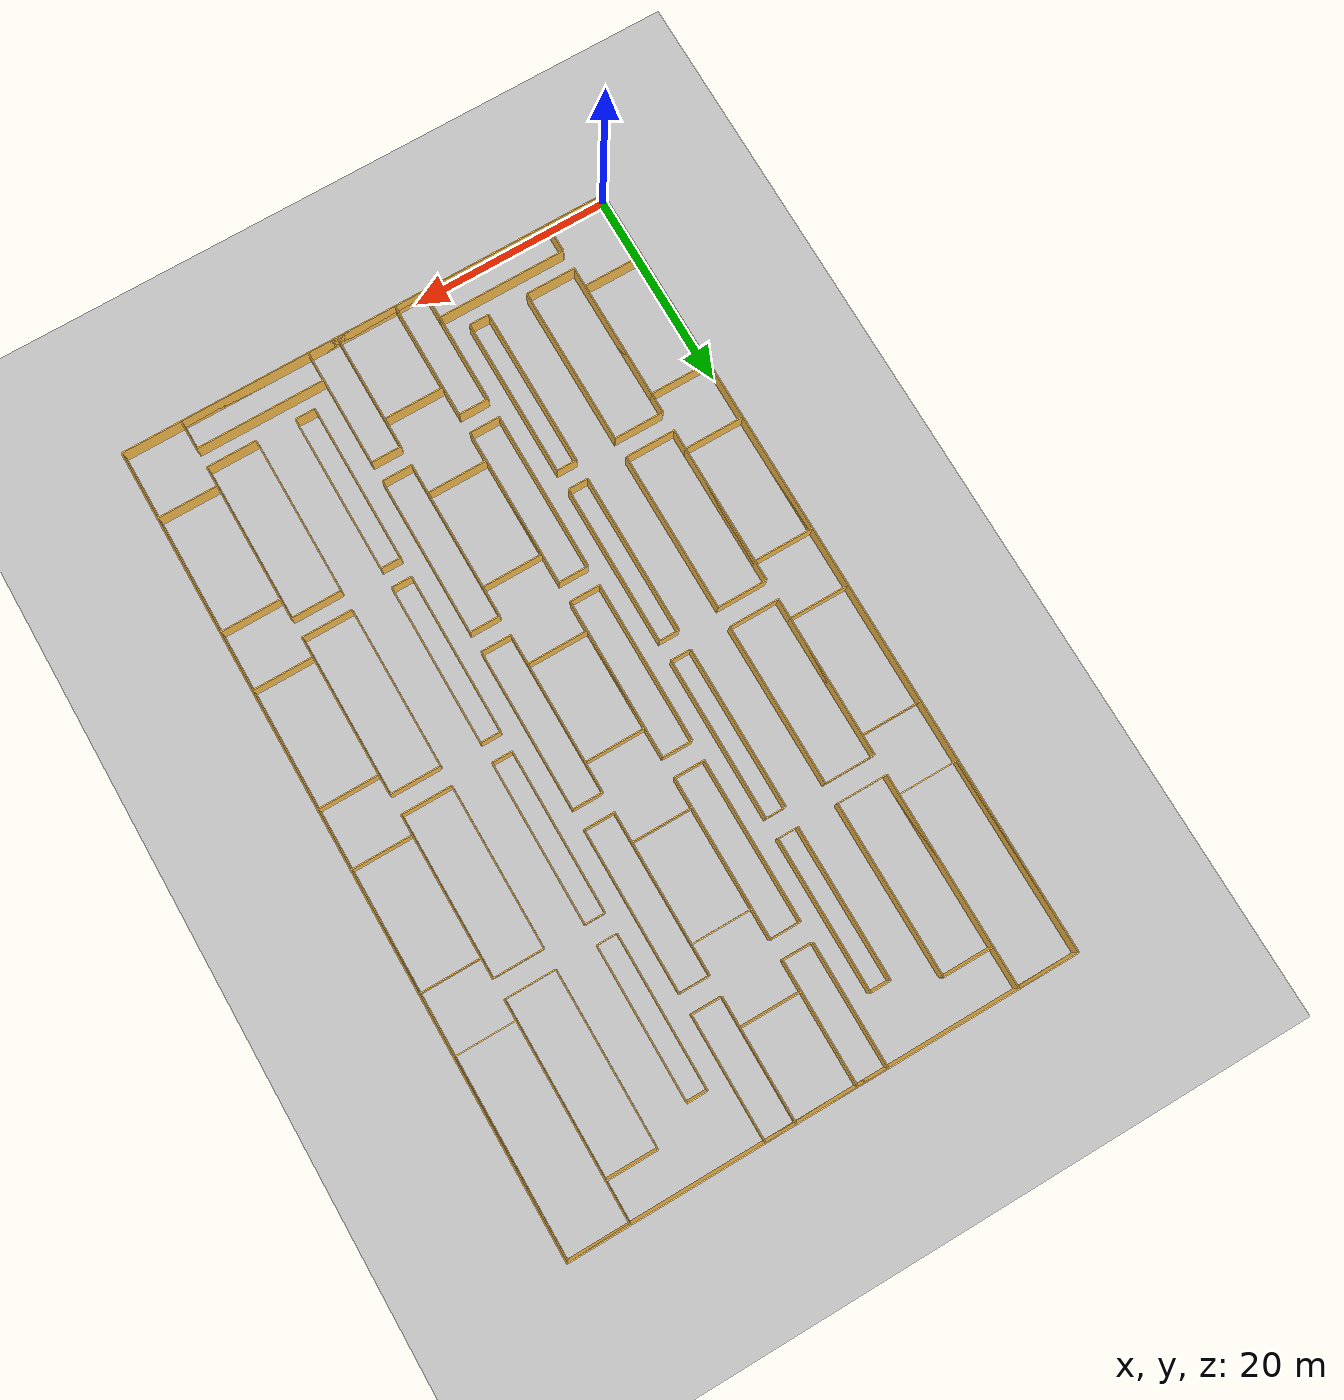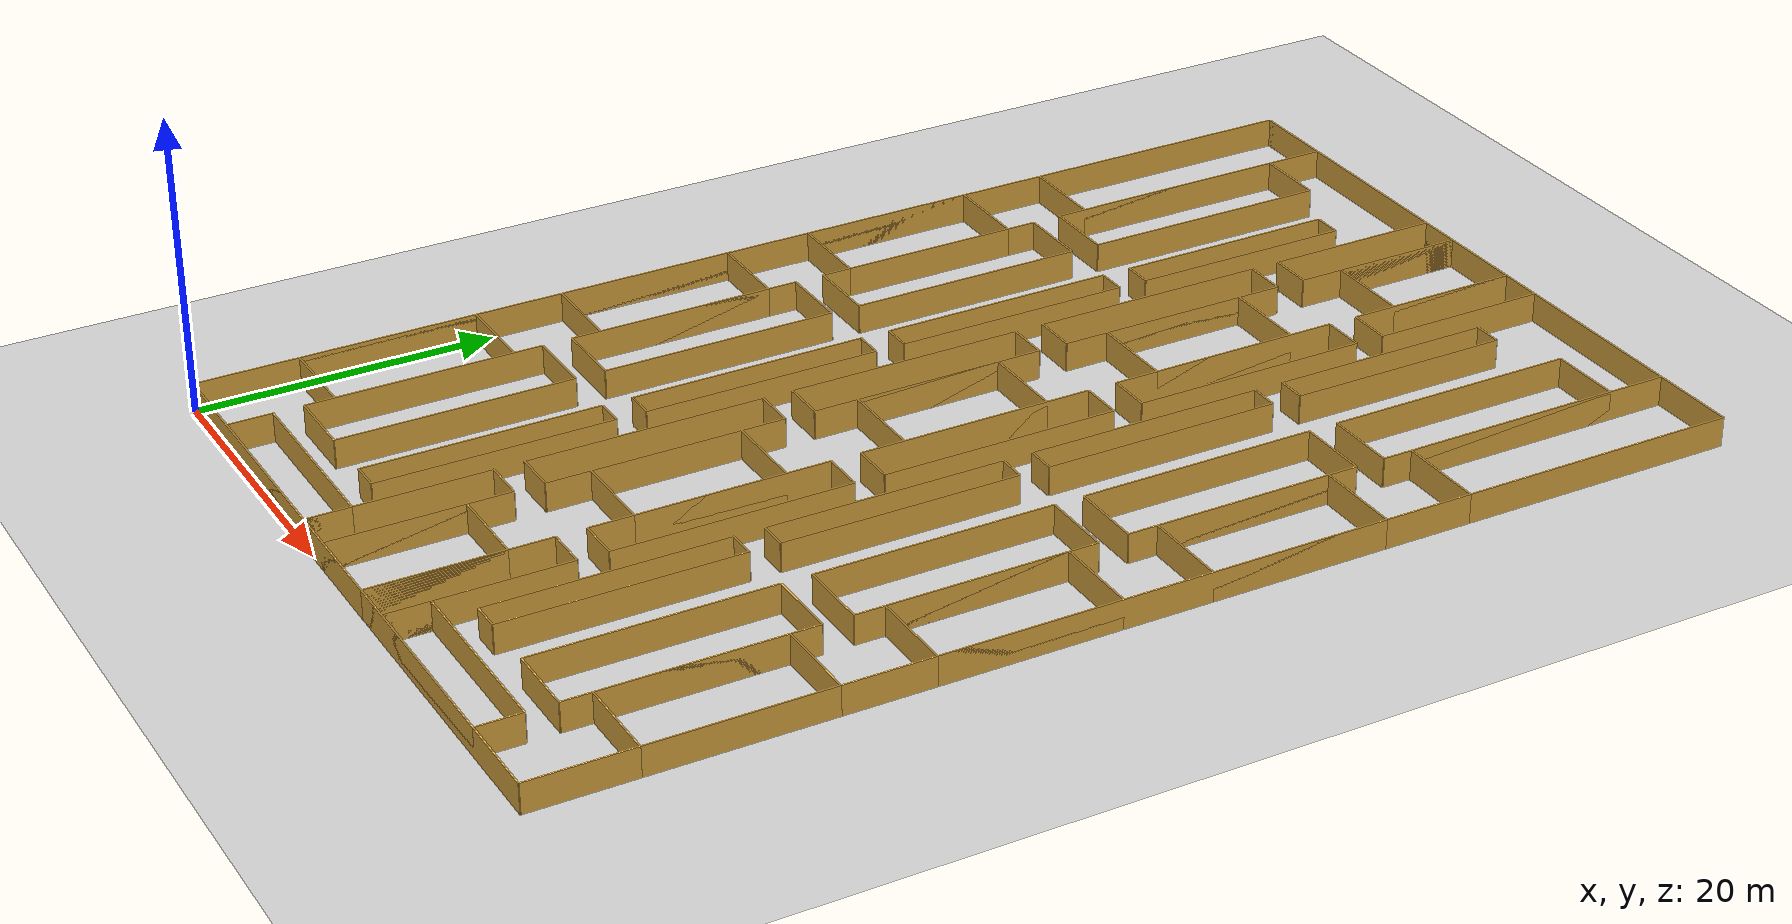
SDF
<sdf version="1.6">
 <world name="default">
  <light name="sun" type="directional">
   <cast_shadows>0</cast_shadows>
   <pose>0 0 10 0 -0 0</pose>
   <diffuse>0.8 0.8 0.8 1</diffuse>
   <specular>0.2 0.2 0.2 1</specular>
   <attenuation>
    <range>1000</range>
    <constant>0.9</constant>
    <linear>0.01</linear>
    <quadratic>0.001</quadratic>
   </attenuation>
   <direction>0.5 0.1 -0.9</direction>
  </light>
  <model name="ground_plane">
   <static>1</static>
   <link name="link">
    <collision name="collision">
     <geometry><plane><normal>0 0 1</normal><size>100 100</size></plane></geometry>
     <surface><friction><ode><mu>100</mu><mu2>50</mu2></ode></friction></surface>
    </collision>
    <visual name="visual">
     <cast_shadows>0</cast_shadows>
     <geometry><plane><normal>0 0 1</normal><size>100 100</size></plane></geometry>
     <material>
      <script><uri>file://media/materials/scripts/gazebo.material</uri><name>Gazebo/Grey</name></script>
     </material>
    </visual>
    <velocity_decay><linear>0</linear><angular>0</angular></velocity_decay>
   </link>
  </model>
  <scene><ambient>0.4 0.4 0.4 1</ambient><background>0.7 0.7 0.7 1</background><shadows>0</shadows></scene>
  <gravity>0 0 -9.8</gravity>
  <physics type="ode">
   <max_step_size>0.001</max_step_size>
   <real_time_factor>1</real_time_factor>
   <real_time_update_rate>500</real_time_update_rate>
  </physics>
  <include><uri>model://schedule_demo_data</uri></include>
 </world>
</sdf>

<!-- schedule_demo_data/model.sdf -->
<sdf version="1.6">
  <model name="schedule_demo_data">
    <static>true</static>
    <link name="wall_0">
      <pose>0.0 70.5 1.0 0 0 1.5707963267948966</pose>
      <self_collide>0</self_collide>
      <kinematic>0</kinematic>
      <visual name="wall_0_visual">
        <geometry>
          <box>
            <size>19.0 0.1 2.0</size>
            </box>
          </geometry>
        <material>
          <script>
            <uri>file://media/materials/scripts/gazebo.material</uri>
            <name>Gazebo/Grey</name>
            </script>
          <ambient>1 0.764706 0.305882 1</ambient>
          <diffuse>0.7 0.7 0.7 1</diffuse>
          <specular>0.01 0.01 0.01 1</specular>
          <emissive>0 0 0 1</emissive>
          <shader type="pixel" />
          </material>
        <cast_shadows>1</cast_shadows>
        <transparency>0</transparency>
        </visual>
      <collision name="wall_0_collision">
        <geometry>
          <box>
            <size>19.0 0.1 2.0</size>
            </box>
          </geometry>
        <laser_retro>0</laser_retro>
        <max_contacts>10</max_contacts>
        <surface>
          <friction>
            <ode>
              <mu>1</mu>
              <mu2>1</mu2>
              <fdir1>0 0 0</fdir1>
              <slip1>0</slip1>
              <slip2>0</slip2>
              </ode>
            </friction>
          <bounce>
            <restitution_coefficient>0</restitution_coefficient>
            <threshold>1000000</threshold>
            </bounce>
          <contact>
            <collide_without_contact>0</collide_without_contact>
            <collide_without_contact_bitmask>1</collide_without_contact_bitmask>
            <collide_bitmask>1</collide_bitmask>
            <ode>
              <soft_cfm>0</soft_cfm>
              <soft_erp>0.2</soft_erp>
              <kp>10000000000000.0</kp>
              <kd>1</kd>
              <max_vel>0.01</max_vel>
              <min_depth>0</min_depth>
              </ode>
            <bullet>
              <split_impulse>1</split_impulse>
              <split_impulse_penetration_threshold>-0.01</split_impulse_penetration_threshold>
              <soft_cfm>0</soft_cfm>
              <soft_erp>0.2</soft_erp>
              <kp>10000000000000.0</kp>
              <kd>1</kd>
              </bullet>
            </contact>
          </surface>
        </collision>
      </link>
    <link name="wall_1">
      <pose>3.0 80.0 1.0 0 0 0.0</pose>
      <self_collide>0</self_collide>
      <kinematic>0</kinematic>
      <visual name="wall_1_visual">
        <geometry>
          <box>
            <size>6.0 0.1 2.0</size>
            </box>
          </geometry>
        <material>
          <script>
            <uri>file://media/materials/scripts/gazebo.material</uri>
            <name>Gazebo/Grey</name>
            </script>
          <ambient>1 0.764706 0.305882 1</ambient>
          <diffuse>0.7 0.7 0.7 1</diffuse>
          <specular>0.01 0.01 0.01 1</specular>
          <emissive>0 0 0 1</emissive>
          <shader type="pixel" />
          </material>
        <cast_shadows>1</cast_shadows>
        <transparency>0</transparency>
        </visual>
      <collision name="wall_1_collision">
        <geometry>
          <box>
            <size>6.0 0.1 2.0</size>
            </box>
          </geometry>
        <laser_retro>0</laser_retro>
        <max_contacts>10</max_contacts>
        <surface>
          <friction>
            <ode>
              <mu>1</mu>
              <mu2>1</mu2>
              <fdir1>0 0 0</fdir1>
              <slip1>0</slip1>
              <slip2>0</slip2>
              </ode>
            </friction>
          <bounce>
            <restitution_coefficient>0</restitution_coefficient>
            <threshold>1000000</threshold>
            </bounce>
          <contact>
            <collide_without_contact>0</collide_without_contact>
            <collide_without_contact_bitmask>1</collide_without_contact_bitmask>
            <collide_bitmask>1</collide_bitmask>
            <ode>
              <soft_cfm>0</soft_cfm>
              <soft_erp>0.2</soft_erp>
              <kp>10000000000000.0</kp>
              <kd>1</kd>
              <max_vel>0.01</max_vel>
              <min_depth>0</min_depth>
              </ode>
            <bullet>
              <split_impulse>1</split_impulse>
              <split_impulse_penetration_threshold>-0.01</split_impulse_penetration_threshold>
              <soft_cfm>0</soft_cfm>
              <soft_erp>0.2</soft_erp>
              <kp>10000000000000.0</kp>
              <kd>1</kd>
              </bullet>
            </contact>
          </surface>
        </collision>
      </link>
    <link name="wall_2">
      <pose>6.0 70.5 1.0 0 0 -1.5707963267948966</pose>
      <self_collide>0</self_collide>
      <kinematic>0</kinematic>
      <visual name="wall_2_visual">
        <geometry>
          <box>
            <size>19.0 0.1 2.0</size>
            </box>
          </geometry>
        <material>
          <script>
            <uri>file://media/materials/scripts/gazebo.material</uri>
            <name>Gazebo/Grey</name>
            </script>
          <ambient>1 0.764706 0.305882 1</ambient>
          <diffuse>0.7 0.7 0.7 1</diffuse>
          <specular>0.01 0.01 0.01 1</specular>
          <emissive>0 0 0 1</emissive>
          <shader type="pixel" />
          </material>
        <cast_shadows>1</cast_shadows>
        <transparency>0</transparency>
        </visual>
      <collision name="wall_2_collision">
        <geometry>
          <box>
            <size>19.0 0.1 2.0</size>
            </box>
          </geometry>
        <laser_retro>0</laser_retro>
        <max_contacts>10</max_contacts>
        <surface>
          <friction>
            <ode>
              <mu>1</mu>
              <mu2>1</mu2>
              <fdir1>0 0 0</fdir1>
              <slip1>0</slip1>
              <slip2>0</slip2>
              </ode>
            </friction>
          <bounce>
            <restitution_coefficient>0</restitution_coefficient>
            <threshold>1000000</threshold>
            </bounce>
          <contact>
            <collide_without_contact>0</collide_without_contact>
            <collide_without_contact_bitmask>1</collide_without_contact_bitmask>
            <collide_bitmask>1</collide_bitmask>
            <ode>
              <soft_cfm>0</soft_cfm>
              <soft_erp>0.2</soft_erp>
              <kp>10000000000000.0</kp>
              <kd>1</kd>
              <max_vel>0.01</max_vel>
              <min_depth>0</min_depth>
              </ode>
            <bullet>
              <split_impulse>1</split_impulse>
              <split_impulse_penetration_threshold>-0.01</split_impulse_penetration_threshold>
              <soft_cfm>0</soft_cfm>
              <soft_erp>0.2</soft_erp>
              <kp>10000000000000.0</kp>
              <kd>1</kd>
              </bullet>
            </contact>
          </surface>
        </collision>
      </link>
    <link name="wall_3">
      <pose>3.0 61.0 1.0 0 0 3.141592653589793</pose>
      <self_collide>0</self_collide>
      <kinematic>0</kinematic>
      <visual name="wall_3_visual">
        <geometry>
          <box>
            <size>6.0 0.1 2.0</size>
            </box>
          </geometry>
        <material>
          <script>
            <uri>file://media/materials/scripts/gazebo.material</uri>
            <name>Gazebo/Grey</name>
            </script>
          <ambient>1 0.764706 0.305882 1</ambient>
          <diffuse>0.7 0.7 0.7 1</diffuse>
          <specular>0.01 0.01 0.01 1</specular>
          <emissive>0 0 0 1</emissive>
          <shader type="pixel" />
          </material>
        <cast_shadows>1</cast_shadows>
        <transparency>0</transparency>
        </visual>
      <collision name="wall_3_collision">
        <geometry>
          <box>
            <size>6.0 0.1 2.0</size>
            </box>
          </geometry>
        <laser_retro>0</laser_retro>
        <max_contacts>10</max_contacts>
        <surface>
          <friction>
            <ode>
              <mu>1</mu>
              <mu2>1</mu2>
              <fdir1>0 0 0</fdir1>
              <slip1>0</slip1>
              <slip2>0</slip2>
              </ode>
            </friction>
          <bounce>
            <restitution_coefficient>0</restitution_coefficient>
            <threshold>1000000</threshold>
            </bounce>
          <contact>
            <collide_without_contact>0</collide_without_contact>
            <collide_without_contact_bitmask>1</collide_without_contact_bitmask>
            <collide_bitmask>1</collide_bitmask>
            <ode>
              <soft_cfm>0</soft_cfm>
              <soft_erp>0.2</soft_erp>
              <kp>10000000000000.0</kp>
              <kd>1</kd>
              <max_vel>0.01</max_vel>
              <min_depth>0</min_depth>
              </ode>
            <bullet>
              <split_impulse>1</split_impulse>
              <split_impulse_penetration_threshold>-0.01</split_impulse_penetration_threshold>
              <soft_cfm>0</soft_cfm>
              <soft_erp>0.2</soft_erp>
              <kp>10000000000000.0</kp>
              <kd>1</kd>
              </bullet>
            </contact>
          </surface>
        </collision>
      </link>
    <link name="wall_4">
      <pose>50.0 70.5 1.0 0 0 1.5707963267948966</pose>
      <self_collide>0</self_collide>
      <kinematic>0</kinematic>
      <visual name="wall_4_visual">
        <geometry>
          <box>
            <size>19.0 0.1 2.0</size>
            </box>
          </geometry>
        <material>
          <script>
            <uri>file://media/materials/scripts/gazebo.material</uri>
            <name>Gazebo/Grey</name>
            </script>
          <ambient>1 0.764706 0.305882 1</ambient>
          <diffuse>0.7 0.7 0.7 1</diffuse>
          <specular>0.01 0.01 0.01 1</specular>
          <emissive>0 0 0 1</emissive>
          <shader type="pixel" />
          </material>
        <cast_shadows>1</cast_shadows>
        <transparency>0</transparency>
        </visual>
      <collision name="wall_4_collision">
        <geometry>
          <box>
            <size>19.0 0.1 2.0</size>
            </box>
          </geometry>
        <laser_retro>0</laser_retro>
        <max_contacts>10</max_contacts>
        <surface>
          <friction>
            <ode>
              <mu>1</mu>
              <mu2>1</mu2>
              <fdir1>0 0 0</fdir1>
              <slip1>0</slip1>
              <slip2>0</slip2>
              </ode>
            </friction>
          <bounce>
            <restitution_coefficient>0</restitution_coefficient>
            <threshold>1000000</threshold>
            </bounce>
          <contact>
            <collide_without_contact>0</collide_without_contact>
            <collide_without_contact_bitmask>1</collide_without_contact_bitmask>
            <collide_bitmask>1</collide_bitmask>
            <ode>
              <soft_cfm>0</soft_cfm>
              <soft_erp>0.2</soft_erp>
              <kp>10000000000000.0</kp>
              <kd>1</kd>
              <max_vel>0.01</max_vel>
              <min_depth>0</min_depth>
              </ode>
            <bullet>
              <split_impulse>1</split_impulse>
              <split_impulse_penetration_threshold>-0.01</split_impulse_penetration_threshold>
              <soft_cfm>0</soft_cfm>
              <soft_erp>0.2</soft_erp>
              <kp>10000000000000.0</kp>
              <kd>1</kd>
              </bullet>
            </contact>
          </surface>
        </collision>
      </link>
    <link name="wall_5">
      <pose>47.0 80.0 1.0 0 0 3.141592653589793</pose>
      <self_collide>0</self_collide>
      <kinematic>0</kinematic>
      <visual name="wall_5_visual">
        <geometry>
          <box>
            <size>6.0 0.1 2.0</size>
            </box>
          </geometry>
        <material>
          <script>
            <uri>file://media/materials/scripts/gazebo.material</uri>
            <name>Gazebo/Grey</name>
            </script>
          <ambient>1 0.764706 0.305882 1</ambient>
          <diffuse>0.7 0.7 0.7 1</diffuse>
          <specular>0.01 0.01 0.01 1</specular>
          <emissive>0 0 0 1</emissive>
          <shader type="pixel" />
          </material>
        <cast_shadows>1</cast_shadows>
        <transparency>0</transparency>
        </visual>
      <collision name="wall_5_collision">
        <geometry>
          <box>
            <size>6.0 0.1 2.0</size>
            </box>
          </geometry>
        <laser_retro>0</laser_retro>
        <max_contacts>10</max_contacts>
        <surface>
          <friction>
            <ode>
              <mu>1</mu>
              <mu2>1</mu2>
              <fdir1>0 0 0</fdir1>
              <slip1>0</slip1>
              <slip2>0</slip2>
              </ode>
            </friction>
          <bounce>
            <restitution_coefficient>0</restitution_coefficient>
            <threshold>1000000</threshold>
            </bounce>
          <contact>
            <collide_without_contact>0</collide_without_contact>
            <collide_without_contact_bitmask>1</collide_without_contact_bitmask>
            <collide_bitmask>1</collide_bitmask>
            <ode>
              <soft_cfm>0</soft_cfm>
              <soft_erp>0.2</soft_erp>
              <kp>10000000000000.0</kp>
              <kd>1</kd>
              <max_vel>0.01</max_vel>
              <min_depth>0</min_depth>
              </ode>
            <bullet>
              <split_impulse>1</split_impulse>
              <split_impulse_penetration_threshold>-0.01</split_impulse_penetration_threshold>
              <soft_cfm>0</soft_cfm>
              <soft_erp>0.2</soft_erp>
              <kp>10000000000000.0</kp>
              <kd>1</kd>
              </bullet>
            </contact>
          </surface>
        </collision>
      </link>
    <link name="wall_6">
      <pose>44.0 70.5 1.0 0 0 -1.5707963267948966</pose>
      <self_collide>0</self_collide>
      <kinematic>0</kinematic>
      <visual name="wall_6_visual">
        <geometry>
          <box>
            <size>19.0 0.1 2.0</size>
            </box>
          </geometry>
        <material>
          <script>
            <uri>file://media/materials/scripts/gazebo.material</uri>
            <name>Gazebo/Grey</name>
            </script>
          <ambient>1 0.764706 0.305882 1</ambient>
          <diffuse>0.7 0.7 0.7 1</diffuse>
          <specular>0.01 0.01 0.01 1</specular>
          <emissive>0 0 0 1</emissive>
          <shader type="pixel" />
          </material>
        <cast_shadows>1</cast_shadows>
        <transparency>0</transparency>
        </visual>
      <collision name="wall_6_collision">
        <geometry>
          <box>
            <size>19.0 0.1 2.0</size>
            </box>
          </geometry>
        <laser_retro>0</laser_retro>
        <max_contacts>10</max_contacts>
        <surface>
          <friction>
            <ode>
              <mu>1</mu>
              <mu2>1</mu2>
              <fdir1>0 0 0</fdir1>
              <slip1>0</slip1>
              <slip2>0</slip2>
              </ode>
            </friction>
          <bounce>
            <restitution_coefficient>0</restitution_coefficient>
            <threshold>1000000</threshold>
            </bounce>
          <contact>
            <collide_without_contact>0</collide_without_contact>
            <collide_without_contact_bitmask>1</collide_without_contact_bitmask>
            <collide_bitmask>1</collide_bitmask>
            <ode>
              <soft_cfm>0</soft_cfm>
              <soft_erp>0.2</soft_erp>
              <kp>10000000000000.0</kp>
              <kd>1</kd>
              <max_vel>0.01</max_vel>
              <min_depth>0</min_depth>
              </ode>
            <bullet>
              <split_impulse>1</split_impulse>
              <split_impulse_penetration_threshold>-0.01</split_impulse_penetration_threshold>
              <soft_cfm>0</soft_cfm>
              <soft_erp>0.2</soft_erp>
              <kp>10000000000000.0</kp>
              <kd>1</kd>
              </bullet>
            </contact>
          </surface>
        </collision>
      </link>
    <link name="wall_7">
      <pose>47.0 61.0 1.0 0 0 0.0</pose>
      <self_collide>0</self_collide>
      <kinematic>0</kinematic>
      <visual name="wall_7_visual">
        <geometry>
          <box>
            <size>6.0 0.1 2.0</size>
            </box>
          </geometry>
        <material>
          <script>
            <uri>file://media/materials/scripts/gazebo.material</uri>
            <name>Gazebo/Grey</name>
            </script>
          <ambient>1 0.764706 0.305882 1</ambient>
          <diffuse>0.7 0.7 0.7 1</diffuse>
          <specular>0.01 0.01 0.01 1</specular>
          <emissive>0 0 0 1</emissive>
          <shader type="pixel" />
          </material>
        <cast_shadows>1</cast_shadows>
        <transparency>0</transparency>
        </visual>
      <collision name="wall_7_collision">
        <geometry>
          <box>
            <size>6.0 0.1 2.0</size>
            </box>
          </geometry>
        <laser_retro>0</laser_retro>
        <max_contacts>10</max_contacts>
        <surface>
          <friction>
            <ode>
              <mu>1</mu>
              <mu2>1</mu2>
              <fdir1>0 0 0</fdir1>
              <slip1>0</slip1>
              <slip2>0</slip2>
              </ode>
            </friction>
          <bounce>
            <restitution_coefficient>0</restitution_coefficient>
            <threshold>1000000</threshold>
            </bounce>
          <contact>
            <collide_without_contact>0</collide_without_contact>
            <collide_without_contact_bitmask>1</collide_without_contact_bitmask>
            <collide_bitmask>1</collide_bitmask>
            <ode>
              <soft_cfm>0</soft_cfm>
              <soft_erp>0.2</soft_erp>
              <kp>10000000000000.0</kp>
              <kd>1</kd>
              <max_vel>0.01</max_vel>
              <min_depth>0</min_depth>
              </ode>
            <bullet>
              <split_impulse>1</split_impulse>
              <split_impulse_penetration_threshold>-0.01</split_impulse_penetration_threshold>
              <soft_cfm>0</soft_cfm>
              <soft_erp>0.2</soft_erp>
              <kp>10000000000000.0</kp>
              <kd>1</kd>
              </bullet>
            </contact>
          </surface>
        </collision>
      </link>
    <link name="wall_8">
      <pose>22.0 22.0 1.0 0 0 1.5707963267948966</pose>
      <self_collide>0</self_collide>
      <kinematic>0</kinematic>
      <visual name="wall_8_visual">
        <geometry>
          <box>
            <size>10.0 0.1 2.0</size>
            </box>
          </geometry>
        <material>
          <script>
            <uri>file://media/materials/scripts/gazebo.material</uri>
            <name>Gazebo/Grey</name>
            </script>
          <ambient>1 0.764706 0.305882 1</ambient>
          <diffuse>0.7 0.7 0.7 1</diffuse>
          <specular>0.01 0.01 0.01 1</specular>
          <emissive>0 0 0 1</emissive>
          <shader type="pixel" />
          </material>
        <cast_shadows>1</cast_shadows>
        <transparency>0</transparency>
        </visual>
      <collision name="wall_8_collision">
        <geometry>
          <box>
            <size>10.0 0.1 2.0</size>
            </box>
          </geometry>
        <laser_retro>0</laser_retro>
        <max_contacts>10</max_contacts>
        <surface>
          <friction>
            <ode>
              <mu>1</mu>
              <mu2>1</mu2>
              <fdir1>0 0 0</fdir1>
              <slip1>0</slip1>
              <slip2>0</slip2>
              </ode>
            </friction>
          <bounce>
            <restitution_coefficient>0</restitution_coefficient>
            <threshold>1000000</threshold>
            </bounce>
          <contact>
            <collide_without_contact>0</collide_without_contact>
            <collide_without_contact_bitmask>1</collide_without_contact_bitmask>
            <collide_bitmask>1</collide_bitmask>
            <ode>
              <soft_cfm>0</soft_cfm>
              <soft_erp>0.2</soft_erp>
              <kp>10000000000000.0</kp>
              <kd>1</kd>
              <max_vel>0.01</max_vel>
              <min_depth>0</min_depth>
              </ode>
            <bullet>
              <split_impulse>1</split_impulse>
              <split_impulse_penetration_threshold>-0.01</split_impulse_penetration_threshold>
              <soft_cfm>0</soft_cfm>
              <soft_erp>0.2</soft_erp>
              <kp>10000000000000.0</kp>
              <kd>1</kd>
              </bullet>
            </contact>
          </surface>
        </collision>
      </link>
    <link name="wall_9">
      <pose>25.0 27.0 1.0 0 0 0.0</pose>
      <self_collide>0</self_collide>
      <kinematic>0</kinematic>
      <visual name="wall_9_visual">
        <geometry>
          <box>
            <size>6.0 0.1 2.0</size>
            </box>
          </geometry>
        <material>
          <script>
            <uri>file://media/materials/scripts/gazebo.material</uri>
            <name>Gazebo/Grey</name>
            </script>
          <ambient>1 0.764706 0.305882 1</ambient>
          <diffuse>0.7 0.7 0.7 1</diffuse>
          <specular>0.01 0.01 0.01 1</specular>
          <emissive>0 0 0 1</emissive>
          <shader type="pixel" />
          </material>
        <cast_shadows>1</cast_shadows>
        <transparency>0</transparency>
        </visual>
      <collision name="wall_9_collision">
        <geometry>
          <box>
            <size>6.0 0.1 2.0</size>
            </box>
          </geometry>
        <laser_retro>0</laser_retro>
        <max_contacts>10</max_contacts>
        <surface>
          <friction>
            <ode>
              <mu>1</mu>
              <mu2>1</mu2>
              <fdir1>0 0 0</fdir1>
              <slip1>0</slip1>
              <slip2>0</slip2>
              </ode>
            </friction>
          <bounce>
            <restitution_coefficient>0</restitution_coefficient>
            <threshold>1000000</threshold>
            </bounce>
          <contact>
            <collide_without_contact>0</collide_without_contact>
            <collide_without_contact_bitmask>1</collide_without_contact_bitmask>
            <collide_bitmask>1</collide_bitmask>
            <ode>
              <soft_cfm>0</soft_cfm>
              <soft_erp>0.2</soft_erp>
              <kp>10000000000000.0</kp>
              <kd>1</kd>
              <max_vel>0.01</max_vel>
              <min_depth>0</min_depth>
              </ode>
            <bullet>
              <split_impulse>1</split_impulse>
              <split_impulse_penetration_threshold>-0.01</split_impulse_penetration_threshold>
              <soft_cfm>0</soft_cfm>
              <soft_erp>0.2</soft_erp>
              <kp>10000000000000.0</kp>
              <kd>1</kd>
              </bullet>
            </contact>
          </surface>
        </collision>
      </link>
    <link name="wall_10">
      <pose>28.0 22.0 1.0 0 0 -1.5707963267948966</pose>
      <self_collide>0</self_collide>
      <kinematic>0</kinematic>
      <visual name="wall_10_visual">
        <geometry>
          <box>
            <size>10.0 0.1 2.0</size>
            </box>
          </geometry>
        <material>
          <script>
            <uri>file://media/materials/scripts/gazebo.material</uri>
            <name>Gazebo/Grey</name>
            </script>
          <ambient>1 0.764706 0.305882 1</ambient>
          <diffuse>0.7 0.7 0.7 1</diffuse>
          <specular>0.01 0.01 0.01 1</specular>
          <emissive>0 0 0 1</emissive>
          <shader type="pixel" />
          </material>
        <cast_shadows>1</cast_shadows>
        <transparency>0</transparency>
        </visual>
      <collision name="wall_10_collision">
        <geometry>
          <box>
            <size>10.0 0.1 2.0</size>
            </box>
          </geometry>
        <laser_retro>0</laser_retro>
        <max_contacts>10</max_contacts>
        <surface>
          <friction>
            <ode>
              <mu>1</mu>
              <mu2>1</mu2>
              <fdir1>0 0 0</fdir1>
              <slip1>0</slip1>
              <slip2>0</slip2>
              </ode>
            </friction>
          <bounce>
            <restitution_coefficient>0</restitution_coefficient>
            <threshold>1000000</threshold>
            </bounce>
          <contact>
            <collide_without_contact>0</collide_without_contact>
            <collide_without_contact_bitmask>1</collide_without_contact_bitmask>
            <collide_bitmask>1</collide_bitmask>
            <ode>
              <soft_cfm>0</soft_cfm>
              <soft_erp>0.2</soft_erp>
              <kp>10000000000000.0</kp>
              <kd>1</kd>
              <max_vel>0.01</max_vel>
              <min_depth>0</min_depth>
              </ode>
            <bullet>
              <split_impulse>1</split_impulse>
              <split_impulse_penetration_threshold>-0.01</split_impulse_penetration_threshold>
              <soft_cfm>0</soft_cfm>
              <soft_erp>0.2</soft_erp>
              <kp>10000000000000.0</kp>
              <kd>1</kd>
              </bullet>
            </contact>
          </surface>
        </collision>
      </link>
    <link name="wall_11">
      <pose>25.0 17.0 1.0 0 0 3.141592653589793</pose>
      <self_collide>0</self_collide>
      <kinematic>0</kinematic>
      <visual name="wall_11_visual">
        <geometry>
          <box>
            <size>6.0 0.1 2.0</size>
            </box>
          </geometry>
        <material>
          <script>
            <uri>file://media/materials/scripts/gazebo.material</uri>
            <name>Gazebo/Grey</name>
            </script>
          <ambient>1 0.764706 0.305882 1</ambient>
          <diffuse>0.7 0.7 0.7 1</diffuse>
          <specular>0.01 0.01 0.01 1</specular>
          <emissive>0 0 0 1</emissive>
          <shader type="pixel" />
          </material>
        <cast_shadows>1</cast_shadows>
        <transparency>0</transparency>
        </visual>
      <collision name="wall_11_collision">
        <geometry>
          <box>
            <size>6.0 0.1 2.0</size>
            </box>
          </geometry>
        <laser_retro>0</laser_retro>
        <max_contacts>10</max_contacts>
        <surface>
          <friction>
            <ode>
              <mu>1</mu>
              <mu2>1</mu2>
              <fdir1>0 0 0</fdir1>
              <slip1>0</slip1>
              <slip2>0</slip2>
              </ode>
            </friction>
          <bounce>
            <restitution_coefficient>0</restitution_coefficient>
            <threshold>1000000</threshold>
            </bounce>
          <contact>
            <collide_without_contact>0</collide_without_contact>
            <collide_without_contact_bitmask>1</collide_without_contact_bitmask>
            <collide_bitmask>1</collide_bitmask>
            <ode>
              <soft_cfm>0</soft_cfm>
              <soft_erp>0.2</soft_erp>
              <kp>10000000000000.0</kp>
              <kd>1</kd>
              <max_vel>0.01</max_vel>
              <min_depth>0</min_depth>
              </ode>
            <bullet>
              <split_impulse>1</split_impulse>
              <split_impulse_penetration_threshold>-0.01</split_impulse_penetration_threshold>
              <soft_cfm>0</soft_cfm>
              <soft_erp>0.2</soft_erp>
              <kp>10000000000000.0</kp>
              <kd>1</kd>
              </bullet>
            </contact>
          </surface>
        </collision>
      </link>
    <link name="wall_12">
      <pose>22.0 40.0 1.0 0 0 1.5707963267948966</pose>
      <self_collide>0</self_collide>
      <kinematic>0</kinematic>
      <visual name="wall_12_visual">
        <geometry>
          <box>
            <size>10.0 0.1 2.0</size>
            </box>
          </geometry>
        <material>
          <script>
            <uri>file://media/materials/scripts/gazebo.material</uri>
            <name>Gazebo/Grey</name>
            </script>
          <ambient>1 0.764706 0.305882 1</ambient>
          <diffuse>0.7 0.7 0.7 1</diffuse>
          <specular>0.01 0.01 0.01 1</specular>
          <emissive>0 0 0 1</emissive>
          <shader type="pixel" />
          </material>
        <cast_shadows>1</cast_shadows>
        <transparency>0</transparency>
        </visual>
      <collision name="wall_12_collision">
        <geometry>
          <box>
            <size>10.0 0.1 2.0</size>
            </box>
          </geometry>
        <laser_retro>0</laser_retro>
        <max_contacts>10</max_contacts>
        <surface>
          <friction>
            <ode>
              <mu>1</mu>
              <mu2>1</mu2>
              <fdir1>0 0 0</fdir1>
              <slip1>0</slip1>
              <slip2>0</slip2>
              </ode>
            </friction>
          <bounce>
            <restitution_coefficient>0</restitution_coefficient>
            <threshold>1000000</threshold>
            </bounce>
          <contact>
            <collide_without_contact>0</collide_without_contact>
            <collide_without_contact_bitmask>1</collide_without_contact_bitmask>
            <collide_bitmask>1</collide_bitmask>
            <ode>
              <soft_cfm>0</soft_cfm>
              <soft_erp>0.2</soft_erp>
              <kp>10000000000000.0</kp>
              <kd>1</kd>
              <max_vel>0.01</max_vel>
              <min_depth>0</min_depth>
              </ode>
            <bullet>
              <split_impulse>1</split_impulse>
              <split_impulse_penetration_threshold>-0.01</split_impulse_penetration_threshold>
              <soft_cfm>0</soft_cfm>
              <soft_erp>0.2</soft_erp>
              <kp>10000000000000.0</kp>
              <kd>1</kd>
              </bullet>
            </contact>
          </surface>
        </collision>
      </link>
    <link name="wall_13">
      <pose>25.0 45.0 1.0 0 0 0.0</pose>
      <self_collide>0</self_collide>
      <kinematic>0</kinematic>
      <visual name="wall_13_visual">
        <geometry>
          <box>
            <size>6.0 0.1 2.0</size>
            </box>
          </geometry>
        <material>
          <script>
            <uri>file://media/materials/scripts/gazebo.material</uri>
            <name>Gazebo/Grey</name>
            </script>
          <ambient>1 0.764706 0.305882 1</ambient>
          <diffuse>0.7 0.7 0.7 1</diffuse>
          <specular>0.01 0.01 0.01 1</specular>
          <emissive>0 0 0 1</emissive>
          <shader type="pixel" />
          </material>
        <cast_shadows>1</cast_shadows>
        <transparency>0</transparency>
        </visual>
      <collision name="wall_13_collision">
        <geometry>
          <box>
            <size>6.0 0.1 2.0</size>
            </box>
          </geometry>
        <laser_retro>0</laser_retro>
        <max_contacts>10</max_contacts>
        <surface>
          <friction>
            <ode>
              <mu>1</mu>
              <mu2>1</mu2>
              <fdir1>0 0 0</fdir1>
              <slip1>0</slip1>
              <slip2>0</slip2>
              </ode>
            </friction>
          <bounce>
            <restitution_coefficient>0</restitution_coefficient>
            <threshold>1000000</threshold>
            </bounce>
          <contact>
            <collide_without_contact>0</collide_without_contact>
            <collide_without_contact_bitmask>1</collide_without_contact_bitmask>
            <collide_bitmask>1</collide_bitmask>
            <ode>
              <soft_cfm>0</soft_cfm>
              <soft_erp>0.2</soft_erp>
              <kp>10000000000000.0</kp>
              <kd>1</kd>
              <max_vel>0.01</max_vel>
              <min_depth>0</min_depth>
              </ode>
            <bullet>
              <split_impulse>1</split_impulse>
              <split_impulse_penetration_threshold>-0.01</split_impulse_penetration_threshold>
              <soft_cfm>0</soft_cfm>
              <soft_erp>0.2</soft_erp>
              <kp>10000000000000.0</kp>
              <kd>1</kd>
              </bullet>
            </contact>
          </surface>
        </collision>
      </link>
    <link name="wall_14">
      <pose>28.0 40.0 1.0 0 0 -1.5707963267948966</pose>
      <self_collide>0</self_collide>
      <kinematic>0</kinematic>
      <visual name="wall_14_visual">
        <geometry>
          <box>
            <size>10.0 0.1 2.0</size>
            </box>
          </geometry>
        <material>
          <script>
            <uri>file://media/materials/scripts/gazebo.material</uri>
            <name>Gazebo/Grey</name>
            </script>
          <ambient>1 0.764706 0.305882 1</ambient>
          <diffuse>0.7 0.7 0.7 1</diffuse>
          <specular>0.01 0.01 0.01 1</specular>
          <emissive>0 0 0 1</emissive>
          <shader type="pixel" />
          </material>
        <cast_shadows>1</cast_shadows>
        <transparency>0</transparency>
        </visual>
      <collision name="wall_14_collision">
        <geometry>
          <box>
            <size>10.0 0.1 2.0</size>
            </box>
          </geometry>
        <laser_retro>0</laser_retro>
        <max_contacts>10</max_contacts>
        <surface>
          <friction>
            <ode>
              <mu>1</mu>
              <mu2>1</mu2>
              <fdir1>0 0 0</fdir1>
              <slip1>0</slip1>
              <slip2>0</slip2>
              </ode>
            </friction>
          <bounce>
            <restitution_coefficient>0</restitution_coefficient>
            <threshold>1000000</threshold>
            </bounce>
          <contact>
            <collide_without_contact>0</collide_without_contact>
            <collide_without_contact_bitmask>1</collide_without_contact_bitmask>
            <collide_bitmask>1</collide_bitmask>
            <ode>
              <soft_cfm>0</soft_cfm>
              <soft_erp>0.2</soft_erp>
              <kp>10000000000000.0</kp>
              <kd>1</kd>
              <max_vel>0.01</max_vel>
              <min_depth>0</min_depth>
              </ode>
            <bullet>
              <split_impulse>1</split_impulse>
              <split_impulse_penetration_threshold>-0.01</split_impulse_penetration_threshold>
              <soft_cfm>0</soft_cfm>
              <soft_erp>0.2</soft_erp>
              <kp>10000000000000.0</kp>
              <kd>1</kd>
              </bullet>
            </contact>
          </surface>
        </collision>
      </link>
    <link name="wall_15">
      <pose>25.0 35.0 1.0 0 0 3.141592653589793</pose>
      <self_collide>0</self_collide>
      <kinematic>0</kinematic>
      <visual name="wall_15_visual">
        <geometry>
          <box>
            <size>6.0 0.1 2.0</size>
            </box>
          </geometry>
        <material>
          <script>
            <uri>file://media/materials/scripts/gazebo.material</uri>
            <name>Gazebo/Grey</name>
            </script>
          <ambient>1 0.764706 0.305882 1</ambient>
          <diffuse>0.7 0.7 0.7 1</diffuse>
          <specular>0.01 0.01 0.01 1</specular>
          <emissive>0 0 0 1</emissive>
          <shader type="pixel" />
          </material>
        <cast_shadows>1</cast_shadows>
        <transparency>0</transparency>
        </visual>
      <collision name="wall_15_collision">
        <geometry>
          <box>
            <size>6.0 0.1 2.0</size>
            </box>
          </geometry>
        <laser_retro>0</laser_retro>
        <max_contacts>10</max_contacts>
        <surface>
          <friction>
            <ode>
              <mu>1</mu>
              <mu2>1</mu2>
              <fdir1>0 0 0</fdir1>
              <slip1>0</slip1>
              <slip2>0</slip2>
              </ode>
            </friction>
          <bounce>
            <restitution_coefficient>0</restitution_coefficient>
            <threshold>1000000</threshold>
            </bounce>
          <contact>
            <collide_without_contact>0</collide_without_contact>
            <collide_without_contact_bitmask>1</collide_without_contact_bitmask>
            <collide_bitmask>1</collide_bitmask>
            <ode>
              <soft_cfm>0</soft_cfm>
              <soft_erp>0.2</soft_erp>
              <kp>10000000000000.0</kp>
              <kd>1</kd>
              <max_vel>0.01</max_vel>
              <min_depth>0</min_depth>
              </ode>
            <bullet>
              <split_impulse>1</split_impulse>
              <split_impulse_penetration_threshold>-0.01</split_impulse_penetration_threshold>
              <soft_cfm>0</soft_cfm>
              <soft_erp>0.2</soft_erp>
              <kp>10000000000000.0</kp>
              <kd>1</kd>
              </bullet>
            </contact>
          </surface>
        </collision>
      </link>
    <link name="wall_16">
      <pose>22.0 58.0 1.0 0 0 1.5707963267948966</pose>
      <self_collide>0</self_collide>
      <kinematic>0</kinematic>
      <visual name="wall_16_visual">
        <geometry>
          <box>
            <size>10.0 0.1 2.0</size>
            </box>
          </geometry>
        <material>
          <script>
            <uri>file://media/materials/scripts/gazebo.material</uri>
            <name>Gazebo/Grey</name>
            </script>
          <ambient>1 0.764706 0.305882 1</ambient>
          <diffuse>0.7 0.7 0.7 1</diffuse>
          <specular>0.01 0.01 0.01 1</specular>
          <emissive>0 0 0 1</emissive>
          <shader type="pixel" />
          </material>
        <cast_shadows>1</cast_shadows>
        <transparency>0</transparency>
        </visual>
      <collision name="wall_16_collision">
        <geometry>
          <box>
            <size>10.0 0.1 2.0</size>
            </box>
          </geometry>
        <laser_retro>0</laser_retro>
        <max_contacts>10</max_contacts>
        <surface>
          <friction>
            <ode>
              <mu>1</mu>
              <mu2>1</mu2>
              <fdir1>0 0 0</fdir1>
              <slip1>0</slip1>
              <slip2>0</slip2>
              </ode>
            </friction>
          <bounce>
            <restitution_coefficient>0</restitution_coefficient>
            <threshold>1000000</threshold>
            </bounce>
          <contact>
            <collide_without_contact>0</collide_without_contact>
            <collide_without_contact_bitmask>1</collide_without_contact_bitmask>
            <collide_bitmask>1</collide_bitmask>
            <ode>
              <soft_cfm>0</soft_cfm>
              <soft_erp>0.2</soft_erp>
              <kp>10000000000000.0</kp>
              <kd>1</kd>
              <max_vel>0.01</max_vel>
              <min_depth>0</min_depth>
              </ode>
            <bullet>
              <split_impulse>1</split_impulse>
              <split_impulse_penetration_threshold>-0.01</split_impulse_penetration_threshold>
              <soft_cfm>0</soft_cfm>
              <soft_erp>0.2</soft_erp>
              <kp>10000000000000.0</kp>
              <kd>1</kd>
              </bullet>
            </contact>
          </surface>
        </collision>
      </link>
    <link name="wall_17">
      <pose>25.0 63.0 1.0 0 0 0.0</pose>
      <self_collide>0</self_collide>
      <kinematic>0</kinematic>
      <visual name="wall_17_visual">
        <geometry>
          <box>
            <size>6.0 0.1 2.0</size>
            </box>
          </geometry>
        <material>
          <script>
            <uri>file://media/materials/scripts/gazebo.material</uri>
            <name>Gazebo/Grey</name>
            </script>
          <ambient>1 0.764706 0.305882 1</ambient>
          <diffuse>0.7 0.7 0.7 1</diffuse>
          <specular>0.01 0.01 0.01 1</specular>
          <emissive>0 0 0 1</emissive>
          <shader type="pixel" />
          </material>
        <cast_shadows>1</cast_shadows>
        <transparency>0</transparency>
        </visual>
      <collision name="wall_17_collision">
        <geometry>
          <box>
            <size>6.0 0.1 2.0</size>
            </box>
          </geometry>
        <laser_retro>0</laser_retro>
        <max_contacts>10</max_contacts>
        <surface>
          <friction>
            <ode>
              <mu>1</mu>
              <mu2>1</mu2>
              <fdir1>0 0 0</fdir1>
              <slip1>0</slip1>
              <slip2>0</slip2>
              </ode>
            </friction>
          <bounce>
            <restitution_coefficient>0</restitution_coefficient>
            <threshold>1000000</threshold>
            </bounce>
          <contact>
            <collide_without_contact>0</collide_without_contact>
            <collide_without_contact_bitmask>1</collide_without_contact_bitmask>
            <collide_bitmask>1</collide_bitmask>
            <ode>
              <soft_cfm>0</soft_cfm>
              <soft_erp>0.2</soft_erp>
              <kp>10000000000000.0</kp>
              <kd>1</kd>
              <max_vel>0.01</max_vel>
              <min_depth>0</min_depth>
              </ode>
            <bullet>
              <split_impulse>1</split_impulse>
              <split_impulse_penetration_threshold>-0.01</split_impulse_penetration_threshold>
              <soft_cfm>0</soft_cfm>
              <soft_erp>0.2</soft_erp>
              <kp>10000000000000.0</kp>
              <kd>1</kd>
              </bullet>
            </contact>
          </surface>
        </collision>
      </link>
    <link name="wall_18">
      <pose>28.0 58.0 1.0 0 0 -1.5707963267948966</pose>
      <self_collide>0</self_collide>
      <kinematic>0</kinematic>
      <visual name="wall_18_visual">
        <geometry>
          <box>
            <size>10.0 0.1 2.0</size>
            </box>
          </geometry>
        <material>
          <script>
            <uri>file://media/materials/scripts/gazebo.material</uri>
            <name>Gazebo/Grey</name>
            </script>
          <ambient>1 0.764706 0.305882 1</ambient>
          <diffuse>0.7 0.7 0.7 1</diffuse>
          <specular>0.01 0.01 0.01 1</specular>
          <emissive>0 0 0 1</emissive>
          <shader type="pixel" />
          </material>
        <cast_shadows>1</cast_shadows>
        <transparency>0</transparency>
        </visual>
      <collision name="wall_18_collision">
        <geometry>
          <box>
            <size>10.0 0.1 2.0</size>
            </box>
          </geometry>
        <laser_retro>0</laser_retro>
        <max_contacts>10</max_contacts>
        <surface>
          <friction>
            <ode>
              <mu>1</mu>
              <mu2>1</mu2>
              <fdir1>0 0 0</fdir1>
              <slip1>0</slip1>
              <slip2>0</slip2>
              </ode>
            </friction>
          <bounce>
            <restitution_coefficient>0</restitution_coefficient>
            <threshold>1000000</threshold>
            </bounce>
          <contact>
            <collide_without_contact>0</collide_without_contact>
            <collide_without_contact_bitmask>1</collide_without_contact_bitmask>
            <collide_bitmask>1</collide_bitmask>
            <ode>
              <soft_cfm>0</soft_cfm>
              <soft_erp>0.2</soft_erp>
              <kp>10000000000000.0</kp>
              <kd>1</kd>
              <max_vel>0.01</max_vel>
              <min_depth>0</min_depth>
              </ode>
            <bullet>
              <split_impulse>1</split_impulse>
              <split_impulse_penetration_threshold>-0.01</split_impulse_penetration_threshold>
              <soft_cfm>0</soft_cfm>
              <soft_erp>0.2</soft_erp>
              <kp>10000000000000.0</kp>
              <kd>1</kd>
              </bullet>
            </contact>
          </surface>
        </collision>
      </link>
    <link name="wall_19">
      <pose>25.0 53.0 1.0 0 0 3.141592653589793</pose>
      <self_collide>0</self_collide>
      <kinematic>0</kinematic>
      <visual name="wall_19_visual">
        <geometry>
          <box>
            <size>6.0 0.1 2.0</size>
            </box>
          </geometry>
        <material>
          <script>
            <uri>file://media/materials/scripts/gazebo.material</uri>
            <name>Gazebo/Grey</name>
            </script>
          <ambient>1 0.764706 0.305882 1</ambient>
          <diffuse>0.7 0.7 0.7 1</diffuse>
          <specular>0.01 0.01 0.01 1</specular>
          <emissive>0 0 0 1</emissive>
          <shader type="pixel" />
          </material>
        <cast_shadows>1</cast_shadows>
        <transparency>0</transparency>
        </visual>
      <collision name="wall_19_collision">
        <geometry>
          <box>
            <size>6.0 0.1 2.0</size>
            </box>
          </geometry>
        <laser_retro>0</laser_retro>
        <max_contacts>10</max_contacts>
        <surface>
          <friction>
            <ode>
              <mu>1</mu>
              <mu2>1</mu2>
              <fdir1>0 0 0</fdir1>
              <slip1>0</slip1>
              <slip2>0</slip2>
              </ode>
            </friction>
          <bounce>
            <restitution_coefficient>0</restitution_coefficient>
            <threshold>1000000</threshold>
            </bounce>
          <contact>
            <collide_without_contact>0</collide_without_contact>
            <collide_without_contact_bitmask>1</collide_without_contact_bitmask>
            <collide_bitmask>1</collide_bitmask>
            <ode>
              <soft_cfm>0</soft_cfm>
              <soft_erp>0.2</soft_erp>
              <kp>10000000000000.0</kp>
              <kd>1</kd>
              <max_vel>0.01</max_vel>
              <min_depth>0</min_depth>
              </ode>
            <bullet>
              <split_impulse>1</split_impulse>
              <split_impulse_penetration_threshold>-0.01</split_impulse_penetration_threshold>
              <soft_cfm>0</soft_cfm>
              <soft_erp>0.2</soft_erp>
              <kp>10000000000000.0</kp>
              <kd>1</kd>
              </bullet>
            </contact>
          </surface>
        </collision>
      </link>
    <link name="wall_20">
      <pose>22.0 75.5 1.0 0 0 1.5707963267948966</pose>
      <self_collide>0</self_collide>
      <kinematic>0</kinematic>
      <visual name="wall_20_visual">
        <geometry>
          <box>
            <size>9.0 0.1 2.0</size>
            </box>
          </geometry>
        <material>
          <script>
            <uri>file://media/materials/scripts/gazebo.material</uri>
            <name>Gazebo/Grey</name>
            </script>
          <ambient>1 0.764706 0.305882 1</ambient>
          <diffuse>0.7 0.7 0.7 1</diffuse>
          <specular>0.01 0.01 0.01 1</specular>
          <emissive>0 0 0 1</emissive>
          <shader type="pixel" />
          </material>
        <cast_shadows>1</cast_shadows>
        <transparency>0</transparency>
        </visual>
      <collision name="wall_20_collision">
        <geometry>
          <box>
            <size>9.0 0.1 2.0</size>
            </box>
          </geometry>
        <laser_retro>0</laser_retro>
        <max_contacts>10</max_contacts>
        <surface>
          <friction>
            <ode>
              <mu>1</mu>
              <mu2>1</mu2>
              <fdir1>0 0 0</fdir1>
              <slip1>0</slip1>
              <slip2>0</slip2>
              </ode>
            </friction>
          <bounce>
            <restitution_coefficient>0</restitution_coefficient>
            <threshold>1000000</threshold>
            </bounce>
          <contact>
            <collide_without_contact>0</collide_without_contact>
            <collide_without_contact_bitmask>1</collide_without_contact_bitmask>
            <collide_bitmask>1</collide_bitmask>
            <ode>
              <soft_cfm>0</soft_cfm>
              <soft_erp>0.2</soft_erp>
              <kp>10000000000000.0</kp>
              <kd>1</kd>
              <max_vel>0.01</max_vel>
              <min_depth>0</min_depth>
              </ode>
            <bullet>
              <split_impulse>1</split_impulse>
              <split_impulse_penetration_threshold>-0.01</split_impulse_penetration_threshold>
              <soft_cfm>0</soft_cfm>
              <soft_erp>0.2</soft_erp>
              <kp>10000000000000.0</kp>
              <kd>1</kd>
              </bullet>
            </contact>
          </surface>
        </collision>
      </link>
    <link name="wall_21">
      <pose>25.0 80.0 1.0 0 0 0.0</pose>
      <self_collide>0</self_collide>
      <kinematic>0</kinematic>
      <visual name="wall_21_visual">
        <geometry>
          <box>
            <size>6.0 0.1 2.0</size>
            </box>
          </geometry>
        <material>
          <script>
            <uri>file://media/materials/scripts/gazebo.material</uri>
            <name>Gazebo/Grey</name>
            </script>
          <ambient>1 0.764706 0.305882 1</ambient>
          <diffuse>0.7 0.7 0.7 1</diffuse>
          <specular>0.01 0.01 0.01 1</specular>
          <emissive>0 0 0 1</emissive>
          <shader type="pixel" />
          </material>
        <cast_shadows>1</cast_shadows>
        <transparency>0</transparency>
        </visual>
      <collision name="wall_21_collision">
        <geometry>
          <box>
            <size>6.0 0.1 2.0</size>
            </box>
          </geometry>
        <laser_retro>0</laser_retro>
        <max_contacts>10</max_contacts>
        <surface>
          <friction>
            <ode>
              <mu>1</mu>
              <mu2>1</mu2>
              <fdir1>0 0 0</fdir1>
              <slip1>0</slip1>
              <slip2>0</slip2>
              </ode>
            </friction>
          <bounce>
            <restitution_coefficient>0</restitution_coefficient>
            <threshold>1000000</threshold>
            </bounce>
          <contact>
            <collide_without_contact>0</collide_without_contact>
            <collide_without_contact_bitmask>1</collide_without_contact_bitmask>
            <collide_bitmask>1</collide_bitmask>
            <ode>
              <soft_cfm>0</soft_cfm>
              <soft_erp>0.2</soft_erp>
              <kp>10000000000000.0</kp>
              <kd>1</kd>
              <max_vel>0.01</max_vel>
              <min_depth>0</min_depth>
              </ode>
            <bullet>
              <split_impulse>1</split_impulse>
              <split_impulse_penetration_threshold>-0.01</split_impulse_penetration_threshold>
              <soft_cfm>0</soft_cfm>
              <soft_erp>0.2</soft_erp>
              <kp>10000000000000.0</kp>
              <kd>1</kd>
              </bullet>
            </contact>
          </surface>
        </collision>
      </link>
    <link name="wall_22">
      <pose>28.0 75.5 1.0 0 0 -1.5707963267948966</pose>
      <self_collide>0</self_collide>
      <kinematic>0</kinematic>
      <visual name="wall_22_visual">
        <geometry>
          <box>
            <size>9.0 0.1 2.0</size>
            </box>
          </geometry>
        <material>
          <script>
            <uri>file://media/materials/scripts/gazebo.material</uri>
            <name>Gazebo/Grey</name>
            </script>
          <ambient>1 0.764706 0.305882 1</ambient>
          <diffuse>0.7 0.7 0.7 1</diffuse>
          <specular>0.01 0.01 0.01 1</specular>
          <emissive>0 0 0 1</emissive>
          <shader type="pixel" />
          </material>
        <cast_shadows>1</cast_shadows>
        <transparency>0</transparency>
        </visual>
      <collision name="wall_22_collision">
        <geometry>
          <box>
            <size>9.0 0.1 2.0</size>
            </box>
          </geometry>
        <laser_retro>0</laser_retro>
        <max_contacts>10</max_contacts>
        <surface>
          <friction>
            <ode>
              <mu>1</mu>
              <mu2>1</mu2>
              <fdir1>0 0 0</fdir1>
              <slip1>0</slip1>
              <slip2>0</slip2>
              </ode>
            </friction>
          <bounce>
            <restitution_coefficient>0</restitution_coefficient>
            <threshold>1000000</threshold>
            </bounce>
          <contact>
            <collide_without_contact>0</collide_without_contact>
            <collide_without_contact_bitmask>1</collide_without_contact_bitmask>
            <collide_bitmask>1</collide_bitmask>
            <ode>
              <soft_cfm>0</soft_cfm>
              <soft_erp>0.2</soft_erp>
              <kp>10000000000000.0</kp>
              <kd>1</kd>
              <max_vel>0.01</max_vel>
              <min_depth>0</min_depth>
              </ode>
            <bullet>
              <split_impulse>1</split_impulse>
              <split_impulse_penetration_threshold>-0.01</split_impulse_penetration_threshold>
              <soft_cfm>0</soft_cfm>
              <soft_erp>0.2</soft_erp>
              <kp>10000000000000.0</kp>
              <kd>1</kd>
              </bullet>
            </contact>
          </surface>
        </collision>
      </link>
    <link name="wall_23">
      <pose>25.0 71.0 1.0 0 0 3.141592653589793</pose>
      <self_collide>0</self_collide>
      <kinematic>0</kinematic>
      <visual name="wall_23_visual">
        <geometry>
          <box>
            <size>6.0 0.1 2.0</size>
            </box>
          </geometry>
        <material>
          <script>
            <uri>file://media/materials/scripts/gazebo.material</uri>
            <name>Gazebo/Grey</name>
            </script>
          <ambient>1 0.764706 0.305882 1</ambient>
          <diffuse>0.7 0.7 0.7 1</diffuse>
          <specular>0.01 0.01 0.01 1</specular>
          <emissive>0 0 0 1</emissive>
          <shader type="pixel" />
          </material>
        <cast_shadows>1</cast_shadows>
        <transparency>0</transparency>
        </visual>
      <collision name="wall_23_collision">
        <geometry>
          <box>
            <size>6.0 0.1 2.0</size>
            </box>
          </geometry>
        <laser_retro>0</laser_retro>
        <max_contacts>10</max_contacts>
        <surface>
          <friction>
            <ode>
              <mu>1</mu>
              <mu2>1</mu2>
              <fdir1>0 0 0</fdir1>
              <slip1>0</slip1>
              <slip2>0</slip2>
              </ode>
            </friction>
          <bounce>
            <restitution_coefficient>0</restitution_coefficient>
            <threshold>1000000</threshold>
            </bounce>
          <contact>
            <collide_without_contact>0</collide_without_contact>
            <collide_without_contact_bitmask>1</collide_without_contact_bitmask>
            <collide_bitmask>1</collide_bitmask>
            <ode>
              <soft_cfm>0</soft_cfm>
              <soft_erp>0.2</soft_erp>
              <kp>10000000000000.0</kp>
              <kd>1</kd>
              <max_vel>0.01</max_vel>
              <min_depth>0</min_depth>
              </ode>
            <bullet>
              <split_impulse>1</split_impulse>
              <split_impulse_penetration_threshold>-0.01</split_impulse_penetration_threshold>
              <soft_cfm>0</soft_cfm>
              <soft_erp>0.2</soft_erp>
              <kp>10000000000000.0</kp>
              <kd>1</kd>
              </bullet>
            </contact>
          </surface>
        </collision>
      </link>
    <link name="wall_24">
      <pose>22.0 4.5 1.0 0 0 -1.5707963267948966</pose>
      <self_collide>0</self_collide>
      <kinematic>0</kinematic>
      <visual name="wall_24_visual">
        <geometry>
          <box>
            <size>9.0 0.1 2.0</size>
            </box>
          </geometry>
        <material>
          <script>
            <uri>file://media/materials/scripts/gazebo.material</uri>
            <name>Gazebo/Grey</name>
            </script>
          <ambient>1 0.764706 0.305882 1</ambient>
          <diffuse>0.7 0.7 0.7 1</diffuse>
          <specular>0.01 0.01 0.01 1</specular>
          <emissive>0 0 0 1</emissive>
          <shader type="pixel" />
          </material>
        <cast_shadows>1</cast_shadows>
        <transparency>0</transparency>
        </visual>
      <collision name="wall_24_collision">
        <geometry>
          <box>
            <size>9.0 0.1 2.0</size>
            </box>
          </geometry>
        <laser_retro>0</laser_retro>
        <max_contacts>10</max_contacts>
        <surface>
          <friction>
            <ode>
              <mu>1</mu>
              <mu2>1</mu2>
              <fdir1>0 0 0</fdir1>
              <slip1>0</slip1>
              <slip2>0</slip2>
              </ode>
            </friction>
          <bounce>
            <restitution_coefficient>0</restitution_coefficient>
            <threshold>1000000</threshold>
            </bounce>
          <contact>
            <collide_without_contact>0</collide_without_contact>
            <collide_without_contact_bitmask>1</collide_without_contact_bitmask>
            <collide_bitmask>1</collide_bitmask>
            <ode>
              <soft_cfm>0</soft_cfm>
              <soft_erp>0.2</soft_erp>
              <kp>10000000000000.0</kp>
              <kd>1</kd>
              <max_vel>0.01</max_vel>
              <min_depth>0</min_depth>
              </ode>
            <bullet>
              <split_impulse>1</split_impulse>
              <split_impulse_penetration_threshold>-0.01</split_impulse_penetration_threshold>
              <soft_cfm>0</soft_cfm>
              <soft_erp>0.2</soft_erp>
              <kp>10000000000000.0</kp>
              <kd>1</kd>
              </bullet>
            </contact>
          </surface>
        </collision>
      </link>
    <link name="wall_25">
      <pose>25.0 0.0 1.0 0 0 0.0</pose>
      <self_collide>0</self_collide>
      <kinematic>0</kinematic>
      <visual name="wall_25_visual">
        <geometry>
          <box>
            <size>6.0 0.1 2.0</size>
            </box>
          </geometry>
        <material>
          <script>
            <uri>file://media/materials/scripts/gazebo.material</uri>
            <name>Gazebo/Grey</name>
            </script>
          <ambient>1 0.764706 0.305882 1</ambient>
          <diffuse>0.7 0.7 0.7 1</diffuse>
          <specular>0.01 0.01 0.01 1</specular>
          <emissive>0 0 0 1</emissive>
          <shader type="pixel" />
          </material>
        <cast_shadows>1</cast_shadows>
        <transparency>0</transparency>
        </visual>
      <collision name="wall_25_collision">
        <geometry>
          <box>
            <size>6.0 0.1 2.0</size>
            </box>
          </geometry>
        <laser_retro>0</laser_retro>
        <max_contacts>10</max_contacts>
        <surface>
          <friction>
            <ode>
              <mu>1</mu>
              <mu2>1</mu2>
              <fdir1>0 0 0</fdir1>
              <slip1>0</slip1>
              <slip2>0</slip2>
              </ode>
            </friction>
          <bounce>
            <restitution_coefficient>0</restitution_coefficient>
            <threshold>1000000</threshold>
            </bounce>
          <contact>
            <collide_without_contact>0</collide_without_contact>
            <collide_without_contact_bitmask>1</collide_without_contact_bitmask>
            <collide_bitmask>1</collide_bitmask>
            <ode>
              <soft_cfm>0</soft_cfm>
              <soft_erp>0.2</soft_erp>
              <kp>10000000000000.0</kp>
              <kd>1</kd>
              <max_vel>0.01</max_vel>
              <min_depth>0</min_depth>
              </ode>
            <bullet>
              <split_impulse>1</split_impulse>
              <split_impulse_penetration_threshold>-0.01</split_impulse_penetration_threshold>
              <soft_cfm>0</soft_cfm>
              <soft_erp>0.2</soft_erp>
              <kp>10000000000000.0</kp>
              <kd>1</kd>
              </bullet>
            </contact>
          </surface>
        </collision>
      </link>
    <link name="wall_26">
      <pose>28.0 4.5 1.0 0 0 1.5707963267948966</pose>
      <self_collide>0</self_collide>
      <kinematic>0</kinematic>
      <visual name="wall_26_visual">
        <geometry>
          <box>
            <size>9.0 0.1 2.0</size>
            </box>
          </geometry>
        <material>
          <script>
            <uri>file://media/materials/scripts/gazebo.material</uri>
            <name>Gazebo/Grey</name>
            </script>
          <ambient>1 0.764706 0.305882 1</ambient>
          <diffuse>0.7 0.7 0.7 1</diffuse>
          <specular>0.01 0.01 0.01 1</specular>
          <emissive>0 0 0 1</emissive>
          <shader type="pixel" />
          </material>
        <cast_shadows>1</cast_shadows>
        <transparency>0</transparency>
        </visual>
      <collision name="wall_26_collision">
        <geometry>
          <box>
            <size>9.0 0.1 2.0</size>
            </box>
          </geometry>
        <laser_retro>0</laser_retro>
        <max_contacts>10</max_contacts>
        <surface>
          <friction>
            <ode>
              <mu>1</mu>
              <mu2>1</mu2>
              <fdir1>0 0 0</fdir1>
              <slip1>0</slip1>
              <slip2>0</slip2>
              </ode>
            </friction>
          <bounce>
            <restitution_coefficient>0</restitution_coefficient>
            <threshold>1000000</threshold>
            </bounce>
          <contact>
            <collide_without_contact>0</collide_without_contact>
            <collide_without_contact_bitmask>1</collide_without_contact_bitmask>
            <collide_bitmask>1</collide_bitmask>
            <ode>
              <soft_cfm>0</soft_cfm>
              <soft_erp>0.2</soft_erp>
              <kp>10000000000000.0</kp>
              <kd>1</kd>
              <max_vel>0.01</max_vel>
              <min_depth>0</min_depth>
              </ode>
            <bullet>
              <split_impulse>1</split_impulse>
              <split_impulse_penetration_threshold>-0.01</split_impulse_penetration_threshold>
              <soft_cfm>0</soft_cfm>
              <soft_erp>0.2</soft_erp>
              <kp>10000000000000.0</kp>
              <kd>1</kd>
              </bullet>
            </contact>
          </surface>
        </collision>
      </link>
    <link name="wall_27">
      <pose>25.0 9.0 1.0 0 0 3.141592653589793</pose>
      <self_collide>0</self_collide>
      <kinematic>0</kinematic>
      <visual name="wall_27_visual">
        <geometry>
          <box>
            <size>6.0 0.1 2.0</size>
            </box>
          </geometry>
        <material>
          <script>
            <uri>file://media/materials/scripts/gazebo.material</uri>
            <name>Gazebo/Grey</name>
            </script>
          <ambient>1 0.764706 0.305882 1</ambient>
          <diffuse>0.7 0.7 0.7 1</diffuse>
          <specular>0.01 0.01 0.01 1</specular>
          <emissive>0 0 0 1</emissive>
          <shader type="pixel" />
          </material>
        <cast_shadows>1</cast_shadows>
        <transparency>0</transparency>
        </visual>
      <collision name="wall_27_collision">
        <geometry>
          <box>
            <size>6.0 0.1 2.0</size>
            </box>
          </geometry>
        <laser_retro>0</laser_retro>
        <max_contacts>10</max_contacts>
        <surface>
          <friction>
            <ode>
              <mu>1</mu>
              <mu2>1</mu2>
              <fdir1>0 0 0</fdir1>
              <slip1>0</slip1>
              <slip2>0</slip2>
              </ode>
            </friction>
          <bounce>
            <restitution_coefficient>0</restitution_coefficient>
            <threshold>1000000</threshold>
            </bounce>
          <contact>
            <collide_without_contact>0</collide_without_contact>
            <collide_without_contact_bitmask>1</collide_without_contact_bitmask>
            <collide_bitmask>1</collide_bitmask>
            <ode>
              <soft_cfm>0</soft_cfm>
              <soft_erp>0.2</soft_erp>
              <kp>10000000000000.0</kp>
              <kd>1</kd>
              <max_vel>0.01</max_vel>
              <min_depth>0</min_depth>
              </ode>
            <bullet>
              <split_impulse>1</split_impulse>
              <split_impulse_penetration_threshold>-0.01</split_impulse_penetration_threshold>
              <soft_cfm>0</soft_cfm>
              <soft_erp>0.2</soft_erp>
              <kp>10000000000000.0</kp>
              <kd>1</kd>
              </bullet>
            </contact>
          </surface>
        </collision>
      </link>
    <link name="wall_28">
      <pose>20.5 14.0 1.0 0 0 0.0</pose>
      <self_collide>0</self_collide>
      <kinematic>0</kinematic>
      <visual name="wall_28_visual">
        <geometry>
          <box>
            <size>3.0 0.1 2.0</size>
            </box>
          </geometry>
        <material>
          <script>
            <uri>file://media/materials/scripts/gazebo.material</uri>
            <name>Gazebo/Grey</name>
            </script>
          <ambient>1 0.764706 0.305882 1</ambient>
          <diffuse>0.7 0.7 0.7 1</diffuse>
          <specular>0.01 0.01 0.01 1</specular>
          <emissive>0 0 0 1</emissive>
          <shader type="pixel" />
          </material>
        <cast_shadows>1</cast_shadows>
        <transparency>0</transparency>
        </visual>
      <collision name="wall_28_collision">
        <geometry>
          <box>
            <size>3.0 0.1 2.0</size>
            </box>
          </geometry>
        <laser_retro>0</laser_retro>
        <max_contacts>10</max_contacts>
        <surface>
          <friction>
            <ode>
              <mu>1</mu>
              <mu2>1</mu2>
              <fdir1>0 0 0</fdir1>
              <slip1>0</slip1>
              <slip2>0</slip2>
              </ode>
            </friction>
          <bounce>
            <restitution_coefficient>0</restitution_coefficient>
            <threshold>1000000</threshold>
            </bounce>
          <contact>
            <collide_without_contact>0</collide_without_contact>
            <collide_without_contact_bitmask>1</collide_without_contact_bitmask>
            <collide_bitmask>1</collide_bitmask>
            <ode>
              <soft_cfm>0</soft_cfm>
              <soft_erp>0.2</soft_erp>
              <kp>10000000000000.0</kp>
              <kd>1</kd>
              <max_vel>0.01</max_vel>
              <min_depth>0</min_depth>
              </ode>
            <bullet>
              <split_impulse>1</split_impulse>
              <split_impulse_penetration_threshold>-0.01</split_impulse_penetration_threshold>
              <soft_cfm>0</soft_cfm>
              <soft_erp>0.2</soft_erp>
              <kp>10000000000000.0</kp>
              <kd>1</kd>
              </bullet>
            </contact>
          </surface>
        </collision>
      </link>
    <link name="wall_29">
      <pose>22.0 22.0 1.0 0 0 1.5707963267948966</pose>
      <self_collide>0</self_collide>
      <kinematic>0</kinematic>
      <visual name="wall_29_visual">
        <geometry>
          <box>
            <size>16.0 0.1 2.0</size>
            </box>
          </geometry>
        <material>
          <script>
            <uri>file://media/materials/scripts/gazebo.material</uri>
            <name>Gazebo/Grey</name>
            </script>
          <ambient>1 0.764706 0.305882 1</ambient>
          <diffuse>0.7 0.7 0.7 1</diffuse>
          <specular>0.01 0.01 0.01 1</specular>
          <emissive>0 0 0 1</emissive>
          <shader type="pixel" />
          </material>
        <cast_shadows>1</cast_shadows>
        <transparency>0</transparency>
        </visual>
      <collision name="wall_29_collision">
        <geometry>
          <box>
            <size>16.0 0.1 2.0</size>
            </box>
          </geometry>
        <laser_retro>0</laser_retro>
        <max_contacts>10</max_contacts>
        <surface>
          <friction>
            <ode>
              <mu>1</mu>
              <mu2>1</mu2>
              <fdir1>0 0 0</fdir1>
              <slip1>0</slip1>
              <slip2>0</slip2>
              </ode>
            </friction>
          <bounce>
            <restitution_coefficient>0</restitution_coefficient>
            <threshold>1000000</threshold>
            </bounce>
          <contact>
            <collide_without_contact>0</collide_without_contact>
            <collide_without_contact_bitmask>1</collide_without_contact_bitmask>
            <collide_bitmask>1</collide_bitmask>
            <ode>
              <soft_cfm>0</soft_cfm>
              <soft_erp>0.2</soft_erp>
              <kp>10000000000000.0</kp>
              <kd>1</kd>
              <max_vel>0.01</max_vel>
              <min_depth>0</min_depth>
              </ode>
            <bullet>
              <split_impulse>1</split_impulse>
              <split_impulse_penetration_threshold>-0.01</split_impulse_penetration_threshold>
              <soft_cfm>0</soft_cfm>
              <soft_erp>0.2</soft_erp>
              <kp>10000000000000.0</kp>
              <kd>1</kd>
              </bullet>
            </contact>
          </surface>
        </collision>
      </link>
    <link name="wall_30">
      <pose>20.5 30.0 1.0 0 0 3.141592653589793</pose>
      <self_collide>0</self_collide>
      <kinematic>0</kinematic>
      <visual name="wall_30_visual">
        <geometry>
          <box>
            <size>3.0 0.1 2.0</size>
            </box>
          </geometry>
        <material>
          <script>
            <uri>file://media/materials/scripts/gazebo.material</uri>
            <name>Gazebo/Grey</name>
            </script>
          <ambient>1 0.764706 0.305882 1</ambient>
          <diffuse>0.7 0.7 0.7 1</diffuse>
          <specular>0.01 0.01 0.01 1</specular>
          <emissive>0 0 0 1</emissive>
          <shader type="pixel" />
          </material>
        <cast_shadows>1</cast_shadows>
        <transparency>0</transparency>
        </visual>
      <collision name="wall_30_collision">
        <geometry>
          <box>
            <size>3.0 0.1 2.0</size>
            </box>
          </geometry>
        <laser_retro>0</laser_retro>
        <max_contacts>10</max_contacts>
        <surface>
          <friction>
            <ode>
              <mu>1</mu>
              <mu2>1</mu2>
              <fdir1>0 0 0</fdir1>
              <slip1>0</slip1>
              <slip2>0</slip2>
              </ode>
            </friction>
          <bounce>
            <restitution_coefficient>0</restitution_coefficient>
            <threshold>1000000</threshold>
            </bounce>
          <contact>
            <collide_without_contact>0</collide_without_contact>
            <collide_without_contact_bitmask>1</collide_without_contact_bitmask>
            <collide_bitmask>1</collide_bitmask>
            <ode>
              <soft_cfm>0</soft_cfm>
              <soft_erp>0.2</soft_erp>
              <kp>10000000000000.0</kp>
              <kd>1</kd>
              <max_vel>0.01</max_vel>
              <min_depth>0</min_depth>
              </ode>
            <bullet>
              <split_impulse>1</split_impulse>
              <split_impulse_penetration_threshold>-0.01</split_impulse_penetration_threshold>
              <soft_cfm>0</soft_cfm>
              <soft_erp>0.2</soft_erp>
              <kp>10000000000000.0</kp>
              <kd>1</kd>
              </bullet>
            </contact>
          </surface>
        </collision>
      </link>
    <link name="wall_31">
      <pose>19.0 22.0 1.0 0 0 -1.5707963267948966</pose>
      <self_collide>0</self_collide>
      <kinematic>0</kinematic>
      <visual name="wall_31_visual">
        <geometry>
          <box>
            <size>16.0 0.1 2.0</size>
            </box>
          </geometry>
        <material>
          <script>
            <uri>file://media/materials/scripts/gazebo.material</uri>
            <name>Gazebo/Grey</name>
            </script>
          <ambient>1 0.764706 0.305882 1</ambient>
          <diffuse>0.7 0.7 0.7 1</diffuse>
          <specular>0.01 0.01 0.01 1</specular>
          <emissive>0 0 0 1</emissive>
          <shader type="pixel" />
          </material>
        <cast_shadows>1</cast_shadows>
        <transparency>0</transparency>
        </visual>
      <collision name="wall_31_collision">
        <geometry>
          <box>
            <size>16.0 0.1 2.0</size>
            </box>
          </geometry>
        <laser_retro>0</laser_retro>
        <max_contacts>10</max_contacts>
        <surface>
          <friction>
            <ode>
              <mu>1</mu>
              <mu2>1</mu2>
              <fdir1>0 0 0</fdir1>
              <slip1>0</slip1>
              <slip2>0</slip2>
              </ode>
            </friction>
          <bounce>
            <restitution_coefficient>0</restitution_coefficient>
            <threshold>1000000</threshold>
            </bounce>
          <contact>
            <collide_without_contact>0</collide_without_contact>
            <collide_without_contact_bitmask>1</collide_without_contact_bitmask>
            <collide_bitmask>1</collide_bitmask>
            <ode>
              <soft_cfm>0</soft_cfm>
              <soft_erp>0.2</soft_erp>
              <kp>10000000000000.0</kp>
              <kd>1</kd>
              <max_vel>0.01</max_vel>
              <min_depth>0</min_depth>
              </ode>
            <bullet>
              <split_impulse>1</split_impulse>
              <split_impulse_penetration_threshold>-0.01</split_impulse_penetration_threshold>
              <soft_cfm>0</soft_cfm>
              <soft_erp>0.2</soft_erp>
              <kp>10000000000000.0</kp>
              <kd>1</kd>
              </bullet>
            </contact>
          </surface>
        </collision>
      </link>
    <link name="wall_32">
      <pose>20.5 32.0 1.0 0 0 0.0</pose>
      <self_collide>0</self_collide>
      <kinematic>0</kinematic>
      <visual name="wall_32_visual">
        <geometry>
          <box>
            <size>3.0 0.1 2.0</size>
            </box>
          </geometry>
        <material>
          <script>
            <uri>file://media/materials/scripts/gazebo.material</uri>
            <name>Gazebo/Grey</name>
            </script>
          <ambient>1 0.764706 0.305882 1</ambient>
          <diffuse>0.7 0.7 0.7 1</diffuse>
          <specular>0.01 0.01 0.01 1</specular>
          <emissive>0 0 0 1</emissive>
          <shader type="pixel" />
          </material>
        <cast_shadows>1</cast_shadows>
        <transparency>0</transparency>
        </visual>
      <collision name="wall_32_collision">
        <geometry>
          <box>
            <size>3.0 0.1 2.0</size>
            </box>
          </geometry>
        <laser_retro>0</laser_retro>
        <max_contacts>10</max_contacts>
        <surface>
          <friction>
            <ode>
              <mu>1</mu>
              <mu2>1</mu2>
              <fdir1>0 0 0</fdir1>
              <slip1>0</slip1>
              <slip2>0</slip2>
              </ode>
            </friction>
          <bounce>
            <restitution_coefficient>0</restitution_coefficient>
            <threshold>1000000</threshold>
            </bounce>
          <contact>
            <collide_without_contact>0</collide_without_contact>
            <collide_without_contact_bitmask>1</collide_without_contact_bitmask>
            <collide_bitmask>1</collide_bitmask>
            <ode>
              <soft_cfm>0</soft_cfm>
              <soft_erp>0.2</soft_erp>
              <kp>10000000000000.0</kp>
              <kd>1</kd>
              <max_vel>0.01</max_vel>
              <min_depth>0</min_depth>
              </ode>
            <bullet>
              <split_impulse>1</split_impulse>
              <split_impulse_penetration_threshold>-0.01</split_impulse_penetration_threshold>
              <soft_cfm>0</soft_cfm>
              <soft_erp>0.2</soft_erp>
              <kp>10000000000000.0</kp>
              <kd>1</kd>
              </bullet>
            </contact>
          </surface>
        </collision>
      </link>
    <link name="wall_33">
      <pose>22.0 40.0 1.0 0 0 1.5707963267948966</pose>
      <self_collide>0</self_collide>
      <kinematic>0</kinematic>
      <visual name="wall_33_visual">
        <geometry>
          <box>
            <size>16.0 0.1 2.0</size>
            </box>
          </geometry>
        <material>
          <script>
            <uri>file://media/materials/scripts/gazebo.material</uri>
            <name>Gazebo/Grey</name>
            </script>
          <ambient>1 0.764706 0.305882 1</ambient>
          <diffuse>0.7 0.7 0.7 1</diffuse>
          <specular>0.01 0.01 0.01 1</specular>
          <emissive>0 0 0 1</emissive>
          <shader type="pixel" />
          </material>
        <cast_shadows>1</cast_shadows>
        <transparency>0</transparency>
        </visual>
      <collision name="wall_33_collision">
        <geometry>
          <box>
            <size>16.0 0.1 2.0</size>
            </box>
          </geometry>
        <laser_retro>0</laser_retro>
        <max_contacts>10</max_contacts>
        <surface>
          <friction>
            <ode>
              <mu>1</mu>
              <mu2>1</mu2>
              <fdir1>0 0 0</fdir1>
              <slip1>0</slip1>
              <slip2>0</slip2>
              </ode>
            </friction>
          <bounce>
            <restitution_coefficient>0</restitution_coefficient>
            <threshold>1000000</threshold>
            </bounce>
          <contact>
            <collide_without_contact>0</collide_without_contact>
            <collide_without_contact_bitmask>1</collide_without_contact_bitmask>
            <collide_bitmask>1</collide_bitmask>
            <ode>
              <soft_cfm>0</soft_cfm>
              <soft_erp>0.2</soft_erp>
              <kp>10000000000000.0</kp>
              <kd>1</kd>
              <max_vel>0.01</max_vel>
              <min_depth>0</min_depth>
              </ode>
            <bullet>
              <split_impulse>1</split_impulse>
              <split_impulse_penetration_threshold>-0.01</split_impulse_penetration_threshold>
              <soft_cfm>0</soft_cfm>
              <soft_erp>0.2</soft_erp>
              <kp>10000000000000.0</kp>
              <kd>1</kd>
              </bullet>
            </contact>
          </surface>
        </collision>
      </link>
    <link name="wall_34">
      <pose>20.5 48.0 1.0 0 0 3.141592653589793</pose>
      <self_collide>0</self_collide>
      <kinematic>0</kinematic>
      <visual name="wall_34_visual">
        <geometry>
          <box>
            <size>3.0 0.1 2.0</size>
            </box>
          </geometry>
        <material>
          <script>
            <uri>file://media/materials/scripts/gazebo.material</uri>
            <name>Gazebo/Grey</name>
            </script>
          <ambient>1 0.764706 0.305882 1</ambient>
          <diffuse>0.7 0.7 0.7 1</diffuse>
          <specular>0.01 0.01 0.01 1</specular>
          <emissive>0 0 0 1</emissive>
          <shader type="pixel" />
          </material>
        <cast_shadows>1</cast_shadows>
        <transparency>0</transparency>
        </visual>
      <collision name="wall_34_collision">
        <geometry>
          <box>
            <size>3.0 0.1 2.0</size>
            </box>
          </geometry>
        <laser_retro>0</laser_retro>
        <max_contacts>10</max_contacts>
        <surface>
          <friction>
            <ode>
              <mu>1</mu>
              <mu2>1</mu2>
              <fdir1>0 0 0</fdir1>
              <slip1>0</slip1>
              <slip2>0</slip2>
              </ode>
            </friction>
          <bounce>
            <restitution_coefficient>0</restitution_coefficient>
            <threshold>1000000</threshold>
            </bounce>
          <contact>
            <collide_without_contact>0</collide_without_contact>
            <collide_without_contact_bitmask>1</collide_without_contact_bitmask>
            <collide_bitmask>1</collide_bitmask>
            <ode>
              <soft_cfm>0</soft_cfm>
              <soft_erp>0.2</soft_erp>
              <kp>10000000000000.0</kp>
              <kd>1</kd>
              <max_vel>0.01</max_vel>
              <min_depth>0</min_depth>
              </ode>
            <bullet>
              <split_impulse>1</split_impulse>
              <split_impulse_penetration_threshold>-0.01</split_impulse_penetration_threshold>
              <soft_cfm>0</soft_cfm>
              <soft_erp>0.2</soft_erp>
              <kp>10000000000000.0</kp>
              <kd>1</kd>
              </bullet>
            </contact>
          </surface>
        </collision>
      </link>
    <link name="wall_35">
      <pose>19.0 40.0 1.0 0 0 -1.5707963267948966</pose>
      <self_collide>0</self_collide>
      <kinematic>0</kinematic>
      <visual name="wall_35_visual">
        <geometry>
          <box>
            <size>16.0 0.1 2.0</size>
            </box>
          </geometry>
        <material>
          <script>
            <uri>file://media/materials/scripts/gazebo.material</uri>
            <name>Gazebo/Grey</name>
            </script>
          <ambient>1 0.764706 0.305882 1</ambient>
          <diffuse>0.7 0.7 0.7 1</diffuse>
          <specular>0.01 0.01 0.01 1</specular>
          <emissive>0 0 0 1</emissive>
          <shader type="pixel" />
          </material>
        <cast_shadows>1</cast_shadows>
        <transparency>0</transparency>
        </visual>
      <collision name="wall_35_collision">
        <geometry>
          <box>
            <size>16.0 0.1 2.0</size>
            </box>
          </geometry>
        <laser_retro>0</laser_retro>
        <max_contacts>10</max_contacts>
        <surface>
          <friction>
            <ode>
              <mu>1</mu>
              <mu2>1</mu2>
              <fdir1>0 0 0</fdir1>
              <slip1>0</slip1>
              <slip2>0</slip2>
              </ode>
            </friction>
          <bounce>
            <restitution_coefficient>0</restitution_coefficient>
            <threshold>1000000</threshold>
            </bounce>
          <contact>
            <collide_without_contact>0</collide_without_contact>
            <collide_without_contact_bitmask>1</collide_without_contact_bitmask>
            <collide_bitmask>1</collide_bitmask>
            <ode>
              <soft_cfm>0</soft_cfm>
              <soft_erp>0.2</soft_erp>
              <kp>10000000000000.0</kp>
              <kd>1</kd>
              <max_vel>0.01</max_vel>
              <min_depth>0</min_depth>
              </ode>
            <bullet>
              <split_impulse>1</split_impulse>
              <split_impulse_penetration_threshold>-0.01</split_impulse_penetration_threshold>
              <soft_cfm>0</soft_cfm>
              <soft_erp>0.2</soft_erp>
              <kp>10000000000000.0</kp>
              <kd>1</kd>
              </bullet>
            </contact>
          </surface>
        </collision>
      </link>
    <link name="wall_36">
      <pose>20.5 50.0 1.0 0 0 0.0</pose>
      <self_collide>0</self_collide>
      <kinematic>0</kinematic>
      <visual name="wall_36_visual">
        <geometry>
          <box>
            <size>3.0 0.1 2.0</size>
            </box>
          </geometry>
        <material>
          <script>
            <uri>file://media/materials/scripts/gazebo.material</uri>
            <name>Gazebo/Grey</name>
            </script>
          <ambient>1 0.764706 0.305882 1</ambient>
          <diffuse>0.7 0.7 0.7 1</diffuse>
          <specular>0.01 0.01 0.01 1</specular>
          <emissive>0 0 0 1</emissive>
          <shader type="pixel" />
          </material>
        <cast_shadows>1</cast_shadows>
        <transparency>0</transparency>
        </visual>
      <collision name="wall_36_collision">
        <geometry>
          <box>
            <size>3.0 0.1 2.0</size>
            </box>
          </geometry>
        <laser_retro>0</laser_retro>
        <max_contacts>10</max_contacts>
        <surface>
          <friction>
            <ode>
              <mu>1</mu>
              <mu2>1</mu2>
              <fdir1>0 0 0</fdir1>
              <slip1>0</slip1>
              <slip2>0</slip2>
              </ode>
            </friction>
          <bounce>
            <restitution_coefficient>0</restitution_coefficient>
            <threshold>1000000</threshold>
            </bounce>
          <contact>
            <collide_without_contact>0</collide_without_contact>
            <collide_without_contact_bitmask>1</collide_without_contact_bitmask>
            <collide_bitmask>1</collide_bitmask>
            <ode>
              <soft_cfm>0</soft_cfm>
              <soft_erp>0.2</soft_erp>
              <kp>10000000000000.0</kp>
              <kd>1</kd>
              <max_vel>0.01</max_vel>
              <min_depth>0</min_depth>
              </ode>
            <bullet>
              <split_impulse>1</split_impulse>
              <split_impulse_penetration_threshold>-0.01</split_impulse_penetration_threshold>
              <soft_cfm>0</soft_cfm>
              <soft_erp>0.2</soft_erp>
              <kp>10000000000000.0</kp>
              <kd>1</kd>
              </bullet>
            </contact>
          </surface>
        </collision>
      </link>
    <link name="wall_37">
      <pose>22.0 58.0 1.0 0 0 1.5707963267948966</pose>
      <self_collide>0</self_collide>
      <kinematic>0</kinematic>
      <visual name="wall_37_visual">
        <geometry>
          <box>
            <size>16.0 0.1 2.0</size>
            </box>
          </geometry>
        <material>
          <script>
            <uri>file://media/materials/scripts/gazebo.material</uri>
            <name>Gazebo/Grey</name>
            </script>
          <ambient>1 0.764706 0.305882 1</ambient>
          <diffuse>0.7 0.7 0.7 1</diffuse>
          <specular>0.01 0.01 0.01 1</specular>
          <emissive>0 0 0 1</emissive>
          <shader type="pixel" />
          </material>
        <cast_shadows>1</cast_shadows>
        <transparency>0</transparency>
        </visual>
      <collision name="wall_37_collision">
        <geometry>
          <box>
            <size>16.0 0.1 2.0</size>
            </box>
          </geometry>
        <laser_retro>0</laser_retro>
        <max_contacts>10</max_contacts>
        <surface>
          <friction>
            <ode>
              <mu>1</mu>
              <mu2>1</mu2>
              <fdir1>0 0 0</fdir1>
              <slip1>0</slip1>
              <slip2>0</slip2>
              </ode>
            </friction>
          <bounce>
            <restitution_coefficient>0</restitution_coefficient>
            <threshold>1000000</threshold>
            </bounce>
          <contact>
            <collide_without_contact>0</collide_without_contact>
            <collide_without_contact_bitmask>1</collide_without_contact_bitmask>
            <collide_bitmask>1</collide_bitmask>
            <ode>
              <soft_cfm>0</soft_cfm>
              <soft_erp>0.2</soft_erp>
              <kp>10000000000000.0</kp>
              <kd>1</kd>
              <max_vel>0.01</max_vel>
              <min_depth>0</min_depth>
              </ode>
            <bullet>
              <split_impulse>1</split_impulse>
              <split_impulse_penetration_threshold>-0.01</split_impulse_penetration_threshold>
              <soft_cfm>0</soft_cfm>
              <soft_erp>0.2</soft_erp>
              <kp>10000000000000.0</kp>
              <kd>1</kd>
              </bullet>
            </contact>
          </surface>
        </collision>
      </link>
    <link name="wall_38">
      <pose>20.5 66.0 1.0 0 0 3.141592653589793</pose>
      <self_collide>0</self_collide>
      <kinematic>0</kinematic>
      <visual name="wall_38_visual">
        <geometry>
          <box>
            <size>3.0 0.1 2.0</size>
            </box>
          </geometry>
        <material>
          <script>
            <uri>file://media/materials/scripts/gazebo.material</uri>
            <name>Gazebo/Grey</name>
            </script>
          <ambient>1 0.764706 0.305882 1</ambient>
          <diffuse>0.7 0.7 0.7 1</diffuse>
          <specular>0.01 0.01 0.01 1</specular>
          <emissive>0 0 0 1</emissive>
          <shader type="pixel" />
          </material>
        <cast_shadows>1</cast_shadows>
        <transparency>0</transparency>
        </visual>
      <collision name="wall_38_collision">
        <geometry>
          <box>
            <size>3.0 0.1 2.0</size>
            </box>
          </geometry>
        <laser_retro>0</laser_retro>
        <max_contacts>10</max_contacts>
        <surface>
          <friction>
            <ode>
              <mu>1</mu>
              <mu2>1</mu2>
              <fdir1>0 0 0</fdir1>
              <slip1>0</slip1>
              <slip2>0</slip2>
              </ode>
            </friction>
          <bounce>
            <restitution_coefficient>0</restitution_coefficient>
            <threshold>1000000</threshold>
            </bounce>
          <contact>
            <collide_without_contact>0</collide_without_contact>
            <collide_without_contact_bitmask>1</collide_without_contact_bitmask>
            <collide_bitmask>1</collide_bitmask>
            <ode>
              <soft_cfm>0</soft_cfm>
              <soft_erp>0.2</soft_erp>
              <kp>10000000000000.0</kp>
              <kd>1</kd>
              <max_vel>0.01</max_vel>
              <min_depth>0</min_depth>
              </ode>
            <bullet>
              <split_impulse>1</split_impulse>
              <split_impulse_penetration_threshold>-0.01</split_impulse_penetration_threshold>
              <soft_cfm>0</soft_cfm>
              <soft_erp>0.2</soft_erp>
              <kp>10000000000000.0</kp>
              <kd>1</kd>
              </bullet>
            </contact>
          </surface>
        </collision>
      </link>
    <link name="wall_39">
      <pose>19.0 58.0 1.0 0 0 -1.5707963267948966</pose>
      <self_collide>0</self_collide>
      <kinematic>0</kinematic>
      <visual name="wall_39_visual">
        <geometry>
          <box>
            <size>16.0 0.1 2.0</size>
            </box>
          </geometry>
        <material>
          <script>
            <uri>file://media/materials/scripts/gazebo.material</uri>
            <name>Gazebo/Grey</name>
            </script>
          <ambient>1 0.764706 0.305882 1</ambient>
          <diffuse>0.7 0.7 0.7 1</diffuse>
          <specular>0.01 0.01 0.01 1</specular>
          <emissive>0 0 0 1</emissive>
          <shader type="pixel" />
          </material>
        <cast_shadows>1</cast_shadows>
        <transparency>0</transparency>
        </visual>
      <collision name="wall_39_collision">
        <geometry>
          <box>
            <size>16.0 0.1 2.0</size>
            </box>
          </geometry>
        <laser_retro>0</laser_retro>
        <max_contacts>10</max_contacts>
        <surface>
          <friction>
            <ode>
              <mu>1</mu>
              <mu2>1</mu2>
              <fdir1>0 0 0</fdir1>
              <slip1>0</slip1>
              <slip2>0</slip2>
              </ode>
            </friction>
          <bounce>
            <restitution_coefficient>0</restitution_coefficient>
            <threshold>1000000</threshold>
            </bounce>
          <contact>
            <collide_without_contact>0</collide_without_contact>
            <collide_without_contact_bitmask>1</collide_without_contact_bitmask>
            <collide_bitmask>1</collide_bitmask>
            <ode>
              <soft_cfm>0</soft_cfm>
              <soft_erp>0.2</soft_erp>
              <kp>10000000000000.0</kp>
              <kd>1</kd>
              <max_vel>0.01</max_vel>
              <min_depth>0</min_depth>
              </ode>
            <bullet>
              <split_impulse>1</split_impulse>
              <split_impulse_penetration_threshold>-0.01</split_impulse_penetration_threshold>
              <soft_cfm>0</soft_cfm>
              <soft_erp>0.2</soft_erp>
              <kp>10000000000000.0</kp>
              <kd>1</kd>
              </bullet>
            </contact>
          </surface>
        </collision>
      </link>
    <link name="wall_40">
      <pose>20.5 68.0 1.0 0 0 0.0</pose>
      <self_collide>0</self_collide>
      <kinematic>0</kinematic>
      <visual name="wall_40_visual">
        <geometry>
          <box>
            <size>3.0 0.1 2.0</size>
            </box>
          </geometry>
        <material>
          <script>
            <uri>file://media/materials/scripts/gazebo.material</uri>
            <name>Gazebo/Grey</name>
            </script>
          <ambient>1 0.764706 0.305882 1</ambient>
          <diffuse>0.7 0.7 0.7 1</diffuse>
          <specular>0.01 0.01 0.01 1</specular>
          <emissive>0 0 0 1</emissive>
          <shader type="pixel" />
          </material>
        <cast_shadows>1</cast_shadows>
        <transparency>0</transparency>
        </visual>
      <collision name="wall_40_collision">
        <geometry>
          <box>
            <size>3.0 0.1 2.0</size>
            </box>
          </geometry>
        <laser_retro>0</laser_retro>
        <max_contacts>10</max_contacts>
        <surface>
          <friction>
            <ode>
              <mu>1</mu>
              <mu2>1</mu2>
              <fdir1>0 0 0</fdir1>
              <slip1>0</slip1>
              <slip2>0</slip2>
              </ode>
            </friction>
          <bounce>
            <restitution_coefficient>0</restitution_coefficient>
            <threshold>1000000</threshold>
            </bounce>
          <contact>
            <collide_without_contact>0</collide_without_contact>
            <collide_without_contact_bitmask>1</collide_without_contact_bitmask>
            <collide_bitmask>1</collide_bitmask>
            <ode>
              <soft_cfm>0</soft_cfm>
              <soft_erp>0.2</soft_erp>
              <kp>10000000000000.0</kp>
              <kd>1</kd>
              <max_vel>0.01</max_vel>
              <min_depth>0</min_depth>
              </ode>
            <bullet>
              <split_impulse>1</split_impulse>
              <split_impulse_penetration_threshold>-0.01</split_impulse_penetration_threshold>
              <soft_cfm>0</soft_cfm>
              <soft_erp>0.2</soft_erp>
              <kp>10000000000000.0</kp>
              <kd>1</kd>
              </bullet>
            </contact>
          </surface>
        </collision>
      </link>
    <link name="wall_41">
      <pose>22.0 74.0 1.0 0 0 1.5707963267948966</pose>
      <self_collide>0</self_collide>
      <kinematic>0</kinematic>
      <visual name="wall_41_visual">
        <geometry>
          <box>
            <size>12.0 0.1 2.0</size>
            </box>
          </geometry>
        <material>
          <script>
            <uri>file://media/materials/scripts/gazebo.material</uri>
            <name>Gazebo/Grey</name>
            </script>
          <ambient>1 0.764706 0.305882 1</ambient>
          <diffuse>0.7 0.7 0.7 1</diffuse>
          <specular>0.01 0.01 0.01 1</specular>
          <emissive>0 0 0 1</emissive>
          <shader type="pixel" />
          </material>
        <cast_shadows>1</cast_shadows>
        <transparency>0</transparency>
        </visual>
      <collision name="wall_41_collision">
        <geometry>
          <box>
            <size>12.0 0.1 2.0</size>
            </box>
          </geometry>
        <laser_retro>0</laser_retro>
        <max_contacts>10</max_contacts>
        <surface>
          <friction>
            <ode>
              <mu>1</mu>
              <mu2>1</mu2>
              <fdir1>0 0 0</fdir1>
              <slip1>0</slip1>
              <slip2>0</slip2>
              </ode>
            </friction>
          <bounce>
            <restitution_coefficient>0</restitution_coefficient>
            <threshold>1000000</threshold>
            </bounce>
          <contact>
            <collide_without_contact>0</collide_without_contact>
            <collide_without_contact_bitmask>1</collide_without_contact_bitmask>
            <collide_bitmask>1</collide_bitmask>
            <ode>
              <soft_cfm>0</soft_cfm>
              <soft_erp>0.2</soft_erp>
              <kp>10000000000000.0</kp>
              <kd>1</kd>
              <max_vel>0.01</max_vel>
              <min_depth>0</min_depth>
              </ode>
            <bullet>
              <split_impulse>1</split_impulse>
              <split_impulse_penetration_threshold>-0.01</split_impulse_penetration_threshold>
              <soft_cfm>0</soft_cfm>
              <soft_erp>0.2</soft_erp>
              <kp>10000000000000.0</kp>
              <kd>1</kd>
              </bullet>
            </contact>
          </surface>
        </collision>
      </link>
    <link name="wall_42">
      <pose>20.5 80.0 1.0 0 0 3.141592653589793</pose>
      <self_collide>0</self_collide>
      <kinematic>0</kinematic>
      <visual name="wall_42_visual">
        <geometry>
          <box>
            <size>3.0 0.1 2.0</size>
            </box>
          </geometry>
        <material>
          <script>
            <uri>file://media/materials/scripts/gazebo.material</uri>
            <name>Gazebo/Grey</name>
            </script>
          <ambient>1 0.764706 0.305882 1</ambient>
          <diffuse>0.7 0.7 0.7 1</diffuse>
          <specular>0.01 0.01 0.01 1</specular>
          <emissive>0 0 0 1</emissive>
          <shader type="pixel" />
          </material>
        <cast_shadows>1</cast_shadows>
        <transparency>0</transparency>
        </visual>
      <collision name="wall_42_collision">
        <geometry>
          <box>
            <size>3.0 0.1 2.0</size>
            </box>
          </geometry>
        <laser_retro>0</laser_retro>
        <max_contacts>10</max_contacts>
        <surface>
          <friction>
            <ode>
              <mu>1</mu>
              <mu2>1</mu2>
              <fdir1>0 0 0</fdir1>
              <slip1>0</slip1>
              <slip2>0</slip2>
              </ode>
            </friction>
          <bounce>
            <restitution_coefficient>0</restitution_coefficient>
            <threshold>1000000</threshold>
            </bounce>
          <contact>
            <collide_without_contact>0</collide_without_contact>
            <collide_without_contact_bitmask>1</collide_without_contact_bitmask>
            <collide_bitmask>1</collide_bitmask>
            <ode>
              <soft_cfm>0</soft_cfm>
              <soft_erp>0.2</soft_erp>
              <kp>10000000000000.0</kp>
              <kd>1</kd>
              <max_vel>0.01</max_vel>
              <min_depth>0</min_depth>
              </ode>
            <bullet>
              <split_impulse>1</split_impulse>
              <split_impulse_penetration_threshold>-0.01</split_impulse_penetration_threshold>
              <soft_cfm>0</soft_cfm>
              <soft_erp>0.2</soft_erp>
              <kp>10000000000000.0</kp>
              <kd>1</kd>
              </bullet>
            </contact>
          </surface>
        </collision>
      </link>
    <link name="wall_43">
      <pose>19.0 74.0 1.0 0 0 -1.5707963267948966</pose>
      <self_collide>0</self_collide>
      <kinematic>0</kinematic>
      <visual name="wall_43_visual">
        <geometry>
          <box>
            <size>12.0 0.1 2.0</size>
            </box>
          </geometry>
        <material>
          <script>
            <uri>file://media/materials/scripts/gazebo.material</uri>
            <name>Gazebo/Grey</name>
            </script>
          <ambient>1 0.764706 0.305882 1</ambient>
          <diffuse>0.7 0.7 0.7 1</diffuse>
          <specular>0.01 0.01 0.01 1</specular>
          <emissive>0 0 0 1</emissive>
          <shader type="pixel" />
          </material>
        <cast_shadows>1</cast_shadows>
        <transparency>0</transparency>
        </visual>
      <collision name="wall_43_collision">
        <geometry>
          <box>
            <size>12.0 0.1 2.0</size>
            </box>
          </geometry>
        <laser_retro>0</laser_retro>
        <max_contacts>10</max_contacts>
        <surface>
          <friction>
            <ode>
              <mu>1</mu>
              <mu2>1</mu2>
              <fdir1>0 0 0</fdir1>
              <slip1>0</slip1>
              <slip2>0</slip2>
              </ode>
            </friction>
          <bounce>
            <restitution_coefficient>0</restitution_coefficient>
            <threshold>1000000</threshold>
            </bounce>
          <contact>
            <collide_without_contact>0</collide_without_contact>
            <collide_without_contact_bitmask>1</collide_without_contact_bitmask>
            <collide_bitmask>1</collide_bitmask>
            <ode>
              <soft_cfm>0</soft_cfm>
              <soft_erp>0.2</soft_erp>
              <kp>10000000000000.0</kp>
              <kd>1</kd>
              <max_vel>0.01</max_vel>
              <min_depth>0</min_depth>
              </ode>
            <bullet>
              <split_impulse>1</split_impulse>
              <split_impulse_penetration_threshold>-0.01</split_impulse_penetration_threshold>
              <soft_cfm>0</soft_cfm>
              <soft_erp>0.2</soft_erp>
              <kp>10000000000000.0</kp>
              <kd>1</kd>
              </bullet>
            </contact>
          </surface>
        </collision>
      </link>
    <link name="wall_44">
      <pose>20.5 12.0 1.0 0 0 0.0</pose>
      <self_collide>0</self_collide>
      <kinematic>0</kinematic>
      <visual name="wall_44_visual">
        <geometry>
          <box>
            <size>3.0 0.1 2.0</size>
            </box>
          </geometry>
        <material>
          <script>
            <uri>file://media/materials/scripts/gazebo.material</uri>
            <name>Gazebo/Grey</name>
            </script>
          <ambient>1 0.764706 0.305882 1</ambient>
          <diffuse>0.7 0.7 0.7 1</diffuse>
          <specular>0.01 0.01 0.01 1</specular>
          <emissive>0 0 0 1</emissive>
          <shader type="pixel" />
          </material>
        <cast_shadows>1</cast_shadows>
        <transparency>0</transparency>
        </visual>
      <collision name="wall_44_collision">
        <geometry>
          <box>
            <size>3.0 0.1 2.0</size>
            </box>
          </geometry>
        <laser_retro>0</laser_retro>
        <max_contacts>10</max_contacts>
        <surface>
          <friction>
            <ode>
              <mu>1</mu>
              <mu2>1</mu2>
              <fdir1>0 0 0</fdir1>
              <slip1>0</slip1>
              <slip2>0</slip2>
              </ode>
            </friction>
          <bounce>
            <restitution_coefficient>0</restitution_coefficient>
            <threshold>1000000</threshold>
            </bounce>
          <contact>
            <collide_without_contact>0</collide_without_contact>
            <collide_without_contact_bitmask>1</collide_without_contact_bitmask>
            <collide_bitmask>1</collide_bitmask>
            <ode>
              <soft_cfm>0</soft_cfm>
              <soft_erp>0.2</soft_erp>
              <kp>10000000000000.0</kp>
              <kd>1</kd>
              <max_vel>0.01</max_vel>
              <min_depth>0</min_depth>
              </ode>
            <bullet>
              <split_impulse>1</split_impulse>
              <split_impulse_penetration_threshold>-0.01</split_impulse_penetration_threshold>
              <soft_cfm>0</soft_cfm>
              <soft_erp>0.2</soft_erp>
              <kp>10000000000000.0</kp>
              <kd>1</kd>
              </bullet>
            </contact>
          </surface>
        </collision>
      </link>
    <link name="wall_45">
      <pose>22.0 6.0 1.0 0 0 -1.5707963267948966</pose>
      <self_collide>0</self_collide>
      <kinematic>0</kinematic>
      <visual name="wall_45_visual">
        <geometry>
          <box>
            <size>12.0 0.1 2.0</size>
            </box>
          </geometry>
        <material>
          <script>
            <uri>file://media/materials/scripts/gazebo.material</uri>
            <name>Gazebo/Grey</name>
            </script>
          <ambient>1 0.764706 0.305882 1</ambient>
          <diffuse>0.7 0.7 0.7 1</diffuse>
          <specular>0.01 0.01 0.01 1</specular>
          <emissive>0 0 0 1</emissive>
          <shader type="pixel" />
          </material>
        <cast_shadows>1</cast_shadows>
        <transparency>0</transparency>
        </visual>
      <collision name="wall_45_collision">
        <geometry>
          <box>
            <size>12.0 0.1 2.0</size>
            </box>
          </geometry>
        <laser_retro>0</laser_retro>
        <max_contacts>10</max_contacts>
        <surface>
          <friction>
            <ode>
              <mu>1</mu>
              <mu2>1</mu2>
              <fdir1>0 0 0</fdir1>
              <slip1>0</slip1>
              <slip2>0</slip2>
              </ode>
            </friction>
          <bounce>
            <restitution_coefficient>0</restitution_coefficient>
            <threshold>1000000</threshold>
            </bounce>
          <contact>
            <collide_without_contact>0</collide_without_contact>
            <collide_without_contact_bitmask>1</collide_without_contact_bitmask>
            <collide_bitmask>1</collide_bitmask>
            <ode>
              <soft_cfm>0</soft_cfm>
              <soft_erp>0.2</soft_erp>
              <kp>10000000000000.0</kp>
              <kd>1</kd>
              <max_vel>0.01</max_vel>
              <min_depth>0</min_depth>
              </ode>
            <bullet>
              <split_impulse>1</split_impulse>
              <split_impulse_penetration_threshold>-0.01</split_impulse_penetration_threshold>
              <soft_cfm>0</soft_cfm>
              <soft_erp>0.2</soft_erp>
              <kp>10000000000000.0</kp>
              <kd>1</kd>
              </bullet>
            </contact>
          </surface>
        </collision>
      </link>
    <link name="wall_46">
      <pose>20.5 0.0 1.0 0 0 3.141592653589793</pose>
      <self_collide>0</self_collide>
      <kinematic>0</kinematic>
      <visual name="wall_46_visual">
        <geometry>
          <box>
            <size>3.0 0.1 2.0</size>
            </box>
          </geometry>
        <material>
          <script>
            <uri>file://media/materials/scripts/gazebo.material</uri>
            <name>Gazebo/Grey</name>
            </script>
          <ambient>1 0.764706 0.305882 1</ambient>
          <diffuse>0.7 0.7 0.7 1</diffuse>
          <specular>0.01 0.01 0.01 1</specular>
          <emissive>0 0 0 1</emissive>
          <shader type="pixel" />
          </material>
        <cast_shadows>1</cast_shadows>
        <transparency>0</transparency>
        </visual>
      <collision name="wall_46_collision">
        <geometry>
          <box>
            <size>3.0 0.1 2.0</size>
            </box>
          </geometry>
        <laser_retro>0</laser_retro>
        <max_contacts>10</max_contacts>
        <surface>
          <friction>
            <ode>
              <mu>1</mu>
              <mu2>1</mu2>
              <fdir1>0 0 0</fdir1>
              <slip1>0</slip1>
              <slip2>0</slip2>
              </ode>
            </friction>
          <bounce>
            <restitution_coefficient>0</restitution_coefficient>
            <threshold>1000000</threshold>
            </bounce>
          <contact>
            <collide_without_contact>0</collide_without_contact>
            <collide_without_contact_bitmask>1</collide_without_contact_bitmask>
            <collide_bitmask>1</collide_bitmask>
            <ode>
              <soft_cfm>0</soft_cfm>
              <soft_erp>0.2</soft_erp>
              <kp>10000000000000.0</kp>
              <kd>1</kd>
              <max_vel>0.01</max_vel>
              <min_depth>0</min_depth>
              </ode>
            <bullet>
              <split_impulse>1</split_impulse>
              <split_impulse_penetration_threshold>-0.01</split_impulse_penetration_threshold>
              <soft_cfm>0</soft_cfm>
              <soft_erp>0.2</soft_erp>
              <kp>10000000000000.0</kp>
              <kd>1</kd>
              </bullet>
            </contact>
          </surface>
        </collision>
      </link>
    <link name="wall_47">
      <pose>19.0 6.0 1.0 0 0 1.5707963267948966</pose>
      <self_collide>0</self_collide>
      <kinematic>0</kinematic>
      <visual name="wall_47_visual">
        <geometry>
          <box>
            <size>12.0 0.1 2.0</size>
            </box>
          </geometry>
        <material>
          <script>
            <uri>file://media/materials/scripts/gazebo.material</uri>
            <name>Gazebo/Grey</name>
            </script>
          <ambient>1 0.764706 0.305882 1</ambient>
          <diffuse>0.7 0.7 0.7 1</diffuse>
          <specular>0.01 0.01 0.01 1</specular>
          <emissive>0 0 0 1</emissive>
          <shader type="pixel" />
          </material>
        <cast_shadows>1</cast_shadows>
        <transparency>0</transparency>
        </visual>
      <collision name="wall_47_collision">
        <geometry>
          <box>
            <size>12.0 0.1 2.0</size>
            </box>
          </geometry>
        <laser_retro>0</laser_retro>
        <max_contacts>10</max_contacts>
        <surface>
          <friction>
            <ode>
              <mu>1</mu>
              <mu2>1</mu2>
              <fdir1>0 0 0</fdir1>
              <slip1>0</slip1>
              <slip2>0</slip2>
              </ode>
            </friction>
          <bounce>
            <restitution_coefficient>0</restitution_coefficient>
            <threshold>1000000</threshold>
            </bounce>
          <contact>
            <collide_without_contact>0</collide_without_contact>
            <collide_without_contact_bitmask>1</collide_without_contact_bitmask>
            <collide_bitmask>1</collide_bitmask>
            <ode>
              <soft_cfm>0</soft_cfm>
              <soft_erp>0.2</soft_erp>
              <kp>10000000000000.0</kp>
              <kd>1</kd>
              <max_vel>0.01</max_vel>
              <min_depth>0</min_depth>
              </ode>
            <bullet>
              <split_impulse>1</split_impulse>
              <split_impulse_penetration_threshold>-0.01</split_impulse_penetration_threshold>
              <soft_cfm>0</soft_cfm>
              <soft_erp>0.2</soft_erp>
              <kp>10000000000000.0</kp>
              <kd>1</kd>
              </bullet>
            </contact>
          </surface>
        </collision>
      </link>
    <link name="wall_48">
      <pose>29.5 14.0 1.0 0 0 0.0</pose>
      <self_collide>0</self_collide>
      <kinematic>0</kinematic>
      <visual name="wall_48_visual">
        <geometry>
          <box>
            <size>3.0 0.1 2.0</size>
            </box>
          </geometry>
        <material>
          <script>
            <uri>file://media/materials/scripts/gazebo.material</uri>
            <name>Gazebo/Grey</name>
            </script>
          <ambient>1 0.764706 0.305882 1</ambient>
          <diffuse>0.7 0.7 0.7 1</diffuse>
          <specular>0.01 0.01 0.01 1</specular>
          <emissive>0 0 0 1</emissive>
          <shader type="pixel" />
          </material>
        <cast_shadows>1</cast_shadows>
        <transparency>0</transparency>
        </visual>
      <collision name="wall_48_collision">
        <geometry>
          <box>
            <size>3.0 0.1 2.0</size>
            </box>
          </geometry>
        <laser_retro>0</laser_retro>
        <max_contacts>10</max_contacts>
        <surface>
          <friction>
            <ode>
              <mu>1</mu>
              <mu2>1</mu2>
              <fdir1>0 0 0</fdir1>
              <slip1>0</slip1>
              <slip2>0</slip2>
              </ode>
            </friction>
          <bounce>
            <restitution_coefficient>0</restitution_coefficient>
            <threshold>1000000</threshold>
            </bounce>
          <contact>
            <collide_without_contact>0</collide_without_contact>
            <collide_without_contact_bitmask>1</collide_without_contact_bitmask>
            <collide_bitmask>1</collide_bitmask>
            <ode>
              <soft_cfm>0</soft_cfm>
              <soft_erp>0.2</soft_erp>
              <kp>10000000000000.0</kp>
              <kd>1</kd>
              <max_vel>0.01</max_vel>
              <min_depth>0</min_depth>
              </ode>
            <bullet>
              <split_impulse>1</split_impulse>
              <split_impulse_penetration_threshold>-0.01</split_impulse_penetration_threshold>
              <soft_cfm>0</soft_cfm>
              <soft_erp>0.2</soft_erp>
              <kp>10000000000000.0</kp>
              <kd>1</kd>
              </bullet>
            </contact>
          </surface>
        </collision>
      </link>
    <link name="wall_49">
      <pose>31.0 22.0 1.0 0 0 1.5707963267948966</pose>
      <self_collide>0</self_collide>
      <kinematic>0</kinematic>
      <visual name="wall_49_visual">
        <geometry>
          <box>
            <size>16.0 0.1 2.0</size>
            </box>
          </geometry>
        <material>
          <script>
            <uri>file://media/materials/scripts/gazebo.material</uri>
            <name>Gazebo/Grey</name>
            </script>
          <ambient>1 0.764706 0.305882 1</ambient>
          <diffuse>0.7 0.7 0.7 1</diffuse>
          <specular>0.01 0.01 0.01 1</specular>
          <emissive>0 0 0 1</emissive>
          <shader type="pixel" />
          </material>
        <cast_shadows>1</cast_shadows>
        <transparency>0</transparency>
        </visual>
      <collision name="wall_49_collision">
        <geometry>
          <box>
            <size>16.0 0.1 2.0</size>
            </box>
          </geometry>
        <laser_retro>0</laser_retro>
        <max_contacts>10</max_contacts>
        <surface>
          <friction>
            <ode>
              <mu>1</mu>
              <mu2>1</mu2>
              <fdir1>0 0 0</fdir1>
              <slip1>0</slip1>
              <slip2>0</slip2>
              </ode>
            </friction>
          <bounce>
            <restitution_coefficient>0</restitution_coefficient>
            <threshold>1000000</threshold>
            </bounce>
          <contact>
            <collide_without_contact>0</collide_without_contact>
            <collide_without_contact_bitmask>1</collide_without_contact_bitmask>
            <collide_bitmask>1</collide_bitmask>
            <ode>
              <soft_cfm>0</soft_cfm>
              <soft_erp>0.2</soft_erp>
              <kp>10000000000000.0</kp>
              <kd>1</kd>
              <max_vel>0.01</max_vel>
              <min_depth>0</min_depth>
              </ode>
            <bullet>
              <split_impulse>1</split_impulse>
              <split_impulse_penetration_threshold>-0.01</split_impulse_penetration_threshold>
              <soft_cfm>0</soft_cfm>
              <soft_erp>0.2</soft_erp>
              <kp>10000000000000.0</kp>
              <kd>1</kd>
              </bullet>
            </contact>
          </surface>
        </collision>
      </link>
    <link name="wall_50">
      <pose>29.5 30.0 1.0 0 0 3.141592653589793</pose>
      <self_collide>0</self_collide>
      <kinematic>0</kinematic>
      <visual name="wall_50_visual">
        <geometry>
          <box>
            <size>3.0 0.1 2.0</size>
            </box>
          </geometry>
        <material>
          <script>
            <uri>file://media/materials/scripts/gazebo.material</uri>
            <name>Gazebo/Grey</name>
            </script>
          <ambient>1 0.764706 0.305882 1</ambient>
          <diffuse>0.7 0.7 0.7 1</diffuse>
          <specular>0.01 0.01 0.01 1</specular>
          <emissive>0 0 0 1</emissive>
          <shader type="pixel" />
          </material>
        <cast_shadows>1</cast_shadows>
        <transparency>0</transparency>
        </visual>
      <collision name="wall_50_collision">
        <geometry>
          <box>
            <size>3.0 0.1 2.0</size>
            </box>
          </geometry>
        <laser_retro>0</laser_retro>
        <max_contacts>10</max_contacts>
        <surface>
          <friction>
            <ode>
              <mu>1</mu>
              <mu2>1</mu2>
              <fdir1>0 0 0</fdir1>
              <slip1>0</slip1>
              <slip2>0</slip2>
              </ode>
            </friction>
          <bounce>
            <restitution_coefficient>0</restitution_coefficient>
            <threshold>1000000</threshold>
            </bounce>
          <contact>
            <collide_without_contact>0</collide_without_contact>
            <collide_without_contact_bitmask>1</collide_without_contact_bitmask>
            <collide_bitmask>1</collide_bitmask>
            <ode>
              <soft_cfm>0</soft_cfm>
              <soft_erp>0.2</soft_erp>
              <kp>10000000000000.0</kp>
              <kd>1</kd>
              <max_vel>0.01</max_vel>
              <min_depth>0</min_depth>
              </ode>
            <bullet>
              <split_impulse>1</split_impulse>
              <split_impulse_penetration_threshold>-0.01</split_impulse_penetration_threshold>
              <soft_cfm>0</soft_cfm>
              <soft_erp>0.2</soft_erp>
              <kp>10000000000000.0</kp>
              <kd>1</kd>
              </bullet>
            </contact>
          </surface>
        </collision>
      </link>
    <link name="wall_51">
      <pose>28.0 22.0 1.0 0 0 -1.5707963267948966</pose>
      <self_collide>0</self_collide>
      <kinematic>0</kinematic>
      <visual name="wall_51_visual">
        <geometry>
          <box>
            <size>16.0 0.1 2.0</size>
            </box>
          </geometry>
        <material>
          <script>
            <uri>file://media/materials/scripts/gazebo.material</uri>
            <name>Gazebo/Grey</name>
            </script>
          <ambient>1 0.764706 0.305882 1</ambient>
          <diffuse>0.7 0.7 0.7 1</diffuse>
          <specular>0.01 0.01 0.01 1</specular>
          <emissive>0 0 0 1</emissive>
          <shader type="pixel" />
          </material>
        <cast_shadows>1</cast_shadows>
        <transparency>0</transparency>
        </visual>
      <collision name="wall_51_collision">
        <geometry>
          <box>
            <size>16.0 0.1 2.0</size>
            </box>
          </geometry>
        <laser_retro>0</laser_retro>
        <max_contacts>10</max_contacts>
        <surface>
          <friction>
            <ode>
              <mu>1</mu>
              <mu2>1</mu2>
              <fdir1>0 0 0</fdir1>
              <slip1>0</slip1>
              <slip2>0</slip2>
              </ode>
            </friction>
          <bounce>
            <restitution_coefficient>0</restitution_coefficient>
            <threshold>1000000</threshold>
            </bounce>
          <contact>
            <collide_without_contact>0</collide_without_contact>
            <collide_without_contact_bitmask>1</collide_without_contact_bitmask>
            <collide_bitmask>1</collide_bitmask>
            <ode>
              <soft_cfm>0</soft_cfm>
              <soft_erp>0.2</soft_erp>
              <kp>10000000000000.0</kp>
              <kd>1</kd>
              <max_vel>0.01</max_vel>
              <min_depth>0</min_depth>
              </ode>
            <bullet>
              <split_impulse>1</split_impulse>
              <split_impulse_penetration_threshold>-0.01</split_impulse_penetration_threshold>
              <soft_cfm>0</soft_cfm>
              <soft_erp>0.2</soft_erp>
              <kp>10000000000000.0</kp>
              <kd>1</kd>
              </bullet>
            </contact>
          </surface>
        </collision>
      </link>
    <link name="wall_52">
      <pose>29.5 32.0 1.0 0 0 0.0</pose>
      <self_collide>0</self_collide>
      <kinematic>0</kinematic>
      <visual name="wall_52_visual">
        <geometry>
          <box>
            <size>3.0 0.1 2.0</size>
            </box>
          </geometry>
        <material>
          <script>
            <uri>file://media/materials/scripts/gazebo.material</uri>
            <name>Gazebo/Grey</name>
            </script>
          <ambient>1 0.764706 0.305882 1</ambient>
          <diffuse>0.7 0.7 0.7 1</diffuse>
          <specular>0.01 0.01 0.01 1</specular>
          <emissive>0 0 0 1</emissive>
          <shader type="pixel" />
          </material>
        <cast_shadows>1</cast_shadows>
        <transparency>0</transparency>
        </visual>
      <collision name="wall_52_collision">
        <geometry>
          <box>
            <size>3.0 0.1 2.0</size>
            </box>
          </geometry>
        <laser_retro>0</laser_retro>
        <max_contacts>10</max_contacts>
        <surface>
          <friction>
            <ode>
              <mu>1</mu>
              <mu2>1</mu2>
              <fdir1>0 0 0</fdir1>
              <slip1>0</slip1>
              <slip2>0</slip2>
              </ode>
            </friction>
          <bounce>
            <restitution_coefficient>0</restitution_coefficient>
            <threshold>1000000</threshold>
            </bounce>
          <contact>
            <collide_without_contact>0</collide_without_contact>
            <collide_without_contact_bitmask>1</collide_without_contact_bitmask>
            <collide_bitmask>1</collide_bitmask>
            <ode>
              <soft_cfm>0</soft_cfm>
              <soft_erp>0.2</soft_erp>
              <kp>10000000000000.0</kp>
              <kd>1</kd>
              <max_vel>0.01</max_vel>
              <min_depth>0</min_depth>
              </ode>
            <bullet>
              <split_impulse>1</split_impulse>
              <split_impulse_penetration_threshold>-0.01</split_impulse_penetration_threshold>
              <soft_cfm>0</soft_cfm>
              <soft_erp>0.2</soft_erp>
              <kp>10000000000000.0</kp>
              <kd>1</kd>
              </bullet>
            </contact>
          </surface>
        </collision>
      </link>
    <link name="wall_53">
      <pose>31.0 40.0 1.0 0 0 1.5707963267948966</pose>
      <self_collide>0</self_collide>
      <kinematic>0</kinematic>
      <visual name="wall_53_visual">
        <geometry>
          <box>
            <size>16.0 0.1 2.0</size>
            </box>
          </geometry>
        <material>
          <script>
            <uri>file://media/materials/scripts/gazebo.material</uri>
            <name>Gazebo/Grey</name>
            </script>
          <ambient>1 0.764706 0.305882 1</ambient>
          <diffuse>0.7 0.7 0.7 1</diffuse>
          <specular>0.01 0.01 0.01 1</specular>
          <emissive>0 0 0 1</emissive>
          <shader type="pixel" />
          </material>
        <cast_shadows>1</cast_shadows>
        <transparency>0</transparency>
        </visual>
      <collision name="wall_53_collision">
        <geometry>
          <box>
            <size>16.0 0.1 2.0</size>
            </box>
          </geometry>
        <laser_retro>0</laser_retro>
        <max_contacts>10</max_contacts>
        <surface>
          <friction>
            <ode>
              <mu>1</mu>
              <mu2>1</mu2>
              <fdir1>0 0 0</fdir1>
              <slip1>0</slip1>
              <slip2>0</slip2>
              </ode>
            </friction>
          <bounce>
            <restitution_coefficient>0</restitution_coefficient>
            <threshold>1000000</threshold>
            </bounce>
          <contact>
            <collide_without_contact>0</collide_without_contact>
            <collide_without_contact_bitmask>1</collide_without_contact_bitmask>
            <collide_bitmask>1</collide_bitmask>
            <ode>
              <soft_cfm>0</soft_cfm>
              <soft_erp>0.2</soft_erp>
              <kp>10000000000000.0</kp>
              <kd>1</kd>
              <max_vel>0.01</max_vel>
              <min_depth>0</min_depth>
              </ode>
            <bullet>
              <split_impulse>1</split_impulse>
              <split_impulse_penetration_threshold>-0.01</split_impulse_penetration_threshold>
              <soft_cfm>0</soft_cfm>
              <soft_erp>0.2</soft_erp>
              <kp>10000000000000.0</kp>
              <kd>1</kd>
              </bullet>
            </contact>
          </surface>
        </collision>
      </link>
    <link name="wall_54">
      <pose>29.5 48.0 1.0 0 0 3.141592653589793</pose>
      <self_collide>0</self_collide>
      <kinematic>0</kinematic>
      <visual name="wall_54_visual">
        <geometry>
          <box>
            <size>3.0 0.1 2.0</size>
            </box>
          </geometry>
        <material>
          <script>
            <uri>file://media/materials/scripts/gazebo.material</uri>
            <name>Gazebo/Grey</name>
            </script>
          <ambient>1 0.764706 0.305882 1</ambient>
          <diffuse>0.7 0.7 0.7 1</diffuse>
          <specular>0.01 0.01 0.01 1</specular>
          <emissive>0 0 0 1</emissive>
          <shader type="pixel" />
          </material>
        <cast_shadows>1</cast_shadows>
        <transparency>0</transparency>
        </visual>
      <collision name="wall_54_collision">
        <geometry>
          <box>
            <size>3.0 0.1 2.0</size>
            </box>
          </geometry>
        <laser_retro>0</laser_retro>
        <max_contacts>10</max_contacts>
        <surface>
          <friction>
            <ode>
              <mu>1</mu>
              <mu2>1</mu2>
              <fdir1>0 0 0</fdir1>
              <slip1>0</slip1>
              <slip2>0</slip2>
              </ode>
            </friction>
          <bounce>
            <restitution_coefficient>0</restitution_coefficient>
            <threshold>1000000</threshold>
            </bounce>
          <contact>
            <collide_without_contact>0</collide_without_contact>
            <collide_without_contact_bitmask>1</collide_without_contact_bitmask>
            <collide_bitmask>1</collide_bitmask>
            <ode>
              <soft_cfm>0</soft_cfm>
              <soft_erp>0.2</soft_erp>
              <kp>10000000000000.0</kp>
              <kd>1</kd>
              <max_vel>0.01</max_vel>
              <min_depth>0</min_depth>
              </ode>
            <bullet>
              <split_impulse>1</split_impulse>
              <split_impulse_penetration_threshold>-0.01</split_impulse_penetration_threshold>
              <soft_cfm>0</soft_cfm>
              <soft_erp>0.2</soft_erp>
              <kp>10000000000000.0</kp>
              <kd>1</kd>
              </bullet>
            </contact>
          </surface>
        </collision>
      </link>
    <link name="wall_55">
      <pose>28.0 40.0 1.0 0 0 -1.5707963267948966</pose>
      <self_collide>0</self_collide>
      <kinematic>0</kinematic>
      <visual name="wall_55_visual">
        <geometry>
          <box>
            <size>16.0 0.1 2.0</size>
            </box>
          </geometry>
        <material>
          <script>
            <uri>file://media/materials/scripts/gazebo.material</uri>
            <name>Gazebo/Grey</name>
            </script>
          <ambient>1 0.764706 0.305882 1</ambient>
          <diffuse>0.7 0.7 0.7 1</diffuse>
          <specular>0.01 0.01 0.01 1</specular>
          <emissive>0 0 0 1</emissive>
          <shader type="pixel" />
          </material>
        <cast_shadows>1</cast_shadows>
        <transparency>0</transparency>
        </visual>
      <collision name="wall_55_collision">
        <geometry>
          <box>
            <size>16.0 0.1 2.0</size>
            </box>
          </geometry>
        <laser_retro>0</laser_retro>
        <max_contacts>10</max_contacts>
        <surface>
          <friction>
            <ode>
              <mu>1</mu>
              <mu2>1</mu2>
              <fdir1>0 0 0</fdir1>
              <slip1>0</slip1>
              <slip2>0</slip2>
              </ode>
            </friction>
          <bounce>
            <restitution_coefficient>0</restitution_coefficient>
            <threshold>1000000</threshold>
            </bounce>
          <contact>
            <collide_without_contact>0</collide_without_contact>
            <collide_without_contact_bitmask>1</collide_without_contact_bitmask>
            <collide_bitmask>1</collide_bitmask>
            <ode>
              <soft_cfm>0</soft_cfm>
              <soft_erp>0.2</soft_erp>
              <kp>10000000000000.0</kp>
              <kd>1</kd>
              <max_vel>0.01</max_vel>
              <min_depth>0</min_depth>
              </ode>
            <bullet>
              <split_impulse>1</split_impulse>
              <split_impulse_penetration_threshold>-0.01</split_impulse_penetration_threshold>
              <soft_cfm>0</soft_cfm>
              <soft_erp>0.2</soft_erp>
              <kp>10000000000000.0</kp>
              <kd>1</kd>
              </bullet>
            </contact>
          </surface>
        </collision>
      </link>
    <link name="wall_56">
      <pose>29.5 50.0 1.0 0 0 0.0</pose>
      <self_collide>0</self_collide>
      <kinematic>0</kinematic>
      <visual name="wall_56_visual">
        <geometry>
          <box>
            <size>3.0 0.1 2.0</size>
            </box>
          </geometry>
        <material>
          <script>
            <uri>file://media/materials/scripts/gazebo.material</uri>
            <name>Gazebo/Grey</name>
            </script>
          <ambient>1 0.764706 0.305882 1</ambient>
          <diffuse>0.7 0.7 0.7 1</diffuse>
          <specular>0.01 0.01 0.01 1</specular>
          <emissive>0 0 0 1</emissive>
          <shader type="pixel" />
          </material>
        <cast_shadows>1</cast_shadows>
        <transparency>0</transparency>
        </visual>
      <collision name="wall_56_collision">
        <geometry>
          <box>
            <size>3.0 0.1 2.0</size>
            </box>
          </geometry>
        <laser_retro>0</laser_retro>
        <max_contacts>10</max_contacts>
        <surface>
          <friction>
            <ode>
              <mu>1</mu>
              <mu2>1</mu2>
              <fdir1>0 0 0</fdir1>
              <slip1>0</slip1>
              <slip2>0</slip2>
              </ode>
            </friction>
          <bounce>
            <restitution_coefficient>0</restitution_coefficient>
            <threshold>1000000</threshold>
            </bounce>
          <contact>
            <collide_without_contact>0</collide_without_contact>
            <collide_without_contact_bitmask>1</collide_without_contact_bitmask>
            <collide_bitmask>1</collide_bitmask>
            <ode>
              <soft_cfm>0</soft_cfm>
              <soft_erp>0.2</soft_erp>
              <kp>10000000000000.0</kp>
              <kd>1</kd>
              <max_vel>0.01</max_vel>
              <min_depth>0</min_depth>
              </ode>
            <bullet>
              <split_impulse>1</split_impulse>
              <split_impulse_penetration_threshold>-0.01</split_impulse_penetration_threshold>
              <soft_cfm>0</soft_cfm>
              <soft_erp>0.2</soft_erp>
              <kp>10000000000000.0</kp>
              <kd>1</kd>
              </bullet>
            </contact>
          </surface>
        </collision>
      </link>
    <link name="wall_57">
      <pose>31.0 58.0 1.0 0 0 1.5707963267948966</pose>
      <self_collide>0</self_collide>
      <kinematic>0</kinematic>
      <visual name="wall_57_visual">
        <geometry>
          <box>
            <size>16.0 0.1 2.0</size>
            </box>
          </geometry>
        <material>
          <script>
            <uri>file://media/materials/scripts/gazebo.material</uri>
            <name>Gazebo/Grey</name>
            </script>
          <ambient>1 0.764706 0.305882 1</ambient>
          <diffuse>0.7 0.7 0.7 1</diffuse>
          <specular>0.01 0.01 0.01 1</specular>
          <emissive>0 0 0 1</emissive>
          <shader type="pixel" />
          </material>
        <cast_shadows>1</cast_shadows>
        <transparency>0</transparency>
        </visual>
      <collision name="wall_57_collision">
        <geometry>
          <box>
            <size>16.0 0.1 2.0</size>
            </box>
          </geometry>
        <laser_retro>0</laser_retro>
        <max_contacts>10</max_contacts>
        <surface>
          <friction>
            <ode>
              <mu>1</mu>
              <mu2>1</mu2>
              <fdir1>0 0 0</fdir1>
              <slip1>0</slip1>
              <slip2>0</slip2>
              </ode>
            </friction>
          <bounce>
            <restitution_coefficient>0</restitution_coefficient>
            <threshold>1000000</threshold>
            </bounce>
          <contact>
            <collide_without_contact>0</collide_without_contact>
            <collide_without_contact_bitmask>1</collide_without_contact_bitmask>
            <collide_bitmask>1</collide_bitmask>
            <ode>
              <soft_cfm>0</soft_cfm>
              <soft_erp>0.2</soft_erp>
              <kp>10000000000000.0</kp>
              <kd>1</kd>
              <max_vel>0.01</max_vel>
              <min_depth>0</min_depth>
              </ode>
            <bullet>
              <split_impulse>1</split_impulse>
              <split_impulse_penetration_threshold>-0.01</split_impulse_penetration_threshold>
              <soft_cfm>0</soft_cfm>
              <soft_erp>0.2</soft_erp>
              <kp>10000000000000.0</kp>
              <kd>1</kd>
              </bullet>
            </contact>
          </surface>
        </collision>
      </link>
    <link name="wall_58">
      <pose>29.5 66.0 1.0 0 0 3.141592653589793</pose>
      <self_collide>0</self_collide>
      <kinematic>0</kinematic>
      <visual name="wall_58_visual">
        <geometry>
          <box>
            <size>3.0 0.1 2.0</size>
            </box>
          </geometry>
        <material>
          <script>
            <uri>file://media/materials/scripts/gazebo.material</uri>
            <name>Gazebo/Grey</name>
            </script>
          <ambient>1 0.764706 0.305882 1</ambient>
          <diffuse>0.7 0.7 0.7 1</diffuse>
          <specular>0.01 0.01 0.01 1</specular>
          <emissive>0 0 0 1</emissive>
          <shader type="pixel" />
          </material>
        <cast_shadows>1</cast_shadows>
        <transparency>0</transparency>
        </visual>
      <collision name="wall_58_collision">
        <geometry>
          <box>
            <size>3.0 0.1 2.0</size>
            </box>
          </geometry>
        <laser_retro>0</laser_retro>
        <max_contacts>10</max_contacts>
        <surface>
          <friction>
            <ode>
              <mu>1</mu>
              <mu2>1</mu2>
              <fdir1>0 0 0</fdir1>
              <slip1>0</slip1>
              <slip2>0</slip2>
              </ode>
            </friction>
          <bounce>
            <restitution_coefficient>0</restitution_coefficient>
            <threshold>1000000</threshold>
            </bounce>
          <contact>
            <collide_without_contact>0</collide_without_contact>
            <collide_without_contact_bitmask>1</collide_without_contact_bitmask>
            <collide_bitmask>1</collide_bitmask>
            <ode>
              <soft_cfm>0</soft_cfm>
              <soft_erp>0.2</soft_erp>
              <kp>10000000000000.0</kp>
              <kd>1</kd>
              <max_vel>0.01</max_vel>
              <min_depth>0</min_depth>
              </ode>
            <bullet>
              <split_impulse>1</split_impulse>
              <split_impulse_penetration_threshold>-0.01</split_impulse_penetration_threshold>
              <soft_cfm>0</soft_cfm>
              <soft_erp>0.2</soft_erp>
              <kp>10000000000000.0</kp>
              <kd>1</kd>
              </bullet>
            </contact>
          </surface>
        </collision>
      </link>
    <link name="wall_59">
      <pose>28.0 58.0 1.0 0 0 -1.5707963267948966</pose>
      <self_collide>0</self_collide>
      <kinematic>0</kinematic>
      <visual name="wall_59_visual">
        <geometry>
          <box>
            <size>16.0 0.1 2.0</size>
            </box>
          </geometry>
        <material>
          <script>
            <uri>file://media/materials/scripts/gazebo.material</uri>
            <name>Gazebo/Grey</name>
            </script>
          <ambient>1 0.764706 0.305882 1</ambient>
          <diffuse>0.7 0.7 0.7 1</diffuse>
          <specular>0.01 0.01 0.01 1</specular>
          <emissive>0 0 0 1</emissive>
          <shader type="pixel" />
          </material>
        <cast_shadows>1</cast_shadows>
        <transparency>0</transparency>
        </visual>
      <collision name="wall_59_collision">
        <geometry>
          <box>
            <size>16.0 0.1 2.0</size>
            </box>
          </geometry>
        <laser_retro>0</laser_retro>
        <max_contacts>10</max_contacts>
        <surface>
          <friction>
            <ode>
              <mu>1</mu>
              <mu2>1</mu2>
              <fdir1>0 0 0</fdir1>
              <slip1>0</slip1>
              <slip2>0</slip2>
              </ode>
            </friction>
          <bounce>
            <restitution_coefficient>0</restitution_coefficient>
            <threshold>1000000</threshold>
            </bounce>
          <contact>
            <collide_without_contact>0</collide_without_contact>
            <collide_without_contact_bitmask>1</collide_without_contact_bitmask>
            <collide_bitmask>1</collide_bitmask>
            <ode>
              <soft_cfm>0</soft_cfm>
              <soft_erp>0.2</soft_erp>
              <kp>10000000000000.0</kp>
              <kd>1</kd>
              <max_vel>0.01</max_vel>
              <min_depth>0</min_depth>
              </ode>
            <bullet>
              <split_impulse>1</split_impulse>
              <split_impulse_penetration_threshold>-0.01</split_impulse_penetration_threshold>
              <soft_cfm>0</soft_cfm>
              <soft_erp>0.2</soft_erp>
              <kp>10000000000000.0</kp>
              <kd>1</kd>
              </bullet>
            </contact>
          </surface>
        </collision>
      </link>
    <link name="wall_60">
      <pose>29.5 68.0 1.0 0 0 0.0</pose>
      <self_collide>0</self_collide>
      <kinematic>0</kinematic>
      <visual name="wall_60_visual">
        <geometry>
          <box>
            <size>3.0 0.1 2.0</size>
            </box>
          </geometry>
        <material>
          <script>
            <uri>file://media/materials/scripts/gazebo.material</uri>
            <name>Gazebo/Grey</name>
            </script>
          <ambient>1 0.764706 0.305882 1</ambient>
          <diffuse>0.7 0.7 0.7 1</diffuse>
          <specular>0.01 0.01 0.01 1</specular>
          <emissive>0 0 0 1</emissive>
          <shader type="pixel" />
          </material>
        <cast_shadows>1</cast_shadows>
        <transparency>0</transparency>
        </visual>
      <collision name="wall_60_collision">
        <geometry>
          <box>
            <size>3.0 0.1 2.0</size>
            </box>
          </geometry>
        <laser_retro>0</laser_retro>
        <max_contacts>10</max_contacts>
        <surface>
          <friction>
            <ode>
              <mu>1</mu>
              <mu2>1</mu2>
              <fdir1>0 0 0</fdir1>
              <slip1>0</slip1>
              <slip2>0</slip2>
              </ode>
            </friction>
          <bounce>
            <restitution_coefficient>0</restitution_coefficient>
            <threshold>1000000</threshold>
            </bounce>
          <contact>
            <collide_without_contact>0</collide_without_contact>
            <collide_without_contact_bitmask>1</collide_without_contact_bitmask>
            <collide_bitmask>1</collide_bitmask>
            <ode>
              <soft_cfm>0</soft_cfm>
              <soft_erp>0.2</soft_erp>
              <kp>10000000000000.0</kp>
              <kd>1</kd>
              <max_vel>0.01</max_vel>
              <min_depth>0</min_depth>
              </ode>
            <bullet>
              <split_impulse>1</split_impulse>
              <split_impulse_penetration_threshold>-0.01</split_impulse_penetration_threshold>
              <soft_cfm>0</soft_cfm>
              <soft_erp>0.2</soft_erp>
              <kp>10000000000000.0</kp>
              <kd>1</kd>
              </bullet>
            </contact>
          </surface>
        </collision>
      </link>
    <link name="wall_61">
      <pose>31.0 74.0 1.0 0 0 1.5707963267948966</pose>
      <self_collide>0</self_collide>
      <kinematic>0</kinematic>
      <visual name="wall_61_visual">
        <geometry>
          <box>
            <size>12.0 0.1 2.0</size>
            </box>
          </geometry>
        <material>
          <script>
            <uri>file://media/materials/scripts/gazebo.material</uri>
            <name>Gazebo/Grey</name>
            </script>
          <ambient>1 0.764706 0.305882 1</ambient>
          <diffuse>0.7 0.7 0.7 1</diffuse>
          <specular>0.01 0.01 0.01 1</specular>
          <emissive>0 0 0 1</emissive>
          <shader type="pixel" />
          </material>
        <cast_shadows>1</cast_shadows>
        <transparency>0</transparency>
        </visual>
      <collision name="wall_61_collision">
        <geometry>
          <box>
            <size>12.0 0.1 2.0</size>
            </box>
          </geometry>
        <laser_retro>0</laser_retro>
        <max_contacts>10</max_contacts>
        <surface>
          <friction>
            <ode>
              <mu>1</mu>
              <mu2>1</mu2>
              <fdir1>0 0 0</fdir1>
              <slip1>0</slip1>
              <slip2>0</slip2>
              </ode>
            </friction>
          <bounce>
            <restitution_coefficient>0</restitution_coefficient>
            <threshold>1000000</threshold>
            </bounce>
          <contact>
            <collide_without_contact>0</collide_without_contact>
            <collide_without_contact_bitmask>1</collide_without_contact_bitmask>
            <collide_bitmask>1</collide_bitmask>
            <ode>
              <soft_cfm>0</soft_cfm>
              <soft_erp>0.2</soft_erp>
              <kp>10000000000000.0</kp>
              <kd>1</kd>
              <max_vel>0.01</max_vel>
              <min_depth>0</min_depth>
              </ode>
            <bullet>
              <split_impulse>1</split_impulse>
              <split_impulse_penetration_threshold>-0.01</split_impulse_penetration_threshold>
              <soft_cfm>0</soft_cfm>
              <soft_erp>0.2</soft_erp>
              <kp>10000000000000.0</kp>
              <kd>1</kd>
              </bullet>
            </contact>
          </surface>
        </collision>
      </link>
    <link name="wall_62">
      <pose>29.5 80.0 1.0 0 0 3.141592653589793</pose>
      <self_collide>0</self_collide>
      <kinematic>0</kinematic>
      <visual name="wall_62_visual">
        <geometry>
          <box>
            <size>3.0 0.1 2.0</size>
            </box>
          </geometry>
        <material>
          <script>
            <uri>file://media/materials/scripts/gazebo.material</uri>
            <name>Gazebo/Grey</name>
            </script>
          <ambient>1 0.764706 0.305882 1</ambient>
          <diffuse>0.7 0.7 0.7 1</diffuse>
          <specular>0.01 0.01 0.01 1</specular>
          <emissive>0 0 0 1</emissive>
          <shader type="pixel" />
          </material>
        <cast_shadows>1</cast_shadows>
        <transparency>0</transparency>
        </visual>
      <collision name="wall_62_collision">
        <geometry>
          <box>
            <size>3.0 0.1 2.0</size>
            </box>
          </geometry>
        <laser_retro>0</laser_retro>
        <max_contacts>10</max_contacts>
        <surface>
          <friction>
            <ode>
              <mu>1</mu>
              <mu2>1</mu2>
              <fdir1>0 0 0</fdir1>
              <slip1>0</slip1>
              <slip2>0</slip2>
              </ode>
            </friction>
          <bounce>
            <restitution_coefficient>0</restitution_coefficient>
            <threshold>1000000</threshold>
            </bounce>
          <contact>
            <collide_without_contact>0</collide_without_contact>
            <collide_without_contact_bitmask>1</collide_without_contact_bitmask>
            <collide_bitmask>1</collide_bitmask>
            <ode>
              <soft_cfm>0</soft_cfm>
              <soft_erp>0.2</soft_erp>
              <kp>10000000000000.0</kp>
              <kd>1</kd>
              <max_vel>0.01</max_vel>
              <min_depth>0</min_depth>
              </ode>
            <bullet>
              <split_impulse>1</split_impulse>
              <split_impulse_penetration_threshold>-0.01</split_impulse_penetration_threshold>
              <soft_cfm>0</soft_cfm>
              <soft_erp>0.2</soft_erp>
              <kp>10000000000000.0</kp>
              <kd>1</kd>
              </bullet>
            </contact>
          </surface>
        </collision>
      </link>
    <link name="wall_63">
      <pose>28.0 74.0 1.0 0 0 -1.5707963267948966</pose>
      <self_collide>0</self_collide>
      <kinematic>0</kinematic>
      <visual name="wall_63_visual">
        <geometry>
          <box>
            <size>12.0 0.1 2.0</size>
            </box>
          </geometry>
        <material>
          <script>
            <uri>file://media/materials/scripts/gazebo.material</uri>
            <name>Gazebo/Grey</name>
            </script>
          <ambient>1 0.764706 0.305882 1</ambient>
          <diffuse>0.7 0.7 0.7 1</diffuse>
          <specular>0.01 0.01 0.01 1</specular>
          <emissive>0 0 0 1</emissive>
          <shader type="pixel" />
          </material>
        <cast_shadows>1</cast_shadows>
        <transparency>0</transparency>
        </visual>
      <collision name="wall_63_collision">
        <geometry>
          <box>
            <size>12.0 0.1 2.0</size>
            </box>
          </geometry>
        <laser_retro>0</laser_retro>
        <max_contacts>10</max_contacts>
        <surface>
          <friction>
            <ode>
              <mu>1</mu>
              <mu2>1</mu2>
              <fdir1>0 0 0</fdir1>
              <slip1>0</slip1>
              <slip2>0</slip2>
              </ode>
            </friction>
          <bounce>
            <restitution_coefficient>0</restitution_coefficient>
            <threshold>1000000</threshold>
            </bounce>
          <contact>
            <collide_without_contact>0</collide_without_contact>
            <collide_without_contact_bitmask>1</collide_without_contact_bitmask>
            <collide_bitmask>1</collide_bitmask>
            <ode>
              <soft_cfm>0</soft_cfm>
              <soft_erp>0.2</soft_erp>
              <kp>10000000000000.0</kp>
              <kd>1</kd>
              <max_vel>0.01</max_vel>
              <min_depth>0</min_depth>
              </ode>
            <bullet>
              <split_impulse>1</split_impulse>
              <split_impulse_penetration_threshold>-0.01</split_impulse_penetration_threshold>
              <soft_cfm>0</soft_cfm>
              <soft_erp>0.2</soft_erp>
              <kp>10000000000000.0</kp>
              <kd>1</kd>
              </bullet>
            </contact>
          </surface>
        </collision>
      </link>
    <link name="wall_64">
      <pose>29.5 12.0 1.0 0 0 0.0</pose>
      <self_collide>0</self_collide>
      <kinematic>0</kinematic>
      <visual name="wall_64_visual">
        <geometry>
          <box>
            <size>3.0 0.1 2.0</size>
            </box>
          </geometry>
        <material>
          <script>
            <uri>file://media/materials/scripts/gazebo.material</uri>
            <name>Gazebo/Grey</name>
            </script>
          <ambient>1 0.764706 0.305882 1</ambient>
          <diffuse>0.7 0.7 0.7 1</diffuse>
          <specular>0.01 0.01 0.01 1</specular>
          <emissive>0 0 0 1</emissive>
          <shader type="pixel" />
          </material>
        <cast_shadows>1</cast_shadows>
        <transparency>0</transparency>
        </visual>
      <collision name="wall_64_collision">
        <geometry>
          <box>
            <size>3.0 0.1 2.0</size>
            </box>
          </geometry>
        <laser_retro>0</laser_retro>
        <max_contacts>10</max_contacts>
        <surface>
          <friction>
            <ode>
              <mu>1</mu>
              <mu2>1</mu2>
              <fdir1>0 0 0</fdir1>
              <slip1>0</slip1>
              <slip2>0</slip2>
              </ode>
            </friction>
          <bounce>
            <restitution_coefficient>0</restitution_coefficient>
            <threshold>1000000</threshold>
            </bounce>
          <contact>
            <collide_without_contact>0</collide_without_contact>
            <collide_without_contact_bitmask>1</collide_without_contact_bitmask>
            <collide_bitmask>1</collide_bitmask>
            <ode>
              <soft_cfm>0</soft_cfm>
              <soft_erp>0.2</soft_erp>
              <kp>10000000000000.0</kp>
              <kd>1</kd>
              <max_vel>0.01</max_vel>
              <min_depth>0</min_depth>
              </ode>
            <bullet>
              <split_impulse>1</split_impulse>
              <split_impulse_penetration_threshold>-0.01</split_impulse_penetration_threshold>
              <soft_cfm>0</soft_cfm>
              <soft_erp>0.2</soft_erp>
              <kp>10000000000000.0</kp>
              <kd>1</kd>
              </bullet>
            </contact>
          </surface>
        </collision>
      </link>
    <link name="wall_65">
      <pose>31.0 6.0 1.0 0 0 -1.5707963267948966</pose>
      <self_collide>0</self_collide>
      <kinematic>0</kinematic>
      <visual name="wall_65_visual">
        <geometry>
          <box>
            <size>12.0 0.1 2.0</size>
            </box>
          </geometry>
        <material>
          <script>
            <uri>file://media/materials/scripts/gazebo.material</uri>
            <name>Gazebo/Grey</name>
            </script>
          <ambient>1 0.764706 0.305882 1</ambient>
          <diffuse>0.7 0.7 0.7 1</diffuse>
          <specular>0.01 0.01 0.01 1</specular>
          <emissive>0 0 0 1</emissive>
          <shader type="pixel" />
          </material>
        <cast_shadows>1</cast_shadows>
        <transparency>0</transparency>
        </visual>
      <collision name="wall_65_collision">
        <geometry>
          <box>
            <size>12.0 0.1 2.0</size>
            </box>
          </geometry>
        <laser_retro>0</laser_retro>
        <max_contacts>10</max_contacts>
        <surface>
          <friction>
            <ode>
              <mu>1</mu>
              <mu2>1</mu2>
              <fdir1>0 0 0</fdir1>
              <slip1>0</slip1>
              <slip2>0</slip2>
              </ode>
            </friction>
          <bounce>
            <restitution_coefficient>0</restitution_coefficient>
            <threshold>1000000</threshold>
            </bounce>
          <contact>
            <collide_without_contact>0</collide_without_contact>
            <collide_without_contact_bitmask>1</collide_without_contact_bitmask>
            <collide_bitmask>1</collide_bitmask>
            <ode>
              <soft_cfm>0</soft_cfm>
              <soft_erp>0.2</soft_erp>
              <kp>10000000000000.0</kp>
              <kd>1</kd>
              <max_vel>0.01</max_vel>
              <min_depth>0</min_depth>
              </ode>
            <bullet>
              <split_impulse>1</split_impulse>
              <split_impulse_penetration_threshold>-0.01</split_impulse_penetration_threshold>
              <soft_cfm>0</soft_cfm>
              <soft_erp>0.2</soft_erp>
              <kp>10000000000000.0</kp>
              <kd>1</kd>
              </bullet>
            </contact>
          </surface>
        </collision>
      </link>
    <link name="wall_66">
      <pose>29.5 0.0 1.0 0 0 3.141592653589793</pose>
      <self_collide>0</self_collide>
      <kinematic>0</kinematic>
      <visual name="wall_66_visual">
        <geometry>
          <box>
            <size>3.0 0.1 2.0</size>
            </box>
          </geometry>
        <material>
          <script>
            <uri>file://media/materials/scripts/gazebo.material</uri>
            <name>Gazebo/Grey</name>
            </script>
          <ambient>1 0.764706 0.305882 1</ambient>
          <diffuse>0.7 0.7 0.7 1</diffuse>
          <specular>0.01 0.01 0.01 1</specular>
          <emissive>0 0 0 1</emissive>
          <shader type="pixel" />
          </material>
        <cast_shadows>1</cast_shadows>
        <transparency>0</transparency>
        </visual>
      <collision name="wall_66_collision">
        <geometry>
          <box>
            <size>3.0 0.1 2.0</size>
            </box>
          </geometry>
        <laser_retro>0</laser_retro>
        <max_contacts>10</max_contacts>
        <surface>
          <friction>
            <ode>
              <mu>1</mu>
              <mu2>1</mu2>
              <fdir1>0 0 0</fdir1>
              <slip1>0</slip1>
              <slip2>0</slip2>
              </ode>
            </friction>
          <bounce>
            <restitution_coefficient>0</restitution_coefficient>
            <threshold>1000000</threshold>
            </bounce>
          <contact>
            <collide_without_contact>0</collide_without_contact>
            <collide_without_contact_bitmask>1</collide_without_contact_bitmask>
            <collide_bitmask>1</collide_bitmask>
            <ode>
              <soft_cfm>0</soft_cfm>
              <soft_erp>0.2</soft_erp>
              <kp>10000000000000.0</kp>
              <kd>1</kd>
              <max_vel>0.01</max_vel>
              <min_depth>0</min_depth>
              </ode>
            <bullet>
              <split_impulse>1</split_impulse>
              <split_impulse_penetration_threshold>-0.01</split_impulse_penetration_threshold>
              <soft_cfm>0</soft_cfm>
              <soft_erp>0.2</soft_erp>
              <kp>10000000000000.0</kp>
              <kd>1</kd>
              </bullet>
            </contact>
          </surface>
        </collision>
      </link>
    <link name="wall_67">
      <pose>28.0 6.0 1.0 0 0 1.5707963267948966</pose>
      <self_collide>0</self_collide>
      <kinematic>0</kinematic>
      <visual name="wall_67_visual">
        <geometry>
          <box>
            <size>12.0 0.1 2.0</size>
            </box>
          </geometry>
        <material>
          <script>
            <uri>file://media/materials/scripts/gazebo.material</uri>
            <name>Gazebo/Grey</name>
            </script>
          <ambient>1 0.764706 0.305882 1</ambient>
          <diffuse>0.7 0.7 0.7 1</diffuse>
          <specular>0.01 0.01 0.01 1</specular>
          <emissive>0 0 0 1</emissive>
          <shader type="pixel" />
          </material>
        <cast_shadows>1</cast_shadows>
        <transparency>0</transparency>
        </visual>
      <collision name="wall_67_collision">
        <geometry>
          <box>
            <size>12.0 0.1 2.0</size>
            </box>
          </geometry>
        <laser_retro>0</laser_retro>
        <max_contacts>10</max_contacts>
        <surface>
          <friction>
            <ode>
              <mu>1</mu>
              <mu2>1</mu2>
              <fdir1>0 0 0</fdir1>
              <slip1>0</slip1>
              <slip2>0</slip2>
              </ode>
            </friction>
          <bounce>
            <restitution_coefficient>0</restitution_coefficient>
            <threshold>1000000</threshold>
            </bounce>
          <contact>
            <collide_without_contact>0</collide_without_contact>
            <collide_without_contact_bitmask>1</collide_without_contact_bitmask>
            <collide_bitmask>1</collide_bitmask>
            <ode>
              <soft_cfm>0</soft_cfm>
              <soft_erp>0.2</soft_erp>
              <kp>10000000000000.0</kp>
              <kd>1</kd>
              <max_vel>0.01</max_vel>
              <min_depth>0</min_depth>
              </ode>
            <bullet>
              <split_impulse>1</split_impulse>
              <split_impulse_penetration_threshold>-0.01</split_impulse_penetration_threshold>
              <soft_cfm>0</soft_cfm>
              <soft_erp>0.2</soft_erp>
              <kp>10000000000000.0</kp>
              <kd>1</kd>
              </bullet>
            </contact>
          </surface>
        </collision>
      </link>
    <link name="wall_68">
      <pose>17.0 31.0 1.0 0 0 1.5707963267948966</pose>
      <self_collide>0</self_collide>
      <kinematic>0</kinematic>
      <visual name="wall_68_visual">
        <geometry>
          <box>
            <size>16.0 0.1 2.0</size>
            </box>
          </geometry>
        <material>
          <script>
            <uri>file://media/materials/scripts/gazebo.material</uri>
            <name>Gazebo/Grey</name>
            </script>
          <ambient>1 0.764706 0.305882 1</ambient>
          <diffuse>0.7 0.7 0.7 1</diffuse>
          <specular>0.01 0.01 0.01 1</specular>
          <emissive>0 0 0 1</emissive>
          <shader type="pixel" />
          </material>
        <cast_shadows>1</cast_shadows>
        <transparency>0</transparency>
        </visual>
      <collision name="wall_68_collision">
        <geometry>
          <box>
            <size>16.0 0.1 2.0</size>
            </box>
          </geometry>
        <laser_retro>0</laser_retro>
        <max_contacts>10</max_contacts>
        <surface>
          <friction>
            <ode>
              <mu>1</mu>
              <mu2>1</mu2>
              <fdir1>0 0 0</fdir1>
              <slip1>0</slip1>
              <slip2>0</slip2>
              </ode>
            </friction>
          <bounce>
            <restitution_coefficient>0</restitution_coefficient>
            <threshold>1000000</threshold>
            </bounce>
          <contact>
            <collide_without_contact>0</collide_without_contact>
            <collide_without_contact_bitmask>1</collide_without_contact_bitmask>
            <collide_bitmask>1</collide_bitmask>
            <ode>
              <soft_cfm>0</soft_cfm>
              <soft_erp>0.2</soft_erp>
              <kp>10000000000000.0</kp>
              <kd>1</kd>
              <max_vel>0.01</max_vel>
              <min_depth>0</min_depth>
              </ode>
            <bullet>
              <split_impulse>1</split_impulse>
              <split_impulse_penetration_threshold>-0.01</split_impulse_penetration_threshold>
              <soft_cfm>0</soft_cfm>
              <soft_erp>0.2</soft_erp>
              <kp>10000000000000.0</kp>
              <kd>1</kd>
              </bullet>
            </contact>
          </surface>
        </collision>
      </link>
    <link name="wall_69">
      <pose>16.0 39.0 1.0 0 0 3.141592653589793</pose>
      <self_collide>0</self_collide>
      <kinematic>0</kinematic>
      <visual name="wall_69_visual">
        <geometry>
          <box>
            <size>2.0 0.1 2.0</size>
            </box>
          </geometry>
        <material>
          <script>
            <uri>file://media/materials/scripts/gazebo.material</uri>
            <name>Gazebo/Grey</name>
            </script>
          <ambient>1 0.764706 0.305882 1</ambient>
          <diffuse>0.7 0.7 0.7 1</diffuse>
          <specular>0.01 0.01 0.01 1</specular>
          <emissive>0 0 0 1</emissive>
          <shader type="pixel" />
          </material>
        <cast_shadows>1</cast_shadows>
        <transparency>0</transparency>
        </visual>
      <collision name="wall_69_collision">
        <geometry>
          <box>
            <size>2.0 0.1 2.0</size>
            </box>
          </geometry>
        <laser_retro>0</laser_retro>
        <max_contacts>10</max_contacts>
        <surface>
          <friction>
            <ode>
              <mu>1</mu>
              <mu2>1</mu2>
              <fdir1>0 0 0</fdir1>
              <slip1>0</slip1>
              <slip2>0</slip2>
              </ode>
            </friction>
          <bounce>
            <restitution_coefficient>0</restitution_coefficient>
            <threshold>1000000</threshold>
            </bounce>
          <contact>
            <collide_without_contact>0</collide_without_contact>
            <collide_without_contact_bitmask>1</collide_without_contact_bitmask>
            <collide_bitmask>1</collide_bitmask>
            <ode>
              <soft_cfm>0</soft_cfm>
              <soft_erp>0.2</soft_erp>
              <kp>10000000000000.0</kp>
              <kd>1</kd>
              <max_vel>0.01</max_vel>
              <min_depth>0</min_depth>
              </ode>
            <bullet>
              <split_impulse>1</split_impulse>
              <split_impulse_penetration_threshold>-0.01</split_impulse_penetration_threshold>
              <soft_cfm>0</soft_cfm>
              <soft_erp>0.2</soft_erp>
              <kp>10000000000000.0</kp>
              <kd>1</kd>
              </bullet>
            </contact>
          </surface>
        </collision>
      </link>
    <link name="wall_70">
      <pose>15.0 31.0 1.0 0 0 -1.5707963267948966</pose>
      <self_collide>0</self_collide>
      <kinematic>0</kinematic>
      <visual name="wall_70_visual">
        <geometry>
          <box>
            <size>16.0 0.1 2.0</size>
            </box>
          </geometry>
        <material>
          <script>
            <uri>file://media/materials/scripts/gazebo.material</uri>
            <name>Gazebo/Grey</name>
            </script>
          <ambient>1 0.764706 0.305882 1</ambient>
          <diffuse>0.7 0.7 0.7 1</diffuse>
          <specular>0.01 0.01 0.01 1</specular>
          <emissive>0 0 0 1</emissive>
          <shader type="pixel" />
          </material>
        <cast_shadows>1</cast_shadows>
        <transparency>0</transparency>
        </visual>
      <collision name="wall_70_collision">
        <geometry>
          <box>
            <size>16.0 0.1 2.0</size>
            </box>
          </geometry>
        <laser_retro>0</laser_retro>
        <max_contacts>10</max_contacts>
        <surface>
          <friction>
            <ode>
              <mu>1</mu>
              <mu2>1</mu2>
              <fdir1>0 0 0</fdir1>
              <slip1>0</slip1>
              <slip2>0</slip2>
              </ode>
            </friction>
          <bounce>
            <restitution_coefficient>0</restitution_coefficient>
            <threshold>1000000</threshold>
            </bounce>
          <contact>
            <collide_without_contact>0</collide_without_contact>
            <collide_without_contact_bitmask>1</collide_without_contact_bitmask>
            <collide_bitmask>1</collide_bitmask>
            <ode>
              <soft_cfm>0</soft_cfm>
              <soft_erp>0.2</soft_erp>
              <kp>10000000000000.0</kp>
              <kd>1</kd>
              <max_vel>0.01</max_vel>
              <min_depth>0</min_depth>
              </ode>
            <bullet>
              <split_impulse>1</split_impulse>
              <split_impulse_penetration_threshold>-0.01</split_impulse_penetration_threshold>
              <soft_cfm>0</soft_cfm>
              <soft_erp>0.2</soft_erp>
              <kp>10000000000000.0</kp>
              <kd>1</kd>
              </bullet>
            </contact>
          </surface>
        </collision>
      </link>
    <link name="wall_71">
      <pose>16.0 23.0 1.0 0 0 0.0</pose>
      <self_collide>0</self_collide>
      <kinematic>0</kinematic>
      <visual name="wall_71_visual">
        <geometry>
          <box>
            <size>2.0 0.1 2.0</size>
            </box>
          </geometry>
        <material>
          <script>
            <uri>file://media/materials/scripts/gazebo.material</uri>
            <name>Gazebo/Grey</name>
            </script>
          <ambient>1 0.764706 0.305882 1</ambient>
          <diffuse>0.7 0.7 0.7 1</diffuse>
          <specular>0.01 0.01 0.01 1</specular>
          <emissive>0 0 0 1</emissive>
          <shader type="pixel" />
          </material>
        <cast_shadows>1</cast_shadows>
        <transparency>0</transparency>
        </visual>
      <collision name="wall_71_collision">
        <geometry>
          <box>
            <size>2.0 0.1 2.0</size>
            </box>
          </geometry>
        <laser_retro>0</laser_retro>
        <max_contacts>10</max_contacts>
        <surface>
          <friction>
            <ode>
              <mu>1</mu>
              <mu2>1</mu2>
              <fdir1>0 0 0</fdir1>
              <slip1>0</slip1>
              <slip2>0</slip2>
              </ode>
            </friction>
          <bounce>
            <restitution_coefficient>0</restitution_coefficient>
            <threshold>1000000</threshold>
            </bounce>
          <contact>
            <collide_without_contact>0</collide_without_contact>
            <collide_without_contact_bitmask>1</collide_without_contact_bitmask>
            <collide_bitmask>1</collide_bitmask>
            <ode>
              <soft_cfm>0</soft_cfm>
              <soft_erp>0.2</soft_erp>
              <kp>10000000000000.0</kp>
              <kd>1</kd>
              <max_vel>0.01</max_vel>
              <min_depth>0</min_depth>
              </ode>
            <bullet>
              <split_impulse>1</split_impulse>
              <split_impulse_penetration_threshold>-0.01</split_impulse_penetration_threshold>
              <soft_cfm>0</soft_cfm>
              <soft_erp>0.2</soft_erp>
              <kp>10000000000000.0</kp>
              <kd>1</kd>
              </bullet>
            </contact>
          </surface>
        </collision>
      </link>
    <link name="wall_72">
      <pose>17.0 49.0 1.0 0 0 -1.5707963267948966</pose>
      <self_collide>0</self_collide>
      <kinematic>0</kinematic>
      <visual name="wall_72_visual">
        <geometry>
          <box>
            <size>16.0 0.1 2.0</size>
            </box>
          </geometry>
        <material>
          <script>
            <uri>file://media/materials/scripts/gazebo.material</uri>
            <name>Gazebo/Grey</name>
            </script>
          <ambient>1 0.764706 0.305882 1</ambient>
          <diffuse>0.7 0.7 0.7 1</diffuse>
          <specular>0.01 0.01 0.01 1</specular>
          <emissive>0 0 0 1</emissive>
          <shader type="pixel" />
          </material>
        <cast_shadows>1</cast_shadows>
        <transparency>0</transparency>
        </visual>
      <collision name="wall_72_collision">
        <geometry>
          <box>
            <size>16.0 0.1 2.0</size>
            </box>
          </geometry>
        <laser_retro>0</laser_retro>
        <max_contacts>10</max_contacts>
        <surface>
          <friction>
            <ode>
              <mu>1</mu>
              <mu2>1</mu2>
              <fdir1>0 0 0</fdir1>
              <slip1>0</slip1>
              <slip2>0</slip2>
              </ode>
            </friction>
          <bounce>
            <restitution_coefficient>0</restitution_coefficient>
            <threshold>1000000</threshold>
            </bounce>
          <contact>
            <collide_without_contact>0</collide_without_contact>
            <collide_without_contact_bitmask>1</collide_without_contact_bitmask>
            <collide_bitmask>1</collide_bitmask>
            <ode>
              <soft_cfm>0</soft_cfm>
              <soft_erp>0.2</soft_erp>
              <kp>10000000000000.0</kp>
              <kd>1</kd>
              <max_vel>0.01</max_vel>
              <min_depth>0</min_depth>
              </ode>
            <bullet>
              <split_impulse>1</split_impulse>
              <split_impulse_penetration_threshold>-0.01</split_impulse_penetration_threshold>
              <soft_cfm>0</soft_cfm>
              <soft_erp>0.2</soft_erp>
              <kp>10000000000000.0</kp>
              <kd>1</kd>
              </bullet>
            </contact>
          </surface>
        </collision>
      </link>
    <link name="wall_73">
      <pose>16.0 41.0 1.0 0 0 3.141592653589793</pose>
      <self_collide>0</self_collide>
      <kinematic>0</kinematic>
      <visual name="wall_73_visual">
        <geometry>
          <box>
            <size>2.0 0.1 2.0</size>
            </box>
          </geometry>
        <material>
          <script>
            <uri>file://media/materials/scripts/gazebo.material</uri>
            <name>Gazebo/Grey</name>
            </script>
          <ambient>1 0.764706 0.305882 1</ambient>
          <diffuse>0.7 0.7 0.7 1</diffuse>
          <specular>0.01 0.01 0.01 1</specular>
          <emissive>0 0 0 1</emissive>
          <shader type="pixel" />
          </material>
        <cast_shadows>1</cast_shadows>
        <transparency>0</transparency>
        </visual>
      <collision name="wall_73_collision">
        <geometry>
          <box>
            <size>2.0 0.1 2.0</size>
            </box>
          </geometry>
        <laser_retro>0</laser_retro>
        <max_contacts>10</max_contacts>
        <surface>
          <friction>
            <ode>
              <mu>1</mu>
              <mu2>1</mu2>
              <fdir1>0 0 0</fdir1>
              <slip1>0</slip1>
              <slip2>0</slip2>
              </ode>
            </friction>
          <bounce>
            <restitution_coefficient>0</restitution_coefficient>
            <threshold>1000000</threshold>
            </bounce>
          <contact>
            <collide_without_contact>0</collide_without_contact>
            <collide_without_contact_bitmask>1</collide_without_contact_bitmask>
            <collide_bitmask>1</collide_bitmask>
            <ode>
              <soft_cfm>0</soft_cfm>
              <soft_erp>0.2</soft_erp>
              <kp>10000000000000.0</kp>
              <kd>1</kd>
              <max_vel>0.01</max_vel>
              <min_depth>0</min_depth>
              </ode>
            <bullet>
              <split_impulse>1</split_impulse>
              <split_impulse_penetration_threshold>-0.01</split_impulse_penetration_threshold>
              <soft_cfm>0</soft_cfm>
              <soft_erp>0.2</soft_erp>
              <kp>10000000000000.0</kp>
              <kd>1</kd>
              </bullet>
            </contact>
          </surface>
        </collision>
      </link>
    <link name="wall_74">
      <pose>15.0 49.0 1.0 0 0 1.5707963267948966</pose>
      <self_collide>0</self_collide>
      <kinematic>0</kinematic>
      <visual name="wall_74_visual">
        <geometry>
          <box>
            <size>16.0 0.1 2.0</size>
            </box>
          </geometry>
        <material>
          <script>
            <uri>file://media/materials/scripts/gazebo.material</uri>
            <name>Gazebo/Grey</name>
            </script>
          <ambient>1 0.764706 0.305882 1</ambient>
          <diffuse>0.7 0.7 0.7 1</diffuse>
          <specular>0.01 0.01 0.01 1</specular>
          <emissive>0 0 0 1</emissive>
          <shader type="pixel" />
          </material>
        <cast_shadows>1</cast_shadows>
        <transparency>0</transparency>
        </visual>
      <collision name="wall_74_collision">
        <geometry>
          <box>
            <size>16.0 0.1 2.0</size>
            </box>
          </geometry>
        <laser_retro>0</laser_retro>
        <max_contacts>10</max_contacts>
        <surface>
          <friction>
            <ode>
              <mu>1</mu>
              <mu2>1</mu2>
              <fdir1>0 0 0</fdir1>
              <slip1>0</slip1>
              <slip2>0</slip2>
              </ode>
            </friction>
          <bounce>
            <restitution_coefficient>0</restitution_coefficient>
            <threshold>1000000</threshold>
            </bounce>
          <contact>
            <collide_without_contact>0</collide_without_contact>
            <collide_without_contact_bitmask>1</collide_without_contact_bitmask>
            <collide_bitmask>1</collide_bitmask>
            <ode>
              <soft_cfm>0</soft_cfm>
              <soft_erp>0.2</soft_erp>
              <kp>10000000000000.0</kp>
              <kd>1</kd>
              <max_vel>0.01</max_vel>
              <min_depth>0</min_depth>
              </ode>
            <bullet>
              <split_impulse>1</split_impulse>
              <split_impulse_penetration_threshold>-0.01</split_impulse_penetration_threshold>
              <soft_cfm>0</soft_cfm>
              <soft_erp>0.2</soft_erp>
              <kp>10000000000000.0</kp>
              <kd>1</kd>
              </bullet>
            </contact>
          </surface>
        </collision>
      </link>
    <link name="wall_75">
      <pose>16.0 57.0 1.0 0 0 0.0</pose>
      <self_collide>0</self_collide>
      <kinematic>0</kinematic>
      <visual name="wall_75_visual">
        <geometry>
          <box>
            <size>2.0 0.1 2.0</size>
            </box>
          </geometry>
        <material>
          <script>
            <uri>file://media/materials/scripts/gazebo.material</uri>
            <name>Gazebo/Grey</name>
            </script>
          <ambient>1 0.764706 0.305882 1</ambient>
          <diffuse>0.7 0.7 0.7 1</diffuse>
          <specular>0.01 0.01 0.01 1</specular>
          <emissive>0 0 0 1</emissive>
          <shader type="pixel" />
          </material>
        <cast_shadows>1</cast_shadows>
        <transparency>0</transparency>
        </visual>
      <collision name="wall_75_collision">
        <geometry>
          <box>
            <size>2.0 0.1 2.0</size>
            </box>
          </geometry>
        <laser_retro>0</laser_retro>
        <max_contacts>10</max_contacts>
        <surface>
          <friction>
            <ode>
              <mu>1</mu>
              <mu2>1</mu2>
              <fdir1>0 0 0</fdir1>
              <slip1>0</slip1>
              <slip2>0</slip2>
              </ode>
            </friction>
          <bounce>
            <restitution_coefficient>0</restitution_coefficient>
            <threshold>1000000</threshold>
            </bounce>
          <contact>
            <collide_without_contact>0</collide_without_contact>
            <collide_without_contact_bitmask>1</collide_without_contact_bitmask>
            <collide_bitmask>1</collide_bitmask>
            <ode>
              <soft_cfm>0</soft_cfm>
              <soft_erp>0.2</soft_erp>
              <kp>10000000000000.0</kp>
              <kd>1</kd>
              <max_vel>0.01</max_vel>
              <min_depth>0</min_depth>
              </ode>
            <bullet>
              <split_impulse>1</split_impulse>
              <split_impulse_penetration_threshold>-0.01</split_impulse_penetration_threshold>
              <soft_cfm>0</soft_cfm>
              <soft_erp>0.2</soft_erp>
              <kp>10000000000000.0</kp>
              <kd>1</kd>
              </bullet>
            </contact>
          </surface>
        </collision>
      </link>
    <link name="wall_76">
      <pose>17.0 66.5 1.0 0 0 1.5707963267948966</pose>
      <self_collide>0</self_collide>
      <kinematic>0</kinematic>
      <visual name="wall_76_visual">
        <geometry>
          <box>
            <size>15.0 0.1 2.0</size>
            </box>
          </geometry>
        <material>
          <script>
            <uri>file://media/materials/scripts/gazebo.material</uri>
            <name>Gazebo/Grey</name>
            </script>
          <ambient>1 0.764706 0.305882 1</ambient>
          <diffuse>0.7 0.7 0.7 1</diffuse>
          <specular>0.01 0.01 0.01 1</specular>
          <emissive>0 0 0 1</emissive>
          <shader type="pixel" />
          </material>
        <cast_shadows>1</cast_shadows>
        <transparency>0</transparency>
        </visual>
      <collision name="wall_76_collision">
        <geometry>
          <box>
            <size>15.0 0.1 2.0</size>
            </box>
          </geometry>
        <laser_retro>0</laser_retro>
        <max_contacts>10</max_contacts>
        <surface>
          <friction>
            <ode>
              <mu>1</mu>
              <mu2>1</mu2>
              <fdir1>0 0 0</fdir1>
              <slip1>0</slip1>
              <slip2>0</slip2>
              </ode>
            </friction>
          <bounce>
            <restitution_coefficient>0</restitution_coefficient>
            <threshold>1000000</threshold>
            </bounce>
          <contact>
            <collide_without_contact>0</collide_without_contact>
            <collide_without_contact_bitmask>1</collide_without_contact_bitmask>
            <collide_bitmask>1</collide_bitmask>
            <ode>
              <soft_cfm>0</soft_cfm>
              <soft_erp>0.2</soft_erp>
              <kp>10000000000000.0</kp>
              <kd>1</kd>
              <max_vel>0.01</max_vel>
              <min_depth>0</min_depth>
              </ode>
            <bullet>
              <split_impulse>1</split_impulse>
              <split_impulse_penetration_threshold>-0.01</split_impulse_penetration_threshold>
              <soft_cfm>0</soft_cfm>
              <soft_erp>0.2</soft_erp>
              <kp>10000000000000.0</kp>
              <kd>1</kd>
              </bullet>
            </contact>
          </surface>
        </collision>
      </link>
    <link name="wall_77">
      <pose>16.0 74.0 1.0 0 0 3.141592653589793</pose>
      <self_collide>0</self_collide>
      <kinematic>0</kinematic>
      <visual name="wall_77_visual">
        <geometry>
          <box>
            <size>2.0 0.1 2.0</size>
            </box>
          </geometry>
        <material>
          <script>
            <uri>file://media/materials/scripts/gazebo.material</uri>
            <name>Gazebo/Grey</name>
            </script>
          <ambient>1 0.764706 0.305882 1</ambient>
          <diffuse>0.7 0.7 0.7 1</diffuse>
          <specular>0.01 0.01 0.01 1</specular>
          <emissive>0 0 0 1</emissive>
          <shader type="pixel" />
          </material>
        <cast_shadows>1</cast_shadows>
        <transparency>0</transparency>
        </visual>
      <collision name="wall_77_collision">
        <geometry>
          <box>
            <size>2.0 0.1 2.0</size>
            </box>
          </geometry>
        <laser_retro>0</laser_retro>
        <max_contacts>10</max_contacts>
        <surface>
          <friction>
            <ode>
              <mu>1</mu>
              <mu2>1</mu2>
              <fdir1>0 0 0</fdir1>
              <slip1>0</slip1>
              <slip2>0</slip2>
              </ode>
            </friction>
          <bounce>
            <restitution_coefficient>0</restitution_coefficient>
            <threshold>1000000</threshold>
            </bounce>
          <contact>
            <collide_without_contact>0</collide_without_contact>
            <collide_without_contact_bitmask>1</collide_without_contact_bitmask>
            <collide_bitmask>1</collide_bitmask>
            <ode>
              <soft_cfm>0</soft_cfm>
              <soft_erp>0.2</soft_erp>
              <kp>10000000000000.0</kp>
              <kd>1</kd>
              <max_vel>0.01</max_vel>
              <min_depth>0</min_depth>
              </ode>
            <bullet>
              <split_impulse>1</split_impulse>
              <split_impulse_penetration_threshold>-0.01</split_impulse_penetration_threshold>
              <soft_cfm>0</soft_cfm>
              <soft_erp>0.2</soft_erp>
              <kp>10000000000000.0</kp>
              <kd>1</kd>
              </bullet>
            </contact>
          </surface>
        </collision>
      </link>
    <link name="wall_78">
      <pose>15.0 66.5 1.0 0 0 -1.5707963267948966</pose>
      <self_collide>0</self_collide>
      <kinematic>0</kinematic>
      <visual name="wall_78_visual">
        <geometry>
          <box>
            <size>15.0 0.1 2.0</size>
            </box>
          </geometry>
        <material>
          <script>
            <uri>file://media/materials/scripts/gazebo.material</uri>
            <name>Gazebo/Grey</name>
            </script>
          <ambient>1 0.764706 0.305882 1</ambient>
          <diffuse>0.7 0.7 0.7 1</diffuse>
          <specular>0.01 0.01 0.01 1</specular>
          <emissive>0 0 0 1</emissive>
          <shader type="pixel" />
          </material>
        <cast_shadows>1</cast_shadows>
        <transparency>0</transparency>
        </visual>
      <collision name="wall_78_collision">
        <geometry>
          <box>
            <size>15.0 0.1 2.0</size>
            </box>
          </geometry>
        <laser_retro>0</laser_retro>
        <max_contacts>10</max_contacts>
        <surface>
          <friction>
            <ode>
              <mu>1</mu>
              <mu2>1</mu2>
              <fdir1>0 0 0</fdir1>
              <slip1>0</slip1>
              <slip2>0</slip2>
              </ode>
            </friction>
          <bounce>
            <restitution_coefficient>0</restitution_coefficient>
            <threshold>1000000</threshold>
            </bounce>
          <contact>
            <collide_without_contact>0</collide_without_contact>
            <collide_without_contact_bitmask>1</collide_without_contact_bitmask>
            <collide_bitmask>1</collide_bitmask>
            <ode>
              <soft_cfm>0</soft_cfm>
              <soft_erp>0.2</soft_erp>
              <kp>10000000000000.0</kp>
              <kd>1</kd>
              <max_vel>0.01</max_vel>
              <min_depth>0</min_depth>
              </ode>
            <bullet>
              <split_impulse>1</split_impulse>
              <split_impulse_penetration_threshold>-0.01</split_impulse_penetration_threshold>
              <soft_cfm>0</soft_cfm>
              <soft_erp>0.2</soft_erp>
              <kp>10000000000000.0</kp>
              <kd>1</kd>
              </bullet>
            </contact>
          </surface>
        </collision>
      </link>
    <link name="wall_79">
      <pose>16.0 59.0 1.0 0 0 0.0</pose>
      <self_collide>0</self_collide>
      <kinematic>0</kinematic>
      <visual name="wall_79_visual">
        <geometry>
          <box>
            <size>2.0 0.1 2.0</size>
            </box>
          </geometry>
        <material>
          <script>
            <uri>file://media/materials/scripts/gazebo.material</uri>
            <name>Gazebo/Grey</name>
            </script>
          <ambient>1 0.764706 0.305882 1</ambient>
          <diffuse>0.7 0.7 0.7 1</diffuse>
          <specular>0.01 0.01 0.01 1</specular>
          <emissive>0 0 0 1</emissive>
          <shader type="pixel" />
          </material>
        <cast_shadows>1</cast_shadows>
        <transparency>0</transparency>
        </visual>
      <collision name="wall_79_collision">
        <geometry>
          <box>
            <size>2.0 0.1 2.0</size>
            </box>
          </geometry>
        <laser_retro>0</laser_retro>
        <max_contacts>10</max_contacts>
        <surface>
          <friction>
            <ode>
              <mu>1</mu>
              <mu2>1</mu2>
              <fdir1>0 0 0</fdir1>
              <slip1>0</slip1>
              <slip2>0</slip2>
              </ode>
            </friction>
          <bounce>
            <restitution_coefficient>0</restitution_coefficient>
            <threshold>1000000</threshold>
            </bounce>
          <contact>
            <collide_without_contact>0</collide_without_contact>
            <collide_without_contact_bitmask>1</collide_without_contact_bitmask>
            <collide_bitmask>1</collide_bitmask>
            <ode>
              <soft_cfm>0</soft_cfm>
              <soft_erp>0.2</soft_erp>
              <kp>10000000000000.0</kp>
              <kd>1</kd>
              <max_vel>0.01</max_vel>
              <min_depth>0</min_depth>
              </ode>
            <bullet>
              <split_impulse>1</split_impulse>
              <split_impulse_penetration_threshold>-0.01</split_impulse_penetration_threshold>
              <soft_cfm>0</soft_cfm>
              <soft_erp>0.2</soft_erp>
              <kp>10000000000000.0</kp>
              <kd>1</kd>
              </bullet>
            </contact>
          </surface>
        </collision>
      </link>
    <link name="wall_80">
      <pose>17.0 13.0 1.0 0 0 -1.5707963267948966</pose>
      <self_collide>0</self_collide>
      <kinematic>0</kinematic>
      <visual name="wall_80_visual">
        <geometry>
          <box>
            <size>16.0 0.1 2.0</size>
            </box>
          </geometry>
        <material>
          <script>
            <uri>file://media/materials/scripts/gazebo.material</uri>
            <name>Gazebo/Grey</name>
            </script>
          <ambient>1 0.764706 0.305882 1</ambient>
          <diffuse>0.7 0.7 0.7 1</diffuse>
          <specular>0.01 0.01 0.01 1</specular>
          <emissive>0 0 0 1</emissive>
          <shader type="pixel" />
          </material>
        <cast_shadows>1</cast_shadows>
        <transparency>0</transparency>
        </visual>
      <collision name="wall_80_collision">
        <geometry>
          <box>
            <size>16.0 0.1 2.0</size>
            </box>
          </geometry>
        <laser_retro>0</laser_retro>
        <max_contacts>10</max_contacts>
        <surface>
          <friction>
            <ode>
              <mu>1</mu>
              <mu2>1</mu2>
              <fdir1>0 0 0</fdir1>
              <slip1>0</slip1>
              <slip2>0</slip2>
              </ode>
            </friction>
          <bounce>
            <restitution_coefficient>0</restitution_coefficient>
            <threshold>1000000</threshold>
            </bounce>
          <contact>
            <collide_without_contact>0</collide_without_contact>
            <collide_without_contact_bitmask>1</collide_without_contact_bitmask>
            <collide_bitmask>1</collide_bitmask>
            <ode>
              <soft_cfm>0</soft_cfm>
              <soft_erp>0.2</soft_erp>
              <kp>10000000000000.0</kp>
              <kd>1</kd>
              <max_vel>0.01</max_vel>
              <min_depth>0</min_depth>
              </ode>
            <bullet>
              <split_impulse>1</split_impulse>
              <split_impulse_penetration_threshold>-0.01</split_impulse_penetration_threshold>
              <soft_cfm>0</soft_cfm>
              <soft_erp>0.2</soft_erp>
              <kp>10000000000000.0</kp>
              <kd>1</kd>
              </bullet>
            </contact>
          </surface>
        </collision>
      </link>
    <link name="wall_81">
      <pose>16.0 5.0 1.0 0 0 3.141592653589793</pose>
      <self_collide>0</self_collide>
      <kinematic>0</kinematic>
      <visual name="wall_81_visual">
        <geometry>
          <box>
            <size>2.0 0.1 2.0</size>
            </box>
          </geometry>
        <material>
          <script>
            <uri>file://media/materials/scripts/gazebo.material</uri>
            <name>Gazebo/Grey</name>
            </script>
          <ambient>1 0.764706 0.305882 1</ambient>
          <diffuse>0.7 0.7 0.7 1</diffuse>
          <specular>0.01 0.01 0.01 1</specular>
          <emissive>0 0 0 1</emissive>
          <shader type="pixel" />
          </material>
        <cast_shadows>1</cast_shadows>
        <transparency>0</transparency>
        </visual>
      <collision name="wall_81_collision">
        <geometry>
          <box>
            <size>2.0 0.1 2.0</size>
            </box>
          </geometry>
        <laser_retro>0</laser_retro>
        <max_contacts>10</max_contacts>
        <surface>
          <friction>
            <ode>
              <mu>1</mu>
              <mu2>1</mu2>
              <fdir1>0 0 0</fdir1>
              <slip1>0</slip1>
              <slip2>0</slip2>
              </ode>
            </friction>
          <bounce>
            <restitution_coefficient>0</restitution_coefficient>
            <threshold>1000000</threshold>
            </bounce>
          <contact>
            <collide_without_contact>0</collide_without_contact>
            <collide_without_contact_bitmask>1</collide_without_contact_bitmask>
            <collide_bitmask>1</collide_bitmask>
            <ode>
              <soft_cfm>0</soft_cfm>
              <soft_erp>0.2</soft_erp>
              <kp>10000000000000.0</kp>
              <kd>1</kd>
              <max_vel>0.01</max_vel>
              <min_depth>0</min_depth>
              </ode>
            <bullet>
              <split_impulse>1</split_impulse>
              <split_impulse_penetration_threshold>-0.01</split_impulse_penetration_threshold>
              <soft_cfm>0</soft_cfm>
              <soft_erp>0.2</soft_erp>
              <kp>10000000000000.0</kp>
              <kd>1</kd>
              </bullet>
            </contact>
          </surface>
        </collision>
      </link>
    <link name="wall_82">
      <pose>15.0 13.0 1.0 0 0 1.5707963267948966</pose>
      <self_collide>0</self_collide>
      <kinematic>0</kinematic>
      <visual name="wall_82_visual">
        <geometry>
          <box>
            <size>16.0 0.1 2.0</size>
            </box>
          </geometry>
        <material>
          <script>
            <uri>file://media/materials/scripts/gazebo.material</uri>
            <name>Gazebo/Grey</name>
            </script>
          <ambient>1 0.764706 0.305882 1</ambient>
          <diffuse>0.7 0.7 0.7 1</diffuse>
          <specular>0.01 0.01 0.01 1</specular>
          <emissive>0 0 0 1</emissive>
          <shader type="pixel" />
          </material>
        <cast_shadows>1</cast_shadows>
        <transparency>0</transparency>
        </visual>
      <collision name="wall_82_collision">
        <geometry>
          <box>
            <size>16.0 0.1 2.0</size>
            </box>
          </geometry>
        <laser_retro>0</laser_retro>
        <max_contacts>10</max_contacts>
        <surface>
          <friction>
            <ode>
              <mu>1</mu>
              <mu2>1</mu2>
              <fdir1>0 0 0</fdir1>
              <slip1>0</slip1>
              <slip2>0</slip2>
              </ode>
            </friction>
          <bounce>
            <restitution_coefficient>0</restitution_coefficient>
            <threshold>1000000</threshold>
            </bounce>
          <contact>
            <collide_without_contact>0</collide_without_contact>
            <collide_without_contact_bitmask>1</collide_without_contact_bitmask>
            <collide_bitmask>1</collide_bitmask>
            <ode>
              <soft_cfm>0</soft_cfm>
              <soft_erp>0.2</soft_erp>
              <kp>10000000000000.0</kp>
              <kd>1</kd>
              <max_vel>0.01</max_vel>
              <min_depth>0</min_depth>
              </ode>
            <bullet>
              <split_impulse>1</split_impulse>
              <split_impulse_penetration_threshold>-0.01</split_impulse_penetration_threshold>
              <soft_cfm>0</soft_cfm>
              <soft_erp>0.2</soft_erp>
              <kp>10000000000000.0</kp>
              <kd>1</kd>
              </bullet>
            </contact>
          </surface>
        </collision>
      </link>
    <link name="wall_83">
      <pose>16.0 21.0 1.0 0 0 0.0</pose>
      <self_collide>0</self_collide>
      <kinematic>0</kinematic>
      <visual name="wall_83_visual">
        <geometry>
          <box>
            <size>2.0 0.1 2.0</size>
            </box>
          </geometry>
        <material>
          <script>
            <uri>file://media/materials/scripts/gazebo.material</uri>
            <name>Gazebo/Grey</name>
            </script>
          <ambient>1 0.764706 0.305882 1</ambient>
          <diffuse>0.7 0.7 0.7 1</diffuse>
          <specular>0.01 0.01 0.01 1</specular>
          <emissive>0 0 0 1</emissive>
          <shader type="pixel" />
          </material>
        <cast_shadows>1</cast_shadows>
        <transparency>0</transparency>
        </visual>
      <collision name="wall_83_collision">
        <geometry>
          <box>
            <size>2.0 0.1 2.0</size>
            </box>
          </geometry>
        <laser_retro>0</laser_retro>
        <max_contacts>10</max_contacts>
        <surface>
          <friction>
            <ode>
              <mu>1</mu>
              <mu2>1</mu2>
              <fdir1>0 0 0</fdir1>
              <slip1>0</slip1>
              <slip2>0</slip2>
              </ode>
            </friction>
          <bounce>
            <restitution_coefficient>0</restitution_coefficient>
            <threshold>1000000</threshold>
            </bounce>
          <contact>
            <collide_without_contact>0</collide_without_contact>
            <collide_without_contact_bitmask>1</collide_without_contact_bitmask>
            <collide_bitmask>1</collide_bitmask>
            <ode>
              <soft_cfm>0</soft_cfm>
              <soft_erp>0.2</soft_erp>
              <kp>10000000000000.0</kp>
              <kd>1</kd>
              <max_vel>0.01</max_vel>
              <min_depth>0</min_depth>
              </ode>
            <bullet>
              <split_impulse>1</split_impulse>
              <split_impulse_penetration_threshold>-0.01</split_impulse_penetration_threshold>
              <soft_cfm>0</soft_cfm>
              <soft_erp>0.2</soft_erp>
              <kp>10000000000000.0</kp>
              <kd>1</kd>
              </bullet>
            </contact>
          </surface>
        </collision>
      </link>
    <link name="wall_84">
      <pose>33.0 31.0 1.0 0 0 1.5707963267948966</pose>
      <self_collide>0</self_collide>
      <kinematic>0</kinematic>
      <visual name="wall_84_visual">
        <geometry>
          <box>
            <size>16.0 0.1 2.0</size>
            </box>
          </geometry>
        <material>
          <script>
            <uri>file://media/materials/scripts/gazebo.material</uri>
            <name>Gazebo/Grey</name>
            </script>
          <ambient>1 0.764706 0.305882 1</ambient>
          <diffuse>0.7 0.7 0.7 1</diffuse>
          <specular>0.01 0.01 0.01 1</specular>
          <emissive>0 0 0 1</emissive>
          <shader type="pixel" />
          </material>
        <cast_shadows>1</cast_shadows>
        <transparency>0</transparency>
        </visual>
      <collision name="wall_84_collision">
        <geometry>
          <box>
            <size>16.0 0.1 2.0</size>
            </box>
          </geometry>
        <laser_retro>0</laser_retro>
        <max_contacts>10</max_contacts>
        <surface>
          <friction>
            <ode>
              <mu>1</mu>
              <mu2>1</mu2>
              <fdir1>0 0 0</fdir1>
              <slip1>0</slip1>
              <slip2>0</slip2>
              </ode>
            </friction>
          <bounce>
            <restitution_coefficient>0</restitution_coefficient>
            <threshold>1000000</threshold>
            </bounce>
          <contact>
            <collide_without_contact>0</collide_without_contact>
            <collide_without_contact_bitmask>1</collide_without_contact_bitmask>
            <collide_bitmask>1</collide_bitmask>
            <ode>
              <soft_cfm>0</soft_cfm>
              <soft_erp>0.2</soft_erp>
              <kp>10000000000000.0</kp>
              <kd>1</kd>
              <max_vel>0.01</max_vel>
              <min_depth>0</min_depth>
              </ode>
            <bullet>
              <split_impulse>1</split_impulse>
              <split_impulse_penetration_threshold>-0.01</split_impulse_penetration_threshold>
              <soft_cfm>0</soft_cfm>
              <soft_erp>0.2</soft_erp>
              <kp>10000000000000.0</kp>
              <kd>1</kd>
              </bullet>
            </contact>
          </surface>
        </collision>
      </link>
    <link name="wall_85">
      <pose>34.0 39.0 1.0 0 0 0.0</pose>
      <self_collide>0</self_collide>
      <kinematic>0</kinematic>
      <visual name="wall_85_visual">
        <geometry>
          <box>
            <size>2.0 0.1 2.0</size>
            </box>
          </geometry>
        <material>
          <script>
            <uri>file://media/materials/scripts/gazebo.material</uri>
            <name>Gazebo/Grey</name>
            </script>
          <ambient>1 0.764706 0.305882 1</ambient>
          <diffuse>0.7 0.7 0.7 1</diffuse>
          <specular>0.01 0.01 0.01 1</specular>
          <emissive>0 0 0 1</emissive>
          <shader type="pixel" />
          </material>
        <cast_shadows>1</cast_shadows>
        <transparency>0</transparency>
        </visual>
      <collision name="wall_85_collision">
        <geometry>
          <box>
            <size>2.0 0.1 2.0</size>
            </box>
          </geometry>
        <laser_retro>0</laser_retro>
        <max_contacts>10</max_contacts>
        <surface>
          <friction>
            <ode>
              <mu>1</mu>
              <mu2>1</mu2>
              <fdir1>0 0 0</fdir1>
              <slip1>0</slip1>
              <slip2>0</slip2>
              </ode>
            </friction>
          <bounce>
            <restitution_coefficient>0</restitution_coefficient>
            <threshold>1000000</threshold>
            </bounce>
          <contact>
            <collide_without_contact>0</collide_without_contact>
            <collide_without_contact_bitmask>1</collide_without_contact_bitmask>
            <collide_bitmask>1</collide_bitmask>
            <ode>
              <soft_cfm>0</soft_cfm>
              <soft_erp>0.2</soft_erp>
              <kp>10000000000000.0</kp>
              <kd>1</kd>
              <max_vel>0.01</max_vel>
              <min_depth>0</min_depth>
              </ode>
            <bullet>
              <split_impulse>1</split_impulse>
              <split_impulse_penetration_threshold>-0.01</split_impulse_penetration_threshold>
              <soft_cfm>0</soft_cfm>
              <soft_erp>0.2</soft_erp>
              <kp>10000000000000.0</kp>
              <kd>1</kd>
              </bullet>
            </contact>
          </surface>
        </collision>
      </link>
    <link name="wall_86">
      <pose>35.0 31.0 1.0 0 0 -1.5707963267948966</pose>
      <self_collide>0</self_collide>
      <kinematic>0</kinematic>
      <visual name="wall_86_visual">
        <geometry>
          <box>
            <size>16.0 0.1 2.0</size>
            </box>
          </geometry>
        <material>
          <script>
            <uri>file://media/materials/scripts/gazebo.material</uri>
            <name>Gazebo/Grey</name>
            </script>
          <ambient>1 0.764706 0.305882 1</ambient>
          <diffuse>0.7 0.7 0.7 1</diffuse>
          <specular>0.01 0.01 0.01 1</specular>
          <emissive>0 0 0 1</emissive>
          <shader type="pixel" />
          </material>
        <cast_shadows>1</cast_shadows>
        <transparency>0</transparency>
        </visual>
      <collision name="wall_86_collision">
        <geometry>
          <box>
            <size>16.0 0.1 2.0</size>
            </box>
          </geometry>
        <laser_retro>0</laser_retro>
        <max_contacts>10</max_contacts>
        <surface>
          <friction>
            <ode>
              <mu>1</mu>
              <mu2>1</mu2>
              <fdir1>0 0 0</fdir1>
              <slip1>0</slip1>
              <slip2>0</slip2>
              </ode>
            </friction>
          <bounce>
            <restitution_coefficient>0</restitution_coefficient>
            <threshold>1000000</threshold>
            </bounce>
          <contact>
            <collide_without_contact>0</collide_without_contact>
            <collide_without_contact_bitmask>1</collide_without_contact_bitmask>
            <collide_bitmask>1</collide_bitmask>
            <ode>
              <soft_cfm>0</soft_cfm>
              <soft_erp>0.2</soft_erp>
              <kp>10000000000000.0</kp>
              <kd>1</kd>
              <max_vel>0.01</max_vel>
              <min_depth>0</min_depth>
              </ode>
            <bullet>
              <split_impulse>1</split_impulse>
              <split_impulse_penetration_threshold>-0.01</split_impulse_penetration_threshold>
              <soft_cfm>0</soft_cfm>
              <soft_erp>0.2</soft_erp>
              <kp>10000000000000.0</kp>
              <kd>1</kd>
              </bullet>
            </contact>
          </surface>
        </collision>
      </link>
    <link name="wall_87">
      <pose>34.0 23.0 1.0 0 0 3.141592653589793</pose>
      <self_collide>0</self_collide>
      <kinematic>0</kinematic>
      <visual name="wall_87_visual">
        <geometry>
          <box>
            <size>2.0 0.1 2.0</size>
            </box>
          </geometry>
        <material>
          <script>
            <uri>file://media/materials/scripts/gazebo.material</uri>
            <name>Gazebo/Grey</name>
            </script>
          <ambient>1 0.764706 0.305882 1</ambient>
          <diffuse>0.7 0.7 0.7 1</diffuse>
          <specular>0.01 0.01 0.01 1</specular>
          <emissive>0 0 0 1</emissive>
          <shader type="pixel" />
          </material>
        <cast_shadows>1</cast_shadows>
        <transparency>0</transparency>
        </visual>
      <collision name="wall_87_collision">
        <geometry>
          <box>
            <size>2.0 0.1 2.0</size>
            </box>
          </geometry>
        <laser_retro>0</laser_retro>
        <max_contacts>10</max_contacts>
        <surface>
          <friction>
            <ode>
              <mu>1</mu>
              <mu2>1</mu2>
              <fdir1>0 0 0</fdir1>
              <slip1>0</slip1>
              <slip2>0</slip2>
              </ode>
            </friction>
          <bounce>
            <restitution_coefficient>0</restitution_coefficient>
            <threshold>1000000</threshold>
            </bounce>
          <contact>
            <collide_without_contact>0</collide_without_contact>
            <collide_without_contact_bitmask>1</collide_without_contact_bitmask>
            <collide_bitmask>1</collide_bitmask>
            <ode>
              <soft_cfm>0</soft_cfm>
              <soft_erp>0.2</soft_erp>
              <kp>10000000000000.0</kp>
              <kd>1</kd>
              <max_vel>0.01</max_vel>
              <min_depth>0</min_depth>
              </ode>
            <bullet>
              <split_impulse>1</split_impulse>
              <split_impulse_penetration_threshold>-0.01</split_impulse_penetration_threshold>
              <soft_cfm>0</soft_cfm>
              <soft_erp>0.2</soft_erp>
              <kp>10000000000000.0</kp>
              <kd>1</kd>
              </bullet>
            </contact>
          </surface>
        </collision>
      </link>
    <link name="wall_88">
      <pose>33.0 49.0 1.0 0 0 -1.5707963267948966</pose>
      <self_collide>0</self_collide>
      <kinematic>0</kinematic>
      <visual name="wall_88_visual">
        <geometry>
          <box>
            <size>16.0 0.1 2.0</size>
            </box>
          </geometry>
        <material>
          <script>
            <uri>file://media/materials/scripts/gazebo.material</uri>
            <name>Gazebo/Grey</name>
            </script>
          <ambient>1 0.764706 0.305882 1</ambient>
          <diffuse>0.7 0.7 0.7 1</diffuse>
          <specular>0.01 0.01 0.01 1</specular>
          <emissive>0 0 0 1</emissive>
          <shader type="pixel" />
          </material>
        <cast_shadows>1</cast_shadows>
        <transparency>0</transparency>
        </visual>
      <collision name="wall_88_collision">
        <geometry>
          <box>
            <size>16.0 0.1 2.0</size>
            </box>
          </geometry>
        <laser_retro>0</laser_retro>
        <max_contacts>10</max_contacts>
        <surface>
          <friction>
            <ode>
              <mu>1</mu>
              <mu2>1</mu2>
              <fdir1>0 0 0</fdir1>
              <slip1>0</slip1>
              <slip2>0</slip2>
              </ode>
            </friction>
          <bounce>
            <restitution_coefficient>0</restitution_coefficient>
            <threshold>1000000</threshold>
            </bounce>
          <contact>
            <collide_without_contact>0</collide_without_contact>
            <collide_without_contact_bitmask>1</collide_without_contact_bitmask>
            <collide_bitmask>1</collide_bitmask>
            <ode>
              <soft_cfm>0</soft_cfm>
              <soft_erp>0.2</soft_erp>
              <kp>10000000000000.0</kp>
              <kd>1</kd>
              <max_vel>0.01</max_vel>
              <min_depth>0</min_depth>
              </ode>
            <bullet>
              <split_impulse>1</split_impulse>
              <split_impulse_penetration_threshold>-0.01</split_impulse_penetration_threshold>
              <soft_cfm>0</soft_cfm>
              <soft_erp>0.2</soft_erp>
              <kp>10000000000000.0</kp>
              <kd>1</kd>
              </bullet>
            </contact>
          </surface>
        </collision>
      </link>
    <link name="wall_89">
      <pose>34.0 41.0 1.0 0 0 0.0</pose>
      <self_collide>0</self_collide>
      <kinematic>0</kinematic>
      <visual name="wall_89_visual">
        <geometry>
          <box>
            <size>2.0 0.1 2.0</size>
            </box>
          </geometry>
        <material>
          <script>
            <uri>file://media/materials/scripts/gazebo.material</uri>
            <name>Gazebo/Grey</name>
            </script>
          <ambient>1 0.764706 0.305882 1</ambient>
          <diffuse>0.7 0.7 0.7 1</diffuse>
          <specular>0.01 0.01 0.01 1</specular>
          <emissive>0 0 0 1</emissive>
          <shader type="pixel" />
          </material>
        <cast_shadows>1</cast_shadows>
        <transparency>0</transparency>
        </visual>
      <collision name="wall_89_collision">
        <geometry>
          <box>
            <size>2.0 0.1 2.0</size>
            </box>
          </geometry>
        <laser_retro>0</laser_retro>
        <max_contacts>10</max_contacts>
        <surface>
          <friction>
            <ode>
              <mu>1</mu>
              <mu2>1</mu2>
              <fdir1>0 0 0</fdir1>
              <slip1>0</slip1>
              <slip2>0</slip2>
              </ode>
            </friction>
          <bounce>
            <restitution_coefficient>0</restitution_coefficient>
            <threshold>1000000</threshold>
            </bounce>
          <contact>
            <collide_without_contact>0</collide_without_contact>
            <collide_without_contact_bitmask>1</collide_without_contact_bitmask>
            <collide_bitmask>1</collide_bitmask>
            <ode>
              <soft_cfm>0</soft_cfm>
              <soft_erp>0.2</soft_erp>
              <kp>10000000000000.0</kp>
              <kd>1</kd>
              <max_vel>0.01</max_vel>
              <min_depth>0</min_depth>
              </ode>
            <bullet>
              <split_impulse>1</split_impulse>
              <split_impulse_penetration_threshold>-0.01</split_impulse_penetration_threshold>
              <soft_cfm>0</soft_cfm>
              <soft_erp>0.2</soft_erp>
              <kp>10000000000000.0</kp>
              <kd>1</kd>
              </bullet>
            </contact>
          </surface>
        </collision>
      </link>
    <link name="wall_90">
      <pose>35.0 49.0 1.0 0 0 1.5707963267948966</pose>
      <self_collide>0</self_collide>
      <kinematic>0</kinematic>
      <visual name="wall_90_visual">
        <geometry>
          <box>
            <size>16.0 0.1 2.0</size>
            </box>
          </geometry>
        <material>
          <script>
            <uri>file://media/materials/scripts/gazebo.material</uri>
            <name>Gazebo/Grey</name>
            </script>
          <ambient>1 0.764706 0.305882 1</ambient>
          <diffuse>0.7 0.7 0.7 1</diffuse>
          <specular>0.01 0.01 0.01 1</specular>
          <emissive>0 0 0 1</emissive>
          <shader type="pixel" />
          </material>
        <cast_shadows>1</cast_shadows>
        <transparency>0</transparency>
        </visual>
      <collision name="wall_90_collision">
        <geometry>
          <box>
            <size>16.0 0.1 2.0</size>
            </box>
          </geometry>
        <laser_retro>0</laser_retro>
        <max_contacts>10</max_contacts>
        <surface>
          <friction>
            <ode>
              <mu>1</mu>
              <mu2>1</mu2>
              <fdir1>0 0 0</fdir1>
              <slip1>0</slip1>
              <slip2>0</slip2>
              </ode>
            </friction>
          <bounce>
            <restitution_coefficient>0</restitution_coefficient>
            <threshold>1000000</threshold>
            </bounce>
          <contact>
            <collide_without_contact>0</collide_without_contact>
            <collide_without_contact_bitmask>1</collide_without_contact_bitmask>
            <collide_bitmask>1</collide_bitmask>
            <ode>
              <soft_cfm>0</soft_cfm>
              <soft_erp>0.2</soft_erp>
              <kp>10000000000000.0</kp>
              <kd>1</kd>
              <max_vel>0.01</max_vel>
              <min_depth>0</min_depth>
              </ode>
            <bullet>
              <split_impulse>1</split_impulse>
              <split_impulse_penetration_threshold>-0.01</split_impulse_penetration_threshold>
              <soft_cfm>0</soft_cfm>
              <soft_erp>0.2</soft_erp>
              <kp>10000000000000.0</kp>
              <kd>1</kd>
              </bullet>
            </contact>
          </surface>
        </collision>
      </link>
    <link name="wall_91">
      <pose>34.0 57.0 1.0 0 0 3.141592653589793</pose>
      <self_collide>0</self_collide>
      <kinematic>0</kinematic>
      <visual name="wall_91_visual">
        <geometry>
          <box>
            <size>2.0 0.1 2.0</size>
            </box>
          </geometry>
        <material>
          <script>
            <uri>file://media/materials/scripts/gazebo.material</uri>
            <name>Gazebo/Grey</name>
            </script>
          <ambient>1 0.764706 0.305882 1</ambient>
          <diffuse>0.7 0.7 0.7 1</diffuse>
          <specular>0.01 0.01 0.01 1</specular>
          <emissive>0 0 0 1</emissive>
          <shader type="pixel" />
          </material>
        <cast_shadows>1</cast_shadows>
        <transparency>0</transparency>
        </visual>
      <collision name="wall_91_collision">
        <geometry>
          <box>
            <size>2.0 0.1 2.0</size>
            </box>
          </geometry>
        <laser_retro>0</laser_retro>
        <max_contacts>10</max_contacts>
        <surface>
          <friction>
            <ode>
              <mu>1</mu>
              <mu2>1</mu2>
              <fdir1>0 0 0</fdir1>
              <slip1>0</slip1>
              <slip2>0</slip2>
              </ode>
            </friction>
          <bounce>
            <restitution_coefficient>0</restitution_coefficient>
            <threshold>1000000</threshold>
            </bounce>
          <contact>
            <collide_without_contact>0</collide_without_contact>
            <collide_without_contact_bitmask>1</collide_without_contact_bitmask>
            <collide_bitmask>1</collide_bitmask>
            <ode>
              <soft_cfm>0</soft_cfm>
              <soft_erp>0.2</soft_erp>
              <kp>10000000000000.0</kp>
              <kd>1</kd>
              <max_vel>0.01</max_vel>
              <min_depth>0</min_depth>
              </ode>
            <bullet>
              <split_impulse>1</split_impulse>
              <split_impulse_penetration_threshold>-0.01</split_impulse_penetration_threshold>
              <soft_cfm>0</soft_cfm>
              <soft_erp>0.2</soft_erp>
              <kp>10000000000000.0</kp>
              <kd>1</kd>
              </bullet>
            </contact>
          </surface>
        </collision>
      </link>
    <link name="wall_92">
      <pose>33.0 66.5 1.0 0 0 1.5707963267948966</pose>
      <self_collide>0</self_collide>
      <kinematic>0</kinematic>
      <visual name="wall_92_visual">
        <geometry>
          <box>
            <size>15.0 0.1 2.0</size>
            </box>
          </geometry>
        <material>
          <script>
            <uri>file://media/materials/scripts/gazebo.material</uri>
            <name>Gazebo/Grey</name>
            </script>
          <ambient>1 0.764706 0.305882 1</ambient>
          <diffuse>0.7 0.7 0.7 1</diffuse>
          <specular>0.01 0.01 0.01 1</specular>
          <emissive>0 0 0 1</emissive>
          <shader type="pixel" />
          </material>
        <cast_shadows>1</cast_shadows>
        <transparency>0</transparency>
        </visual>
      <collision name="wall_92_collision">
        <geometry>
          <box>
            <size>15.0 0.1 2.0</size>
            </box>
          </geometry>
        <laser_retro>0</laser_retro>
        <max_contacts>10</max_contacts>
        <surface>
          <friction>
            <ode>
              <mu>1</mu>
              <mu2>1</mu2>
              <fdir1>0 0 0</fdir1>
              <slip1>0</slip1>
              <slip2>0</slip2>
              </ode>
            </friction>
          <bounce>
            <restitution_coefficient>0</restitution_coefficient>
            <threshold>1000000</threshold>
            </bounce>
          <contact>
            <collide_without_contact>0</collide_without_contact>
            <collide_without_contact_bitmask>1</collide_without_contact_bitmask>
            <collide_bitmask>1</collide_bitmask>
            <ode>
              <soft_cfm>0</soft_cfm>
              <soft_erp>0.2</soft_erp>
              <kp>10000000000000.0</kp>
              <kd>1</kd>
              <max_vel>0.01</max_vel>
              <min_depth>0</min_depth>
              </ode>
            <bullet>
              <split_impulse>1</split_impulse>
              <split_impulse_penetration_threshold>-0.01</split_impulse_penetration_threshold>
              <soft_cfm>0</soft_cfm>
              <soft_erp>0.2</soft_erp>
              <kp>10000000000000.0</kp>
              <kd>1</kd>
              </bullet>
            </contact>
          </surface>
        </collision>
      </link>
    <link name="wall_93">
      <pose>34.0 74.0 1.0 0 0 0.0</pose>
      <self_collide>0</self_collide>
      <kinematic>0</kinematic>
      <visual name="wall_93_visual">
        <geometry>
          <box>
            <size>2.0 0.1 2.0</size>
            </box>
          </geometry>
        <material>
          <script>
            <uri>file://media/materials/scripts/gazebo.material</uri>
            <name>Gazebo/Grey</name>
            </script>
          <ambient>1 0.764706 0.305882 1</ambient>
          <diffuse>0.7 0.7 0.7 1</diffuse>
          <specular>0.01 0.01 0.01 1</specular>
          <emissive>0 0 0 1</emissive>
          <shader type="pixel" />
          </material>
        <cast_shadows>1</cast_shadows>
        <transparency>0</transparency>
        </visual>
      <collision name="wall_93_collision">
        <geometry>
          <box>
            <size>2.0 0.1 2.0</size>
            </box>
          </geometry>
        <laser_retro>0</laser_retro>
        <max_contacts>10</max_contacts>
        <surface>
          <friction>
            <ode>
              <mu>1</mu>
              <mu2>1</mu2>
              <fdir1>0 0 0</fdir1>
              <slip1>0</slip1>
              <slip2>0</slip2>
              </ode>
            </friction>
          <bounce>
            <restitution_coefficient>0</restitution_coefficient>
            <threshold>1000000</threshold>
            </bounce>
          <contact>
            <collide_without_contact>0</collide_without_contact>
            <collide_without_contact_bitmask>1</collide_without_contact_bitmask>
            <collide_bitmask>1</collide_bitmask>
            <ode>
              <soft_cfm>0</soft_cfm>
              <soft_erp>0.2</soft_erp>
              <kp>10000000000000.0</kp>
              <kd>1</kd>
              <max_vel>0.01</max_vel>
              <min_depth>0</min_depth>
              </ode>
            <bullet>
              <split_impulse>1</split_impulse>
              <split_impulse_penetration_threshold>-0.01</split_impulse_penetration_threshold>
              <soft_cfm>0</soft_cfm>
              <soft_erp>0.2</soft_erp>
              <kp>10000000000000.0</kp>
              <kd>1</kd>
              </bullet>
            </contact>
          </surface>
        </collision>
      </link>
    <link name="wall_94">
      <pose>35.0 66.5 1.0 0 0 -1.5707963267948966</pose>
      <self_collide>0</self_collide>
      <kinematic>0</kinematic>
      <visual name="wall_94_visual">
        <geometry>
          <box>
            <size>15.0 0.1 2.0</size>
            </box>
          </geometry>
        <material>
          <script>
            <uri>file://media/materials/scripts/gazebo.material</uri>
            <name>Gazebo/Grey</name>
            </script>
          <ambient>1 0.764706 0.305882 1</ambient>
          <diffuse>0.7 0.7 0.7 1</diffuse>
          <specular>0.01 0.01 0.01 1</specular>
          <emissive>0 0 0 1</emissive>
          <shader type="pixel" />
          </material>
        <cast_shadows>1</cast_shadows>
        <transparency>0</transparency>
        </visual>
      <collision name="wall_94_collision">
        <geometry>
          <box>
            <size>15.0 0.1 2.0</size>
            </box>
          </geometry>
        <laser_retro>0</laser_retro>
        <max_contacts>10</max_contacts>
        <surface>
          <friction>
            <ode>
              <mu>1</mu>
              <mu2>1</mu2>
              <fdir1>0 0 0</fdir1>
              <slip1>0</slip1>
              <slip2>0</slip2>
              </ode>
            </friction>
          <bounce>
            <restitution_coefficient>0</restitution_coefficient>
            <threshold>1000000</threshold>
            </bounce>
          <contact>
            <collide_without_contact>0</collide_without_contact>
            <collide_without_contact_bitmask>1</collide_without_contact_bitmask>
            <collide_bitmask>1</collide_bitmask>
            <ode>
              <soft_cfm>0</soft_cfm>
              <soft_erp>0.2</soft_erp>
              <kp>10000000000000.0</kp>
              <kd>1</kd>
              <max_vel>0.01</max_vel>
              <min_depth>0</min_depth>
              </ode>
            <bullet>
              <split_impulse>1</split_impulse>
              <split_impulse_penetration_threshold>-0.01</split_impulse_penetration_threshold>
              <soft_cfm>0</soft_cfm>
              <soft_erp>0.2</soft_erp>
              <kp>10000000000000.0</kp>
              <kd>1</kd>
              </bullet>
            </contact>
          </surface>
        </collision>
      </link>
    <link name="wall_95">
      <pose>34.0 59.0 1.0 0 0 3.141592653589793</pose>
      <self_collide>0</self_collide>
      <kinematic>0</kinematic>
      <visual name="wall_95_visual">
        <geometry>
          <box>
            <size>2.0 0.1 2.0</size>
            </box>
          </geometry>
        <material>
          <script>
            <uri>file://media/materials/scripts/gazebo.material</uri>
            <name>Gazebo/Grey</name>
            </script>
          <ambient>1 0.764706 0.305882 1</ambient>
          <diffuse>0.7 0.7 0.7 1</diffuse>
          <specular>0.01 0.01 0.01 1</specular>
          <emissive>0 0 0 1</emissive>
          <shader type="pixel" />
          </material>
        <cast_shadows>1</cast_shadows>
        <transparency>0</transparency>
        </visual>
      <collision name="wall_95_collision">
        <geometry>
          <box>
            <size>2.0 0.1 2.0</size>
            </box>
          </geometry>
        <laser_retro>0</laser_retro>
        <max_contacts>10</max_contacts>
        <surface>
          <friction>
            <ode>
              <mu>1</mu>
              <mu2>1</mu2>
              <fdir1>0 0 0</fdir1>
              <slip1>0</slip1>
              <slip2>0</slip2>
              </ode>
            </friction>
          <bounce>
            <restitution_coefficient>0</restitution_coefficient>
            <threshold>1000000</threshold>
            </bounce>
          <contact>
            <collide_without_contact>0</collide_without_contact>
            <collide_without_contact_bitmask>1</collide_without_contact_bitmask>
            <collide_bitmask>1</collide_bitmask>
            <ode>
              <soft_cfm>0</soft_cfm>
              <soft_erp>0.2</soft_erp>
              <kp>10000000000000.0</kp>
              <kd>1</kd>
              <max_vel>0.01</max_vel>
              <min_depth>0</min_depth>
              </ode>
            <bullet>
              <split_impulse>1</split_impulse>
              <split_impulse_penetration_threshold>-0.01</split_impulse_penetration_threshold>
              <soft_cfm>0</soft_cfm>
              <soft_erp>0.2</soft_erp>
              <kp>10000000000000.0</kp>
              <kd>1</kd>
              </bullet>
            </contact>
          </surface>
        </collision>
      </link>
    <link name="wall_96">
      <pose>33.0 13.0 1.0 0 0 -1.5707963267948966</pose>
      <self_collide>0</self_collide>
      <kinematic>0</kinematic>
      <visual name="wall_96_visual">
        <geometry>
          <box>
            <size>16.0 0.1 2.0</size>
            </box>
          </geometry>
        <material>
          <script>
            <uri>file://media/materials/scripts/gazebo.material</uri>
            <name>Gazebo/Grey</name>
            </script>
          <ambient>1 0.764706 0.305882 1</ambient>
          <diffuse>0.7 0.7 0.7 1</diffuse>
          <specular>0.01 0.01 0.01 1</specular>
          <emissive>0 0 0 1</emissive>
          <shader type="pixel" />
          </material>
        <cast_shadows>1</cast_shadows>
        <transparency>0</transparency>
        </visual>
      <collision name="wall_96_collision">
        <geometry>
          <box>
            <size>16.0 0.1 2.0</size>
            </box>
          </geometry>
        <laser_retro>0</laser_retro>
        <max_contacts>10</max_contacts>
        <surface>
          <friction>
            <ode>
              <mu>1</mu>
              <mu2>1</mu2>
              <fdir1>0 0 0</fdir1>
              <slip1>0</slip1>
              <slip2>0</slip2>
              </ode>
            </friction>
          <bounce>
            <restitution_coefficient>0</restitution_coefficient>
            <threshold>1000000</threshold>
            </bounce>
          <contact>
            <collide_without_contact>0</collide_without_contact>
            <collide_without_contact_bitmask>1</collide_without_contact_bitmask>
            <collide_bitmask>1</collide_bitmask>
            <ode>
              <soft_cfm>0</soft_cfm>
              <soft_erp>0.2</soft_erp>
              <kp>10000000000000.0</kp>
              <kd>1</kd>
              <max_vel>0.01</max_vel>
              <min_depth>0</min_depth>
              </ode>
            <bullet>
              <split_impulse>1</split_impulse>
              <split_impulse_penetration_threshold>-0.01</split_impulse_penetration_threshold>
              <soft_cfm>0</soft_cfm>
              <soft_erp>0.2</soft_erp>
              <kp>10000000000000.0</kp>
              <kd>1</kd>
              </bullet>
            </contact>
          </surface>
        </collision>
      </link>
    <link name="wall_97">
      <pose>34.0 5.0 1.0 0 0 0.0</pose>
      <self_collide>0</self_collide>
      <kinematic>0</kinematic>
      <visual name="wall_97_visual">
        <geometry>
          <box>
            <size>2.0 0.1 2.0</size>
            </box>
          </geometry>
        <material>
          <script>
            <uri>file://media/materials/scripts/gazebo.material</uri>
            <name>Gazebo/Grey</name>
            </script>
          <ambient>1 0.764706 0.305882 1</ambient>
          <diffuse>0.7 0.7 0.7 1</diffuse>
          <specular>0.01 0.01 0.01 1</specular>
          <emissive>0 0 0 1</emissive>
          <shader type="pixel" />
          </material>
        <cast_shadows>1</cast_shadows>
        <transparency>0</transparency>
        </visual>
      <collision name="wall_97_collision">
        <geometry>
          <box>
            <size>2.0 0.1 2.0</size>
            </box>
          </geometry>
        <laser_retro>0</laser_retro>
        <max_contacts>10</max_contacts>
        <surface>
          <friction>
            <ode>
              <mu>1</mu>
              <mu2>1</mu2>
              <fdir1>0 0 0</fdir1>
              <slip1>0</slip1>
              <slip2>0</slip2>
              </ode>
            </friction>
          <bounce>
            <restitution_coefficient>0</restitution_coefficient>
            <threshold>1000000</threshold>
            </bounce>
          <contact>
            <collide_without_contact>0</collide_without_contact>
            <collide_without_contact_bitmask>1</collide_without_contact_bitmask>
            <collide_bitmask>1</collide_bitmask>
            <ode>
              <soft_cfm>0</soft_cfm>
              <soft_erp>0.2</soft_erp>
              <kp>10000000000000.0</kp>
              <kd>1</kd>
              <max_vel>0.01</max_vel>
              <min_depth>0</min_depth>
              </ode>
            <bullet>
              <split_impulse>1</split_impulse>
              <split_impulse_penetration_threshold>-0.01</split_impulse_penetration_threshold>
              <soft_cfm>0</soft_cfm>
              <soft_erp>0.2</soft_erp>
              <kp>10000000000000.0</kp>
              <kd>1</kd>
              </bullet>
            </contact>
          </surface>
        </collision>
      </link>
    <link name="wall_98">
      <pose>35.0 13.0 1.0 0 0 1.5707963267948966</pose>
      <self_collide>0</self_collide>
      <kinematic>0</kinematic>
      <visual name="wall_98_visual">
        <geometry>
          <box>
            <size>16.0 0.1 2.0</size>
            </box>
          </geometry>
        <material>
          <script>
            <uri>file://media/materials/scripts/gazebo.material</uri>
            <name>Gazebo/Grey</name>
            </script>
          <ambient>1 0.764706 0.305882 1</ambient>
          <diffuse>0.7 0.7 0.7 1</diffuse>
          <specular>0.01 0.01 0.01 1</specular>
          <emissive>0 0 0 1</emissive>
          <shader type="pixel" />
          </material>
        <cast_shadows>1</cast_shadows>
        <transparency>0</transparency>
        </visual>
      <collision name="wall_98_collision">
        <geometry>
          <box>
            <size>16.0 0.1 2.0</size>
            </box>
          </geometry>
        <laser_retro>0</laser_retro>
        <max_contacts>10</max_contacts>
        <surface>
          <friction>
            <ode>
              <mu>1</mu>
              <mu2>1</mu2>
              <fdir1>0 0 0</fdir1>
              <slip1>0</slip1>
              <slip2>0</slip2>
              </ode>
            </friction>
          <bounce>
            <restitution_coefficient>0</restitution_coefficient>
            <threshold>1000000</threshold>
            </bounce>
          <contact>
            <collide_without_contact>0</collide_without_contact>
            <collide_without_contact_bitmask>1</collide_without_contact_bitmask>
            <collide_bitmask>1</collide_bitmask>
            <ode>
              <soft_cfm>0</soft_cfm>
              <soft_erp>0.2</soft_erp>
              <kp>10000000000000.0</kp>
              <kd>1</kd>
              <max_vel>0.01</max_vel>
              <min_depth>0</min_depth>
              </ode>
            <bullet>
              <split_impulse>1</split_impulse>
              <split_impulse_penetration_threshold>-0.01</split_impulse_penetration_threshold>
              <soft_cfm>0</soft_cfm>
              <soft_erp>0.2</soft_erp>
              <kp>10000000000000.0</kp>
              <kd>1</kd>
              </bullet>
            </contact>
          </surface>
        </collision>
      </link>
    <link name="wall_99">
      <pose>34.0 21.0 1.0 0 0 3.141592653589793</pose>
      <self_collide>0</self_collide>
      <kinematic>0</kinematic>
      <visual name="wall_99_visual">
        <geometry>
          <box>
            <size>2.0 0.1 2.0</size>
            </box>
          </geometry>
        <material>
          <script>
            <uri>file://media/materials/scripts/gazebo.material</uri>
            <name>Gazebo/Grey</name>
            </script>
          <ambient>1 0.764706 0.305882 1</ambient>
          <diffuse>0.7 0.7 0.7 1</diffuse>
          <specular>0.01 0.01 0.01 1</specular>
          <emissive>0 0 0 1</emissive>
          <shader type="pixel" />
          </material>
        <cast_shadows>1</cast_shadows>
        <transparency>0</transparency>
        </visual>
      <collision name="wall_99_collision">
        <geometry>
          <box>
            <size>2.0 0.1 2.0</size>
            </box>
          </geometry>
        <laser_retro>0</laser_retro>
        <max_contacts>10</max_contacts>
        <surface>
          <friction>
            <ode>
              <mu>1</mu>
              <mu2>1</mu2>
              <fdir1>0 0 0</fdir1>
              <slip1>0</slip1>
              <slip2>0</slip2>
              </ode>
            </friction>
          <bounce>
            <restitution_coefficient>0</restitution_coefficient>
            <threshold>1000000</threshold>
            </bounce>
          <contact>
            <collide_without_contact>0</collide_without_contact>
            <collide_without_contact_bitmask>1</collide_without_contact_bitmask>
            <collide_bitmask>1</collide_bitmask>
            <ode>
              <soft_cfm>0</soft_cfm>
              <soft_erp>0.2</soft_erp>
              <kp>10000000000000.0</kp>
              <kd>1</kd>
              <max_vel>0.01</max_vel>
              <min_depth>0</min_depth>
              </ode>
            <bullet>
              <split_impulse>1</split_impulse>
              <split_impulse_penetration_threshold>-0.01</split_impulse_penetration_threshold>
              <soft_cfm>0</soft_cfm>
              <soft_erp>0.2</soft_erp>
              <kp>10000000000000.0</kp>
              <kd>1</kd>
              </bullet>
            </contact>
          </surface>
        </collision>
      </link>
    <link name="wall_100">
      <pose>3.0 7.0 1.0 0 0 0.0</pose>
      <self_collide>0</self_collide>
      <kinematic>0</kinematic>
      <visual name="wall_100_visual">
        <geometry>
          <box>
            <size>6.0 0.1 2.0</size>
            </box>
          </geometry>
        <material>
          <script>
            <uri>file://media/materials/scripts/gazebo.material</uri>
            <name>Gazebo/Grey</name>
            </script>
          <ambient>1 0.764706 0.305882 1</ambient>
          <diffuse>0.7 0.7 0.7 1</diffuse>
          <specular>0.01 0.01 0.01 1</specular>
          <emissive>0 0 0 1</emissive>
          <shader type="pixel" />
          </material>
        <cast_shadows>1</cast_shadows>
        <transparency>0</transparency>
        </visual>
      <collision name="wall_100_collision">
        <geometry>
          <box>
            <size>6.0 0.1 2.0</size>
            </box>
          </geometry>
        <laser_retro>0</laser_retro>
        <max_contacts>10</max_contacts>
        <surface>
          <friction>
            <ode>
              <mu>1</mu>
              <mu2>1</mu2>
              <fdir1>0 0 0</fdir1>
              <slip1>0</slip1>
              <slip2>0</slip2>
              </ode>
            </friction>
          <bounce>
            <restitution_coefficient>0</restitution_coefficient>
            <threshold>1000000</threshold>
            </bounce>
          <contact>
            <collide_without_contact>0</collide_without_contact>
            <collide_without_contact_bitmask>1</collide_without_contact_bitmask>
            <collide_bitmask>1</collide_bitmask>
            <ode>
              <soft_cfm>0</soft_cfm>
              <soft_erp>0.2</soft_erp>
              <kp>10000000000000.0</kp>
              <kd>1</kd>
              <max_vel>0.01</max_vel>
              <min_depth>0</min_depth>
              </ode>
            <bullet>
              <split_impulse>1</split_impulse>
              <split_impulse_penetration_threshold>-0.01</split_impulse_penetration_threshold>
              <soft_cfm>0</soft_cfm>
              <soft_erp>0.2</soft_erp>
              <kp>10000000000000.0</kp>
              <kd>1</kd>
              </bullet>
            </contact>
          </surface>
        </collision>
      </link>
    <link name="wall_101">
      <pose>6.0 13.0 1.0 0 0 1.5707963267948966</pose>
      <self_collide>0</self_collide>
      <kinematic>0</kinematic>
      <visual name="wall_101_visual">
        <geometry>
          <box>
            <size>12.0 0.1 2.0</size>
            </box>
          </geometry>
        <material>
          <script>
            <uri>file://media/materials/scripts/gazebo.material</uri>
            <name>Gazebo/Grey</name>
            </script>
          <ambient>1 0.764706 0.305882 1</ambient>
          <diffuse>0.7 0.7 0.7 1</diffuse>
          <specular>0.01 0.01 0.01 1</specular>
          <emissive>0 0 0 1</emissive>
          <shader type="pixel" />
          </material>
        <cast_shadows>1</cast_shadows>
        <transparency>0</transparency>
        </visual>
      <collision name="wall_101_collision">
        <geometry>
          <box>
            <size>12.0 0.1 2.0</size>
            </box>
          </geometry>
        <laser_retro>0</laser_retro>
        <max_contacts>10</max_contacts>
        <surface>
          <friction>
            <ode>
              <mu>1</mu>
              <mu2>1</mu2>
              <fdir1>0 0 0</fdir1>
              <slip1>0</slip1>
              <slip2>0</slip2>
              </ode>
            </friction>
          <bounce>
            <restitution_coefficient>0</restitution_coefficient>
            <threshold>1000000</threshold>
            </bounce>
          <contact>
            <collide_without_contact>0</collide_without_contact>
            <collide_without_contact_bitmask>1</collide_without_contact_bitmask>
            <collide_bitmask>1</collide_bitmask>
            <ode>
              <soft_cfm>0</soft_cfm>
              <soft_erp>0.2</soft_erp>
              <kp>10000000000000.0</kp>
              <kd>1</kd>
              <max_vel>0.01</max_vel>
              <min_depth>0</min_depth>
              </ode>
            <bullet>
              <split_impulse>1</split_impulse>
              <split_impulse_penetration_threshold>-0.01</split_impulse_penetration_threshold>
              <soft_cfm>0</soft_cfm>
              <soft_erp>0.2</soft_erp>
              <kp>10000000000000.0</kp>
              <kd>1</kd>
              </bullet>
            </contact>
          </surface>
        </collision>
      </link>
    <link name="wall_102">
      <pose>3.0 19.0 1.0 0 0 3.141592653589793</pose>
      <self_collide>0</self_collide>
      <kinematic>0</kinematic>
      <visual name="wall_102_visual">
        <geometry>
          <box>
            <size>6.0 0.1 2.0</size>
            </box>
          </geometry>
        <material>
          <script>
            <uri>file://media/materials/scripts/gazebo.material</uri>
            <name>Gazebo/Grey</name>
            </script>
          <ambient>1 0.764706 0.305882 1</ambient>
          <diffuse>0.7 0.7 0.7 1</diffuse>
          <specular>0.01 0.01 0.01 1</specular>
          <emissive>0 0 0 1</emissive>
          <shader type="pixel" />
          </material>
        <cast_shadows>1</cast_shadows>
        <transparency>0</transparency>
        </visual>
      <collision name="wall_102_collision">
        <geometry>
          <box>
            <size>6.0 0.1 2.0</size>
            </box>
          </geometry>
        <laser_retro>0</laser_retro>
        <max_contacts>10</max_contacts>
        <surface>
          <friction>
            <ode>
              <mu>1</mu>
              <mu2>1</mu2>
              <fdir1>0 0 0</fdir1>
              <slip1>0</slip1>
              <slip2>0</slip2>
              </ode>
            </friction>
          <bounce>
            <restitution_coefficient>0</restitution_coefficient>
            <threshold>1000000</threshold>
            </bounce>
          <contact>
            <collide_without_contact>0</collide_without_contact>
            <collide_without_contact_bitmask>1</collide_without_contact_bitmask>
            <collide_bitmask>1</collide_bitmask>
            <ode>
              <soft_cfm>0</soft_cfm>
              <soft_erp>0.2</soft_erp>
              <kp>10000000000000.0</kp>
              <kd>1</kd>
              <max_vel>0.01</max_vel>
              <min_depth>0</min_depth>
              </ode>
            <bullet>
              <split_impulse>1</split_impulse>
              <split_impulse_penetration_threshold>-0.01</split_impulse_penetration_threshold>
              <soft_cfm>0</soft_cfm>
              <soft_erp>0.2</soft_erp>
              <kp>10000000000000.0</kp>
              <kd>1</kd>
              </bullet>
            </contact>
          </surface>
        </collision>
      </link>
    <link name="wall_103">
      <pose>0.0 13.0 1.0 0 0 -1.5707963267948966</pose>
      <self_collide>0</self_collide>
      <kinematic>0</kinematic>
      <visual name="wall_103_visual">
        <geometry>
          <box>
            <size>12.0 0.1 2.0</size>
            </box>
          </geometry>
        <material>
          <script>
            <uri>file://media/materials/scripts/gazebo.material</uri>
            <name>Gazebo/Grey</name>
            </script>
          <ambient>1 0.764706 0.305882 1</ambient>
          <diffuse>0.7 0.7 0.7 1</diffuse>
          <specular>0.01 0.01 0.01 1</specular>
          <emissive>0 0 0 1</emissive>
          <shader type="pixel" />
          </material>
        <cast_shadows>1</cast_shadows>
        <transparency>0</transparency>
        </visual>
      <collision name="wall_103_collision">
        <geometry>
          <box>
            <size>12.0 0.1 2.0</size>
            </box>
          </geometry>
        <laser_retro>0</laser_retro>
        <max_contacts>10</max_contacts>
        <surface>
          <friction>
            <ode>
              <mu>1</mu>
              <mu2>1</mu2>
              <fdir1>0 0 0</fdir1>
              <slip1>0</slip1>
              <slip2>0</slip2>
              </ode>
            </friction>
          <bounce>
            <restitution_coefficient>0</restitution_coefficient>
            <threshold>1000000</threshold>
            </bounce>
          <contact>
            <collide_without_contact>0</collide_without_contact>
            <collide_without_contact_bitmask>1</collide_without_contact_bitmask>
            <collide_bitmask>1</collide_bitmask>
            <ode>
              <soft_cfm>0</soft_cfm>
              <soft_erp>0.2</soft_erp>
              <kp>10000000000000.0</kp>
              <kd>1</kd>
              <max_vel>0.01</max_vel>
              <min_depth>0</min_depth>
              </ode>
            <bullet>
              <split_impulse>1</split_impulse>
              <split_impulse_penetration_threshold>-0.01</split_impulse_penetration_threshold>
              <soft_cfm>0</soft_cfm>
              <soft_erp>0.2</soft_erp>
              <kp>10000000000000.0</kp>
              <kd>1</kd>
              </bullet>
            </contact>
          </surface>
        </collision>
      </link>
    <link name="wall_104">
      <pose>3.0 25.0 1.0 0 0 0.0</pose>
      <self_collide>0</self_collide>
      <kinematic>0</kinematic>
      <visual name="wall_104_visual">
        <geometry>
          <box>
            <size>6.0 0.1 2.0</size>
            </box>
          </geometry>
        <material>
          <script>
            <uri>file://media/materials/scripts/gazebo.material</uri>
            <name>Gazebo/Grey</name>
            </script>
          <ambient>1 0.764706 0.305882 1</ambient>
          <diffuse>0.7 0.7 0.7 1</diffuse>
          <specular>0.01 0.01 0.01 1</specular>
          <emissive>0 0 0 1</emissive>
          <shader type="pixel" />
          </material>
        <cast_shadows>1</cast_shadows>
        <transparency>0</transparency>
        </visual>
      <collision name="wall_104_collision">
        <geometry>
          <box>
            <size>6.0 0.1 2.0</size>
            </box>
          </geometry>
        <laser_retro>0</laser_retro>
        <max_contacts>10</max_contacts>
        <surface>
          <friction>
            <ode>
              <mu>1</mu>
              <mu2>1</mu2>
              <fdir1>0 0 0</fdir1>
              <slip1>0</slip1>
              <slip2>0</slip2>
              </ode>
            </friction>
          <bounce>
            <restitution_coefficient>0</restitution_coefficient>
            <threshold>1000000</threshold>
            </bounce>
          <contact>
            <collide_without_contact>0</collide_without_contact>
            <collide_without_contact_bitmask>1</collide_without_contact_bitmask>
            <collide_bitmask>1</collide_bitmask>
            <ode>
              <soft_cfm>0</soft_cfm>
              <soft_erp>0.2</soft_erp>
              <kp>10000000000000.0</kp>
              <kd>1</kd>
              <max_vel>0.01</max_vel>
              <min_depth>0</min_depth>
              </ode>
            <bullet>
              <split_impulse>1</split_impulse>
              <split_impulse_penetration_threshold>-0.01</split_impulse_penetration_threshold>
              <soft_cfm>0</soft_cfm>
              <soft_erp>0.2</soft_erp>
              <kp>10000000000000.0</kp>
              <kd>1</kd>
              </bullet>
            </contact>
          </surface>
        </collision>
      </link>
    <link name="wall_105">
      <pose>6.0 31.0 1.0 0 0 1.5707963267948966</pose>
      <self_collide>0</self_collide>
      <kinematic>0</kinematic>
      <visual name="wall_105_visual">
        <geometry>
          <box>
            <size>12.0 0.1 2.0</size>
            </box>
          </geometry>
        <material>
          <script>
            <uri>file://media/materials/scripts/gazebo.material</uri>
            <name>Gazebo/Grey</name>
            </script>
          <ambient>1 0.764706 0.305882 1</ambient>
          <diffuse>0.7 0.7 0.7 1</diffuse>
          <specular>0.01 0.01 0.01 1</specular>
          <emissive>0 0 0 1</emissive>
          <shader type="pixel" />
          </material>
        <cast_shadows>1</cast_shadows>
        <transparency>0</transparency>
        </visual>
      <collision name="wall_105_collision">
        <geometry>
          <box>
            <size>12.0 0.1 2.0</size>
            </box>
          </geometry>
        <laser_retro>0</laser_retro>
        <max_contacts>10</max_contacts>
        <surface>
          <friction>
            <ode>
              <mu>1</mu>
              <mu2>1</mu2>
              <fdir1>0 0 0</fdir1>
              <slip1>0</slip1>
              <slip2>0</slip2>
              </ode>
            </friction>
          <bounce>
            <restitution_coefficient>0</restitution_coefficient>
            <threshold>1000000</threshold>
            </bounce>
          <contact>
            <collide_without_contact>0</collide_without_contact>
            <collide_without_contact_bitmask>1</collide_without_contact_bitmask>
            <collide_bitmask>1</collide_bitmask>
            <ode>
              <soft_cfm>0</soft_cfm>
              <soft_erp>0.2</soft_erp>
              <kp>10000000000000.0</kp>
              <kd>1</kd>
              <max_vel>0.01</max_vel>
              <min_depth>0</min_depth>
              </ode>
            <bullet>
              <split_impulse>1</split_impulse>
              <split_impulse_penetration_threshold>-0.01</split_impulse_penetration_threshold>
              <soft_cfm>0</soft_cfm>
              <soft_erp>0.2</soft_erp>
              <kp>10000000000000.0</kp>
              <kd>1</kd>
              </bullet>
            </contact>
          </surface>
        </collision>
      </link>
    <link name="wall_106">
      <pose>3.0 37.0 1.0 0 0 3.141592653589793</pose>
      <self_collide>0</self_collide>
      <kinematic>0</kinematic>
      <visual name="wall_106_visual">
        <geometry>
          <box>
            <size>6.0 0.1 2.0</size>
            </box>
          </geometry>
        <material>
          <script>
            <uri>file://media/materials/scripts/gazebo.material</uri>
            <name>Gazebo/Grey</name>
            </script>
          <ambient>1 0.764706 0.305882 1</ambient>
          <diffuse>0.7 0.7 0.7 1</diffuse>
          <specular>0.01 0.01 0.01 1</specular>
          <emissive>0 0 0 1</emissive>
          <shader type="pixel" />
          </material>
        <cast_shadows>1</cast_shadows>
        <transparency>0</transparency>
        </visual>
      <collision name="wall_106_collision">
        <geometry>
          <box>
            <size>6.0 0.1 2.0</size>
            </box>
          </geometry>
        <laser_retro>0</laser_retro>
        <max_contacts>10</max_contacts>
        <surface>
          <friction>
            <ode>
              <mu>1</mu>
              <mu2>1</mu2>
              <fdir1>0 0 0</fdir1>
              <slip1>0</slip1>
              <slip2>0</slip2>
              </ode>
            </friction>
          <bounce>
            <restitution_coefficient>0</restitution_coefficient>
            <threshold>1000000</threshold>
            </bounce>
          <contact>
            <collide_without_contact>0</collide_without_contact>
            <collide_without_contact_bitmask>1</collide_without_contact_bitmask>
            <collide_bitmask>1</collide_bitmask>
            <ode>
              <soft_cfm>0</soft_cfm>
              <soft_erp>0.2</soft_erp>
              <kp>10000000000000.0</kp>
              <kd>1</kd>
              <max_vel>0.01</max_vel>
              <min_depth>0</min_depth>
              </ode>
            <bullet>
              <split_impulse>1</split_impulse>
              <split_impulse_penetration_threshold>-0.01</split_impulse_penetration_threshold>
              <soft_cfm>0</soft_cfm>
              <soft_erp>0.2</soft_erp>
              <kp>10000000000000.0</kp>
              <kd>1</kd>
              </bullet>
            </contact>
          </surface>
        </collision>
      </link>
    <link name="wall_107">
      <pose>0.0 31.0 1.0 0 0 -1.5707963267948966</pose>
      <self_collide>0</self_collide>
      <kinematic>0</kinematic>
      <visual name="wall_107_visual">
        <geometry>
          <box>
            <size>12.0 0.1 2.0</size>
            </box>
          </geometry>
        <material>
          <script>
            <uri>file://media/materials/scripts/gazebo.material</uri>
            <name>Gazebo/Grey</name>
            </script>
          <ambient>1 0.764706 0.305882 1</ambient>
          <diffuse>0.7 0.7 0.7 1</diffuse>
          <specular>0.01 0.01 0.01 1</specular>
          <emissive>0 0 0 1</emissive>
          <shader type="pixel" />
          </material>
        <cast_shadows>1</cast_shadows>
        <transparency>0</transparency>
        </visual>
      <collision name="wall_107_collision">
        <geometry>
          <box>
            <size>12.0 0.1 2.0</size>
            </box>
          </geometry>
        <laser_retro>0</laser_retro>
        <max_contacts>10</max_contacts>
        <surface>
          <friction>
            <ode>
              <mu>1</mu>
              <mu2>1</mu2>
              <fdir1>0 0 0</fdir1>
              <slip1>0</slip1>
              <slip2>0</slip2>
              </ode>
            </friction>
          <bounce>
            <restitution_coefficient>0</restitution_coefficient>
            <threshold>1000000</threshold>
            </bounce>
          <contact>
            <collide_without_contact>0</collide_without_contact>
            <collide_without_contact_bitmask>1</collide_without_contact_bitmask>
            <collide_bitmask>1</collide_bitmask>
            <ode>
              <soft_cfm>0</soft_cfm>
              <soft_erp>0.2</soft_erp>
              <kp>10000000000000.0</kp>
              <kd>1</kd>
              <max_vel>0.01</max_vel>
              <min_depth>0</min_depth>
              </ode>
            <bullet>
              <split_impulse>1</split_impulse>
              <split_impulse_penetration_threshold>-0.01</split_impulse_penetration_threshold>
              <soft_cfm>0</soft_cfm>
              <soft_erp>0.2</soft_erp>
              <kp>10000000000000.0</kp>
              <kd>1</kd>
              </bullet>
            </contact>
          </surface>
        </collision>
      </link>
    <link name="wall_108">
      <pose>3.0 43.0 1.0 0 0 0.0</pose>
      <self_collide>0</self_collide>
      <kinematic>0</kinematic>
      <visual name="wall_108_visual">
        <geometry>
          <box>
            <size>6.0 0.1 2.0</size>
            </box>
          </geometry>
        <material>
          <script>
            <uri>file://media/materials/scripts/gazebo.material</uri>
            <name>Gazebo/Grey</name>
            </script>
          <ambient>1 0.764706 0.305882 1</ambient>
          <diffuse>0.7 0.7 0.7 1</diffuse>
          <specular>0.01 0.01 0.01 1</specular>
          <emissive>0 0 0 1</emissive>
          <shader type="pixel" />
          </material>
        <cast_shadows>1</cast_shadows>
        <transparency>0</transparency>
        </visual>
      <collision name="wall_108_collision">
        <geometry>
          <box>
            <size>6.0 0.1 2.0</size>
            </box>
          </geometry>
        <laser_retro>0</laser_retro>
        <max_contacts>10</max_contacts>
        <surface>
          <friction>
            <ode>
              <mu>1</mu>
              <mu2>1</mu2>
              <fdir1>0 0 0</fdir1>
              <slip1>0</slip1>
              <slip2>0</slip2>
              </ode>
            </friction>
          <bounce>
            <restitution_coefficient>0</restitution_coefficient>
            <threshold>1000000</threshold>
            </bounce>
          <contact>
            <collide_without_contact>0</collide_without_contact>
            <collide_without_contact_bitmask>1</collide_without_contact_bitmask>
            <collide_bitmask>1</collide_bitmask>
            <ode>
              <soft_cfm>0</soft_cfm>
              <soft_erp>0.2</soft_erp>
              <kp>10000000000000.0</kp>
              <kd>1</kd>
              <max_vel>0.01</max_vel>
              <min_depth>0</min_depth>
              </ode>
            <bullet>
              <split_impulse>1</split_impulse>
              <split_impulse_penetration_threshold>-0.01</split_impulse_penetration_threshold>
              <soft_cfm>0</soft_cfm>
              <soft_erp>0.2</soft_erp>
              <kp>10000000000000.0</kp>
              <kd>1</kd>
              </bullet>
            </contact>
          </surface>
        </collision>
      </link>
    <link name="wall_109">
      <pose>6.0 49.0 1.0 0 0 1.5707963267948966</pose>
      <self_collide>0</self_collide>
      <kinematic>0</kinematic>
      <visual name="wall_109_visual">
        <geometry>
          <box>
            <size>12.0 0.1 2.0</size>
            </box>
          </geometry>
        <material>
          <script>
            <uri>file://media/materials/scripts/gazebo.material</uri>
            <name>Gazebo/Grey</name>
            </script>
          <ambient>1 0.764706 0.305882 1</ambient>
          <diffuse>0.7 0.7 0.7 1</diffuse>
          <specular>0.01 0.01 0.01 1</specular>
          <emissive>0 0 0 1</emissive>
          <shader type="pixel" />
          </material>
        <cast_shadows>1</cast_shadows>
        <transparency>0</transparency>
        </visual>
      <collision name="wall_109_collision">
        <geometry>
          <box>
            <size>12.0 0.1 2.0</size>
            </box>
          </geometry>
        <laser_retro>0</laser_retro>
        <max_contacts>10</max_contacts>
        <surface>
          <friction>
            <ode>
              <mu>1</mu>
              <mu2>1</mu2>
              <fdir1>0 0 0</fdir1>
              <slip1>0</slip1>
              <slip2>0</slip2>
              </ode>
            </friction>
          <bounce>
            <restitution_coefficient>0</restitution_coefficient>
            <threshold>1000000</threshold>
            </bounce>
          <contact>
            <collide_without_contact>0</collide_without_contact>
            <collide_without_contact_bitmask>1</collide_without_contact_bitmask>
            <collide_bitmask>1</collide_bitmask>
            <ode>
              <soft_cfm>0</soft_cfm>
              <soft_erp>0.2</soft_erp>
              <kp>10000000000000.0</kp>
              <kd>1</kd>
              <max_vel>0.01</max_vel>
              <min_depth>0</min_depth>
              </ode>
            <bullet>
              <split_impulse>1</split_impulse>
              <split_impulse_penetration_threshold>-0.01</split_impulse_penetration_threshold>
              <soft_cfm>0</soft_cfm>
              <soft_erp>0.2</soft_erp>
              <kp>10000000000000.0</kp>
              <kd>1</kd>
              </bullet>
            </contact>
          </surface>
        </collision>
      </link>
    <link name="wall_110">
      <pose>3.0 55.0 1.0 0 0 3.141592653589793</pose>
      <self_collide>0</self_collide>
      <kinematic>0</kinematic>
      <visual name="wall_110_visual">
        <geometry>
          <box>
            <size>6.0 0.1 2.0</size>
            </box>
          </geometry>
        <material>
          <script>
            <uri>file://media/materials/scripts/gazebo.material</uri>
            <name>Gazebo/Grey</name>
            </script>
          <ambient>1 0.764706 0.305882 1</ambient>
          <diffuse>0.7 0.7 0.7 1</diffuse>
          <specular>0.01 0.01 0.01 1</specular>
          <emissive>0 0 0 1</emissive>
          <shader type="pixel" />
          </material>
        <cast_shadows>1</cast_shadows>
        <transparency>0</transparency>
        </visual>
      <collision name="wall_110_collision">
        <geometry>
          <box>
            <size>6.0 0.1 2.0</size>
            </box>
          </geometry>
        <laser_retro>0</laser_retro>
        <max_contacts>10</max_contacts>
        <surface>
          <friction>
            <ode>
              <mu>1</mu>
              <mu2>1</mu2>
              <fdir1>0 0 0</fdir1>
              <slip1>0</slip1>
              <slip2>0</slip2>
              </ode>
            </friction>
          <bounce>
            <restitution_coefficient>0</restitution_coefficient>
            <threshold>1000000</threshold>
            </bounce>
          <contact>
            <collide_without_contact>0</collide_without_contact>
            <collide_without_contact_bitmask>1</collide_without_contact_bitmask>
            <collide_bitmask>1</collide_bitmask>
            <ode>
              <soft_cfm>0</soft_cfm>
              <soft_erp>0.2</soft_erp>
              <kp>10000000000000.0</kp>
              <kd>1</kd>
              <max_vel>0.01</max_vel>
              <min_depth>0</min_depth>
              </ode>
            <bullet>
              <split_impulse>1</split_impulse>
              <split_impulse_penetration_threshold>-0.01</split_impulse_penetration_threshold>
              <soft_cfm>0</soft_cfm>
              <soft_erp>0.2</soft_erp>
              <kp>10000000000000.0</kp>
              <kd>1</kd>
              </bullet>
            </contact>
          </surface>
        </collision>
      </link>
    <link name="wall_111">
      <pose>0.0 49.0 1.0 0 0 -1.5707963267948966</pose>
      <self_collide>0</self_collide>
      <kinematic>0</kinematic>
      <visual name="wall_111_visual">
        <geometry>
          <box>
            <size>12.0 0.1 2.0</size>
            </box>
          </geometry>
        <material>
          <script>
            <uri>file://media/materials/scripts/gazebo.material</uri>
            <name>Gazebo/Grey</name>
            </script>
          <ambient>1 0.764706 0.305882 1</ambient>
          <diffuse>0.7 0.7 0.7 1</diffuse>
          <specular>0.01 0.01 0.01 1</specular>
          <emissive>0 0 0 1</emissive>
          <shader type="pixel" />
          </material>
        <cast_shadows>1</cast_shadows>
        <transparency>0</transparency>
        </visual>
      <collision name="wall_111_collision">
        <geometry>
          <box>
            <size>12.0 0.1 2.0</size>
            </box>
          </geometry>
        <laser_retro>0</laser_retro>
        <max_contacts>10</max_contacts>
        <surface>
          <friction>
            <ode>
              <mu>1</mu>
              <mu2>1</mu2>
              <fdir1>0 0 0</fdir1>
              <slip1>0</slip1>
              <slip2>0</slip2>
              </ode>
            </friction>
          <bounce>
            <restitution_coefficient>0</restitution_coefficient>
            <threshold>1000000</threshold>
            </bounce>
          <contact>
            <collide_without_contact>0</collide_without_contact>
            <collide_without_contact_bitmask>1</collide_without_contact_bitmask>
            <collide_bitmask>1</collide_bitmask>
            <ode>
              <soft_cfm>0</soft_cfm>
              <soft_erp>0.2</soft_erp>
              <kp>10000000000000.0</kp>
              <kd>1</kd>
              <max_vel>0.01</max_vel>
              <min_depth>0</min_depth>
              </ode>
            <bullet>
              <split_impulse>1</split_impulse>
              <split_impulse_penetration_threshold>-0.01</split_impulse_penetration_threshold>
              <soft_cfm>0</soft_cfm>
              <soft_erp>0.2</soft_erp>
              <kp>10000000000000.0</kp>
              <kd>1</kd>
              </bullet>
            </contact>
          </surface>
        </collision>
      </link>
    <link name="wall_112">
      <pose>47.0 7.0 1.0 0 0 3.141592653589793</pose>
      <self_collide>0</self_collide>
      <kinematic>0</kinematic>
      <visual name="wall_112_visual">
        <geometry>
          <box>
            <size>6.0 0.1 2.0</size>
            </box>
          </geometry>
        <material>
          <script>
            <uri>file://media/materials/scripts/gazebo.material</uri>
            <name>Gazebo/Grey</name>
            </script>
          <ambient>1 0.764706 0.305882 1</ambient>
          <diffuse>0.7 0.7 0.7 1</diffuse>
          <specular>0.01 0.01 0.01 1</specular>
          <emissive>0 0 0 1</emissive>
          <shader type="pixel" />
          </material>
        <cast_shadows>1</cast_shadows>
        <transparency>0</transparency>
        </visual>
      <collision name="wall_112_collision">
        <geometry>
          <box>
            <size>6.0 0.1 2.0</size>
            </box>
          </geometry>
        <laser_retro>0</laser_retro>
        <max_contacts>10</max_contacts>
        <surface>
          <friction>
            <ode>
              <mu>1</mu>
              <mu2>1</mu2>
              <fdir1>0 0 0</fdir1>
              <slip1>0</slip1>
              <slip2>0</slip2>
              </ode>
            </friction>
          <bounce>
            <restitution_coefficient>0</restitution_coefficient>
            <threshold>1000000</threshold>
            </bounce>
          <contact>
            <collide_without_contact>0</collide_without_contact>
            <collide_without_contact_bitmask>1</collide_without_contact_bitmask>
            <collide_bitmask>1</collide_bitmask>
            <ode>
              <soft_cfm>0</soft_cfm>
              <soft_erp>0.2</soft_erp>
              <kp>10000000000000.0</kp>
              <kd>1</kd>
              <max_vel>0.01</max_vel>
              <min_depth>0</min_depth>
              </ode>
            <bullet>
              <split_impulse>1</split_impulse>
              <split_impulse_penetration_threshold>-0.01</split_impulse_penetration_threshold>
              <soft_cfm>0</soft_cfm>
              <soft_erp>0.2</soft_erp>
              <kp>10000000000000.0</kp>
              <kd>1</kd>
              </bullet>
            </contact>
          </surface>
        </collision>
      </link>
    <link name="wall_113">
      <pose>44.0 13.0 1.0 0 0 1.5707963267948966</pose>
      <self_collide>0</self_collide>
      <kinematic>0</kinematic>
      <visual name="wall_113_visual">
        <geometry>
          <box>
            <size>12.0 0.1 2.0</size>
            </box>
          </geometry>
        <material>
          <script>
            <uri>file://media/materials/scripts/gazebo.material</uri>
            <name>Gazebo/Grey</name>
            </script>
          <ambient>1 0.764706 0.305882 1</ambient>
          <diffuse>0.7 0.7 0.7 1</diffuse>
          <specular>0.01 0.01 0.01 1</specular>
          <emissive>0 0 0 1</emissive>
          <shader type="pixel" />
          </material>
        <cast_shadows>1</cast_shadows>
        <transparency>0</transparency>
        </visual>
      <collision name="wall_113_collision">
        <geometry>
          <box>
            <size>12.0 0.1 2.0</size>
            </box>
          </geometry>
        <laser_retro>0</laser_retro>
        <max_contacts>10</max_contacts>
        <surface>
          <friction>
            <ode>
              <mu>1</mu>
              <mu2>1</mu2>
              <fdir1>0 0 0</fdir1>
              <slip1>0</slip1>
              <slip2>0</slip2>
              </ode>
            </friction>
          <bounce>
            <restitution_coefficient>0</restitution_coefficient>
            <threshold>1000000</threshold>
            </bounce>
          <contact>
            <collide_without_contact>0</collide_without_contact>
            <collide_without_contact_bitmask>1</collide_without_contact_bitmask>
            <collide_bitmask>1</collide_bitmask>
            <ode>
              <soft_cfm>0</soft_cfm>
              <soft_erp>0.2</soft_erp>
              <kp>10000000000000.0</kp>
              <kd>1</kd>
              <max_vel>0.01</max_vel>
              <min_depth>0</min_depth>
              </ode>
            <bullet>
              <split_impulse>1</split_impulse>
              <split_impulse_penetration_threshold>-0.01</split_impulse_penetration_threshold>
              <soft_cfm>0</soft_cfm>
              <soft_erp>0.2</soft_erp>
              <kp>10000000000000.0</kp>
              <kd>1</kd>
              </bullet>
            </contact>
          </surface>
        </collision>
      </link>
    <link name="wall_114">
      <pose>47.0 19.0 1.0 0 0 0.0</pose>
      <self_collide>0</self_collide>
      <kinematic>0</kinematic>
      <visual name="wall_114_visual">
        <geometry>
          <box>
            <size>6.0 0.1 2.0</size>
            </box>
          </geometry>
        <material>
          <script>
            <uri>file://media/materials/scripts/gazebo.material</uri>
            <name>Gazebo/Grey</name>
            </script>
          <ambient>1 0.764706 0.305882 1</ambient>
          <diffuse>0.7 0.7 0.7 1</diffuse>
          <specular>0.01 0.01 0.01 1</specular>
          <emissive>0 0 0 1</emissive>
          <shader type="pixel" />
          </material>
        <cast_shadows>1</cast_shadows>
        <transparency>0</transparency>
        </visual>
      <collision name="wall_114_collision">
        <geometry>
          <box>
            <size>6.0 0.1 2.0</size>
            </box>
          </geometry>
        <laser_retro>0</laser_retro>
        <max_contacts>10</max_contacts>
        <surface>
          <friction>
            <ode>
              <mu>1</mu>
              <mu2>1</mu2>
              <fdir1>0 0 0</fdir1>
              <slip1>0</slip1>
              <slip2>0</slip2>
              </ode>
            </friction>
          <bounce>
            <restitution_coefficient>0</restitution_coefficient>
            <threshold>1000000</threshold>
            </bounce>
          <contact>
            <collide_without_contact>0</collide_without_contact>
            <collide_without_contact_bitmask>1</collide_without_contact_bitmask>
            <collide_bitmask>1</collide_bitmask>
            <ode>
              <soft_cfm>0</soft_cfm>
              <soft_erp>0.2</soft_erp>
              <kp>10000000000000.0</kp>
              <kd>1</kd>
              <max_vel>0.01</max_vel>
              <min_depth>0</min_depth>
              </ode>
            <bullet>
              <split_impulse>1</split_impulse>
              <split_impulse_penetration_threshold>-0.01</split_impulse_penetration_threshold>
              <soft_cfm>0</soft_cfm>
              <soft_erp>0.2</soft_erp>
              <kp>10000000000000.0</kp>
              <kd>1</kd>
              </bullet>
            </contact>
          </surface>
        </collision>
      </link>
    <link name="wall_115">
      <pose>50.0 13.0 1.0 0 0 -1.5707963267948966</pose>
      <self_collide>0</self_collide>
      <kinematic>0</kinematic>
      <visual name="wall_115_visual">
        <geometry>
          <box>
            <size>12.0 0.1 2.0</size>
            </box>
          </geometry>
        <material>
          <script>
            <uri>file://media/materials/scripts/gazebo.material</uri>
            <name>Gazebo/Grey</name>
            </script>
          <ambient>1 0.764706 0.305882 1</ambient>
          <diffuse>0.7 0.7 0.7 1</diffuse>
          <specular>0.01 0.01 0.01 1</specular>
          <emissive>0 0 0 1</emissive>
          <shader type="pixel" />
          </material>
        <cast_shadows>1</cast_shadows>
        <transparency>0</transparency>
        </visual>
      <collision name="wall_115_collision">
        <geometry>
          <box>
            <size>12.0 0.1 2.0</size>
            </box>
          </geometry>
        <laser_retro>0</laser_retro>
        <max_contacts>10</max_contacts>
        <surface>
          <friction>
            <ode>
              <mu>1</mu>
              <mu2>1</mu2>
              <fdir1>0 0 0</fdir1>
              <slip1>0</slip1>
              <slip2>0</slip2>
              </ode>
            </friction>
          <bounce>
            <restitution_coefficient>0</restitution_coefficient>
            <threshold>1000000</threshold>
            </bounce>
          <contact>
            <collide_without_contact>0</collide_without_contact>
            <collide_without_contact_bitmask>1</collide_without_contact_bitmask>
            <collide_bitmask>1</collide_bitmask>
            <ode>
              <soft_cfm>0</soft_cfm>
              <soft_erp>0.2</soft_erp>
              <kp>10000000000000.0</kp>
              <kd>1</kd>
              <max_vel>0.01</max_vel>
              <min_depth>0</min_depth>
              </ode>
            <bullet>
              <split_impulse>1</split_impulse>
              <split_impulse_penetration_threshold>-0.01</split_impulse_penetration_threshold>
              <soft_cfm>0</soft_cfm>
              <soft_erp>0.2</soft_erp>
              <kp>10000000000000.0</kp>
              <kd>1</kd>
              </bullet>
            </contact>
          </surface>
        </collision>
      </link>
    <link name="wall_116">
      <pose>47.0 25.0 1.0 0 0 3.141592653589793</pose>
      <self_collide>0</self_collide>
      <kinematic>0</kinematic>
      <visual name="wall_116_visual">
        <geometry>
          <box>
            <size>6.0 0.1 2.0</size>
            </box>
          </geometry>
        <material>
          <script>
            <uri>file://media/materials/scripts/gazebo.material</uri>
            <name>Gazebo/Grey</name>
            </script>
          <ambient>1 0.764706 0.305882 1</ambient>
          <diffuse>0.7 0.7 0.7 1</diffuse>
          <specular>0.01 0.01 0.01 1</specular>
          <emissive>0 0 0 1</emissive>
          <shader type="pixel" />
          </material>
        <cast_shadows>1</cast_shadows>
        <transparency>0</transparency>
        </visual>
      <collision name="wall_116_collision">
        <geometry>
          <box>
            <size>6.0 0.1 2.0</size>
            </box>
          </geometry>
        <laser_retro>0</laser_retro>
        <max_contacts>10</max_contacts>
        <surface>
          <friction>
            <ode>
              <mu>1</mu>
              <mu2>1</mu2>
              <fdir1>0 0 0</fdir1>
              <slip1>0</slip1>
              <slip2>0</slip2>
              </ode>
            </friction>
          <bounce>
            <restitution_coefficient>0</restitution_coefficient>
            <threshold>1000000</threshold>
            </bounce>
          <contact>
            <collide_without_contact>0</collide_without_contact>
            <collide_without_contact_bitmask>1</collide_without_contact_bitmask>
            <collide_bitmask>1</collide_bitmask>
            <ode>
              <soft_cfm>0</soft_cfm>
              <soft_erp>0.2</soft_erp>
              <kp>10000000000000.0</kp>
              <kd>1</kd>
              <max_vel>0.01</max_vel>
              <min_depth>0</min_depth>
              </ode>
            <bullet>
              <split_impulse>1</split_impulse>
              <split_impulse_penetration_threshold>-0.01</split_impulse_penetration_threshold>
              <soft_cfm>0</soft_cfm>
              <soft_erp>0.2</soft_erp>
              <kp>10000000000000.0</kp>
              <kd>1</kd>
              </bullet>
            </contact>
          </surface>
        </collision>
      </link>
    <link name="wall_117">
      <pose>44.0 31.0 1.0 0 0 1.5707963267948966</pose>
      <self_collide>0</self_collide>
      <kinematic>0</kinematic>
      <visual name="wall_117_visual">
        <geometry>
          <box>
            <size>12.0 0.1 2.0</size>
            </box>
          </geometry>
        <material>
          <script>
            <uri>file://media/materials/scripts/gazebo.material</uri>
            <name>Gazebo/Grey</name>
            </script>
          <ambient>1 0.764706 0.305882 1</ambient>
          <diffuse>0.7 0.7 0.7 1</diffuse>
          <specular>0.01 0.01 0.01 1</specular>
          <emissive>0 0 0 1</emissive>
          <shader type="pixel" />
          </material>
        <cast_shadows>1</cast_shadows>
        <transparency>0</transparency>
        </visual>
      <collision name="wall_117_collision">
        <geometry>
          <box>
            <size>12.0 0.1 2.0</size>
            </box>
          </geometry>
        <laser_retro>0</laser_retro>
        <max_contacts>10</max_contacts>
        <surface>
          <friction>
            <ode>
              <mu>1</mu>
              <mu2>1</mu2>
              <fdir1>0 0 0</fdir1>
              <slip1>0</slip1>
              <slip2>0</slip2>
              </ode>
            </friction>
          <bounce>
            <restitution_coefficient>0</restitution_coefficient>
            <threshold>1000000</threshold>
            </bounce>
          <contact>
            <collide_without_contact>0</collide_without_contact>
            <collide_without_contact_bitmask>1</collide_without_contact_bitmask>
            <collide_bitmask>1</collide_bitmask>
            <ode>
              <soft_cfm>0</soft_cfm>
              <soft_erp>0.2</soft_erp>
              <kp>10000000000000.0</kp>
              <kd>1</kd>
              <max_vel>0.01</max_vel>
              <min_depth>0</min_depth>
              </ode>
            <bullet>
              <split_impulse>1</split_impulse>
              <split_impulse_penetration_threshold>-0.01</split_impulse_penetration_threshold>
              <soft_cfm>0</soft_cfm>
              <soft_erp>0.2</soft_erp>
              <kp>10000000000000.0</kp>
              <kd>1</kd>
              </bullet>
            </contact>
          </surface>
        </collision>
      </link>
    <link name="wall_118">
      <pose>47.0 37.0 1.0 0 0 0.0</pose>
      <self_collide>0</self_collide>
      <kinematic>0</kinematic>
      <visual name="wall_118_visual">
        <geometry>
          <box>
            <size>6.0 0.1 2.0</size>
            </box>
          </geometry>
        <material>
          <script>
            <uri>file://media/materials/scripts/gazebo.material</uri>
            <name>Gazebo/Grey</name>
            </script>
          <ambient>1 0.764706 0.305882 1</ambient>
          <diffuse>0.7 0.7 0.7 1</diffuse>
          <specular>0.01 0.01 0.01 1</specular>
          <emissive>0 0 0 1</emissive>
          <shader type="pixel" />
          </material>
        <cast_shadows>1</cast_shadows>
        <transparency>0</transparency>
        </visual>
      <collision name="wall_118_collision">
        <geometry>
          <box>
            <size>6.0 0.1 2.0</size>
            </box>
          </geometry>
        <laser_retro>0</laser_retro>
        <max_contacts>10</max_contacts>
        <surface>
          <friction>
            <ode>
              <mu>1</mu>
              <mu2>1</mu2>
              <fdir1>0 0 0</fdir1>
              <slip1>0</slip1>
              <slip2>0</slip2>
              </ode>
            </friction>
          <bounce>
            <restitution_coefficient>0</restitution_coefficient>
            <threshold>1000000</threshold>
            </bounce>
          <contact>
            <collide_without_contact>0</collide_without_contact>
            <collide_without_contact_bitmask>1</collide_without_contact_bitmask>
            <collide_bitmask>1</collide_bitmask>
            <ode>
              <soft_cfm>0</soft_cfm>
              <soft_erp>0.2</soft_erp>
              <kp>10000000000000.0</kp>
              <kd>1</kd>
              <max_vel>0.01</max_vel>
              <min_depth>0</min_depth>
              </ode>
            <bullet>
              <split_impulse>1</split_impulse>
              <split_impulse_penetration_threshold>-0.01</split_impulse_penetration_threshold>
              <soft_cfm>0</soft_cfm>
              <soft_erp>0.2</soft_erp>
              <kp>10000000000000.0</kp>
              <kd>1</kd>
              </bullet>
            </contact>
          </surface>
        </collision>
      </link>
    <link name="wall_119">
      <pose>50.0 31.0 1.0 0 0 -1.5707963267948966</pose>
      <self_collide>0</self_collide>
      <kinematic>0</kinematic>
      <visual name="wall_119_visual">
        <geometry>
          <box>
            <size>12.0 0.1 2.0</size>
            </box>
          </geometry>
        <material>
          <script>
            <uri>file://media/materials/scripts/gazebo.material</uri>
            <name>Gazebo/Grey</name>
            </script>
          <ambient>1 0.764706 0.305882 1</ambient>
          <diffuse>0.7 0.7 0.7 1</diffuse>
          <specular>0.01 0.01 0.01 1</specular>
          <emissive>0 0 0 1</emissive>
          <shader type="pixel" />
          </material>
        <cast_shadows>1</cast_shadows>
        <transparency>0</transparency>
        </visual>
      <collision name="wall_119_collision">
        <geometry>
          <box>
            <size>12.0 0.1 2.0</size>
            </box>
          </geometry>
        <laser_retro>0</laser_retro>
        <max_contacts>10</max_contacts>
        <surface>
          <friction>
            <ode>
              <mu>1</mu>
              <mu2>1</mu2>
              <fdir1>0 0 0</fdir1>
              <slip1>0</slip1>
              <slip2>0</slip2>
              </ode>
            </friction>
          <bounce>
            <restitution_coefficient>0</restitution_coefficient>
            <threshold>1000000</threshold>
            </bounce>
          <contact>
            <collide_without_contact>0</collide_without_contact>
            <collide_without_contact_bitmask>1</collide_without_contact_bitmask>
            <collide_bitmask>1</collide_bitmask>
            <ode>
              <soft_cfm>0</soft_cfm>
              <soft_erp>0.2</soft_erp>
              <kp>10000000000000.0</kp>
              <kd>1</kd>
              <max_vel>0.01</max_vel>
              <min_depth>0</min_depth>
              </ode>
            <bullet>
              <split_impulse>1</split_impulse>
              <split_impulse_penetration_threshold>-0.01</split_impulse_penetration_threshold>
              <soft_cfm>0</soft_cfm>
              <soft_erp>0.2</soft_erp>
              <kp>10000000000000.0</kp>
              <kd>1</kd>
              </bullet>
            </contact>
          </surface>
        </collision>
      </link>
    <link name="wall_120">
      <pose>47.0 43.0 1.0 0 0 3.141592653589793</pose>
      <self_collide>0</self_collide>
      <kinematic>0</kinematic>
      <visual name="wall_120_visual">
        <geometry>
          <box>
            <size>6.0 0.1 2.0</size>
            </box>
          </geometry>
        <material>
          <script>
            <uri>file://media/materials/scripts/gazebo.material</uri>
            <name>Gazebo/Grey</name>
            </script>
          <ambient>1 0.764706 0.305882 1</ambient>
          <diffuse>0.7 0.7 0.7 1</diffuse>
          <specular>0.01 0.01 0.01 1</specular>
          <emissive>0 0 0 1</emissive>
          <shader type="pixel" />
          </material>
        <cast_shadows>1</cast_shadows>
        <transparency>0</transparency>
        </visual>
      <collision name="wall_120_collision">
        <geometry>
          <box>
            <size>6.0 0.1 2.0</size>
            </box>
          </geometry>
        <laser_retro>0</laser_retro>
        <max_contacts>10</max_contacts>
        <surface>
          <friction>
            <ode>
              <mu>1</mu>
              <mu2>1</mu2>
              <fdir1>0 0 0</fdir1>
              <slip1>0</slip1>
              <slip2>0</slip2>
              </ode>
            </friction>
          <bounce>
            <restitution_coefficient>0</restitution_coefficient>
            <threshold>1000000</threshold>
            </bounce>
          <contact>
            <collide_without_contact>0</collide_without_contact>
            <collide_without_contact_bitmask>1</collide_without_contact_bitmask>
            <collide_bitmask>1</collide_bitmask>
            <ode>
              <soft_cfm>0</soft_cfm>
              <soft_erp>0.2</soft_erp>
              <kp>10000000000000.0</kp>
              <kd>1</kd>
              <max_vel>0.01</max_vel>
              <min_depth>0</min_depth>
              </ode>
            <bullet>
              <split_impulse>1</split_impulse>
              <split_impulse_penetration_threshold>-0.01</split_impulse_penetration_threshold>
              <soft_cfm>0</soft_cfm>
              <soft_erp>0.2</soft_erp>
              <kp>10000000000000.0</kp>
              <kd>1</kd>
              </bullet>
            </contact>
          </surface>
        </collision>
      </link>
    <link name="wall_121">
      <pose>44.0 49.0 1.0 0 0 1.5707963267948966</pose>
      <self_collide>0</self_collide>
      <kinematic>0</kinematic>
      <visual name="wall_121_visual">
        <geometry>
          <box>
            <size>12.0 0.1 2.0</size>
            </box>
          </geometry>
        <material>
          <script>
            <uri>file://media/materials/scripts/gazebo.material</uri>
            <name>Gazebo/Grey</name>
            </script>
          <ambient>1 0.764706 0.305882 1</ambient>
          <diffuse>0.7 0.7 0.7 1</diffuse>
          <specular>0.01 0.01 0.01 1</specular>
          <emissive>0 0 0 1</emissive>
          <shader type="pixel" />
          </material>
        <cast_shadows>1</cast_shadows>
        <transparency>0</transparency>
        </visual>
      <collision name="wall_121_collision">
        <geometry>
          <box>
            <size>12.0 0.1 2.0</size>
            </box>
          </geometry>
        <laser_retro>0</laser_retro>
        <max_contacts>10</max_contacts>
        <surface>
          <friction>
            <ode>
              <mu>1</mu>
              <mu2>1</mu2>
              <fdir1>0 0 0</fdir1>
              <slip1>0</slip1>
              <slip2>0</slip2>
              </ode>
            </friction>
          <bounce>
            <restitution_coefficient>0</restitution_coefficient>
            <threshold>1000000</threshold>
            </bounce>
          <contact>
            <collide_without_contact>0</collide_without_contact>
            <collide_without_contact_bitmask>1</collide_without_contact_bitmask>
            <collide_bitmask>1</collide_bitmask>
            <ode>
              <soft_cfm>0</soft_cfm>
              <soft_erp>0.2</soft_erp>
              <kp>10000000000000.0</kp>
              <kd>1</kd>
              <max_vel>0.01</max_vel>
              <min_depth>0</min_depth>
              </ode>
            <bullet>
              <split_impulse>1</split_impulse>
              <split_impulse_penetration_threshold>-0.01</split_impulse_penetration_threshold>
              <soft_cfm>0</soft_cfm>
              <soft_erp>0.2</soft_erp>
              <kp>10000000000000.0</kp>
              <kd>1</kd>
              </bullet>
            </contact>
          </surface>
        </collision>
      </link>
    <link name="wall_122">
      <pose>47.0 55.0 1.0 0 0 0.0</pose>
      <self_collide>0</self_collide>
      <kinematic>0</kinematic>
      <visual name="wall_122_visual">
        <geometry>
          <box>
            <size>6.0 0.1 2.0</size>
            </box>
          </geometry>
        <material>
          <script>
            <uri>file://media/materials/scripts/gazebo.material</uri>
            <name>Gazebo/Grey</name>
            </script>
          <ambient>1 0.764706 0.305882 1</ambient>
          <diffuse>0.7 0.7 0.7 1</diffuse>
          <specular>0.01 0.01 0.01 1</specular>
          <emissive>0 0 0 1</emissive>
          <shader type="pixel" />
          </material>
        <cast_shadows>1</cast_shadows>
        <transparency>0</transparency>
        </visual>
      <collision name="wall_122_collision">
        <geometry>
          <box>
            <size>6.0 0.1 2.0</size>
            </box>
          </geometry>
        <laser_retro>0</laser_retro>
        <max_contacts>10</max_contacts>
        <surface>
          <friction>
            <ode>
              <mu>1</mu>
              <mu2>1</mu2>
              <fdir1>0 0 0</fdir1>
              <slip1>0</slip1>
              <slip2>0</slip2>
              </ode>
            </friction>
          <bounce>
            <restitution_coefficient>0</restitution_coefficient>
            <threshold>1000000</threshold>
            </bounce>
          <contact>
            <collide_without_contact>0</collide_without_contact>
            <collide_without_contact_bitmask>1</collide_without_contact_bitmask>
            <collide_bitmask>1</collide_bitmask>
            <ode>
              <soft_cfm>0</soft_cfm>
              <soft_erp>0.2</soft_erp>
              <kp>10000000000000.0</kp>
              <kd>1</kd>
              <max_vel>0.01</max_vel>
              <min_depth>0</min_depth>
              </ode>
            <bullet>
              <split_impulse>1</split_impulse>
              <split_impulse_penetration_threshold>-0.01</split_impulse_penetration_threshold>
              <soft_cfm>0</soft_cfm>
              <soft_erp>0.2</soft_erp>
              <kp>10000000000000.0</kp>
              <kd>1</kd>
              </bullet>
            </contact>
          </surface>
        </collision>
      </link>
    <link name="wall_123">
      <pose>50.0 49.0 1.0 0 0 -1.5707963267948966</pose>
      <self_collide>0</self_collide>
      <kinematic>0</kinematic>
      <visual name="wall_123_visual">
        <geometry>
          <box>
            <size>12.0 0.1 2.0</size>
            </box>
          </geometry>
        <material>
          <script>
            <uri>file://media/materials/scripts/gazebo.material</uri>
            <name>Gazebo/Grey</name>
            </script>
          <ambient>1 0.764706 0.305882 1</ambient>
          <diffuse>0.7 0.7 0.7 1</diffuse>
          <specular>0.01 0.01 0.01 1</specular>
          <emissive>0 0 0 1</emissive>
          <shader type="pixel" />
          </material>
        <cast_shadows>1</cast_shadows>
        <transparency>0</transparency>
        </visual>
      <collision name="wall_123_collision">
        <geometry>
          <box>
            <size>12.0 0.1 2.0</size>
            </box>
          </geometry>
        <laser_retro>0</laser_retro>
        <max_contacts>10</max_contacts>
        <surface>
          <friction>
            <ode>
              <mu>1</mu>
              <mu2>1</mu2>
              <fdir1>0 0 0</fdir1>
              <slip1>0</slip1>
              <slip2>0</slip2>
              </ode>
            </friction>
          <bounce>
            <restitution_coefficient>0</restitution_coefficient>
            <threshold>1000000</threshold>
            </bounce>
          <contact>
            <collide_without_contact>0</collide_without_contact>
            <collide_without_contact_bitmask>1</collide_without_contact_bitmask>
            <collide_bitmask>1</collide_bitmask>
            <ode>
              <soft_cfm>0</soft_cfm>
              <soft_erp>0.2</soft_erp>
              <kp>10000000000000.0</kp>
              <kd>1</kd>
              <max_vel>0.01</max_vel>
              <min_depth>0</min_depth>
              </ode>
            <bullet>
              <split_impulse>1</split_impulse>
              <split_impulse_penetration_threshold>-0.01</split_impulse_penetration_threshold>
              <soft_cfm>0</soft_cfm>
              <soft_erp>0.2</soft_erp>
              <kp>10000000000000.0</kp>
              <kd>1</kd>
              </bullet>
            </contact>
          </surface>
        </collision>
      </link>
    <link name="wall_124">
      <pose>6.0 67.5 1.0 0 0 -1.5707963267948966</pose>
      <self_collide>0</self_collide>
      <kinematic>0</kinematic>
      <visual name="wall_124_visual">
        <geometry>
          <box>
            <size>17.0 0.1 2.0</size>
            </box>
          </geometry>
        <material>
          <script>
            <uri>file://media/materials/scripts/gazebo.material</uri>
            <name>Gazebo/Grey</name>
            </script>
          <ambient>1 0.764706 0.305882 1</ambient>
          <diffuse>0.7 0.7 0.7 1</diffuse>
          <specular>0.01 0.01 0.01 1</specular>
          <emissive>0 0 0 1</emissive>
          <shader type="pixel" />
          </material>
        <cast_shadows>1</cast_shadows>
        <transparency>0</transparency>
        </visual>
      <collision name="wall_124_collision">
        <geometry>
          <box>
            <size>17.0 0.1 2.0</size>
            </box>
          </geometry>
        <laser_retro>0</laser_retro>
        <max_contacts>10</max_contacts>
        <surface>
          <friction>
            <ode>
              <mu>1</mu>
              <mu2>1</mu2>
              <fdir1>0 0 0</fdir1>
              <slip1>0</slip1>
              <slip2>0</slip2>
              </ode>
            </friction>
          <bounce>
            <restitution_coefficient>0</restitution_coefficient>
            <threshold>1000000</threshold>
            </bounce>
          <contact>
            <collide_without_contact>0</collide_without_contact>
            <collide_without_contact_bitmask>1</collide_without_contact_bitmask>
            <collide_bitmask>1</collide_bitmask>
            <ode>
              <soft_cfm>0</soft_cfm>
              <soft_erp>0.2</soft_erp>
              <kp>10000000000000.0</kp>
              <kd>1</kd>
              <max_vel>0.01</max_vel>
              <min_depth>0</min_depth>
              </ode>
            <bullet>
              <split_impulse>1</split_impulse>
              <split_impulse_penetration_threshold>-0.01</split_impulse_penetration_threshold>
              <soft_cfm>0</soft_cfm>
              <soft_erp>0.2</soft_erp>
              <kp>10000000000000.0</kp>
              <kd>1</kd>
              </bullet>
            </contact>
          </surface>
        </collision>
      </link>
    <link name="wall_125">
      <pose>8.5 59.0 1.0 0 0 0.0</pose>
      <self_collide>0</self_collide>
      <kinematic>0</kinematic>
      <visual name="wall_125_visual">
        <geometry>
          <box>
            <size>5.0 0.1 2.0</size>
            </box>
          </geometry>
        <material>
          <script>
            <uri>file://media/materials/scripts/gazebo.material</uri>
            <name>Gazebo/Grey</name>
            </script>
          <ambient>1 0.764706 0.305882 1</ambient>
          <diffuse>0.7 0.7 0.7 1</diffuse>
          <specular>0.01 0.01 0.01 1</specular>
          <emissive>0 0 0 1</emissive>
          <shader type="pixel" />
          </material>
        <cast_shadows>1</cast_shadows>
        <transparency>0</transparency>
        </visual>
      <collision name="wall_125_collision">
        <geometry>
          <box>
            <size>5.0 0.1 2.0</size>
            </box>
          </geometry>
        <laser_retro>0</laser_retro>
        <max_contacts>10</max_contacts>
        <surface>
          <friction>
            <ode>
              <mu>1</mu>
              <mu2>1</mu2>
              <fdir1>0 0 0</fdir1>
              <slip1>0</slip1>
              <slip2>0</slip2>
              </ode>
            </friction>
          <bounce>
            <restitution_coefficient>0</restitution_coefficient>
            <threshold>1000000</threshold>
            </bounce>
          <contact>
            <collide_without_contact>0</collide_without_contact>
            <collide_without_contact_bitmask>1</collide_without_contact_bitmask>
            <collide_bitmask>1</collide_bitmask>
            <ode>
              <soft_cfm>0</soft_cfm>
              <soft_erp>0.2</soft_erp>
              <kp>10000000000000.0</kp>
              <kd>1</kd>
              <max_vel>0.01</max_vel>
              <min_depth>0</min_depth>
              </ode>
            <bullet>
              <split_impulse>1</split_impulse>
              <split_impulse_penetration_threshold>-0.01</split_impulse_penetration_threshold>
              <soft_cfm>0</soft_cfm>
              <soft_erp>0.2</soft_erp>
              <kp>10000000000000.0</kp>
              <kd>1</kd>
              </bullet>
            </contact>
          </surface>
        </collision>
      </link>
    <link name="wall_126">
      <pose>11.0 67.5 1.0 0 0 1.5707963267948966</pose>
      <self_collide>0</self_collide>
      <kinematic>0</kinematic>
      <visual name="wall_126_visual">
        <geometry>
          <box>
            <size>17.0 0.1 2.0</size>
            </box>
          </geometry>
        <material>
          <script>
            <uri>file://media/materials/scripts/gazebo.material</uri>
            <name>Gazebo/Grey</name>
            </script>
          <ambient>1 0.764706 0.305882 1</ambient>
          <diffuse>0.7 0.7 0.7 1</diffuse>
          <specular>0.01 0.01 0.01 1</specular>
          <emissive>0 0 0 1</emissive>
          <shader type="pixel" />
          </material>
        <cast_shadows>1</cast_shadows>
        <transparency>0</transparency>
        </visual>
      <collision name="wall_126_collision">
        <geometry>
          <box>
            <size>17.0 0.1 2.0</size>
            </box>
          </geometry>
        <laser_retro>0</laser_retro>
        <max_contacts>10</max_contacts>
        <surface>
          <friction>
            <ode>
              <mu>1</mu>
              <mu2>1</mu2>
              <fdir1>0 0 0</fdir1>
              <slip1>0</slip1>
              <slip2>0</slip2>
              </ode>
            </friction>
          <bounce>
            <restitution_coefficient>0</restitution_coefficient>
            <threshold>1000000</threshold>
            </bounce>
          <contact>
            <collide_without_contact>0</collide_without_contact>
            <collide_without_contact_bitmask>1</collide_without_contact_bitmask>
            <collide_bitmask>1</collide_bitmask>
            <ode>
              <soft_cfm>0</soft_cfm>
              <soft_erp>0.2</soft_erp>
              <kp>10000000000000.0</kp>
              <kd>1</kd>
              <max_vel>0.01</max_vel>
              <min_depth>0</min_depth>
              </ode>
            <bullet>
              <split_impulse>1</split_impulse>
              <split_impulse_penetration_threshold>-0.01</split_impulse_penetration_threshold>
              <soft_cfm>0</soft_cfm>
              <soft_erp>0.2</soft_erp>
              <kp>10000000000000.0</kp>
              <kd>1</kd>
              </bullet>
            </contact>
          </surface>
        </collision>
      </link>
    <link name="wall_127">
      <pose>8.5 76.0 1.0 0 0 3.141592653589793</pose>
      <self_collide>0</self_collide>
      <kinematic>0</kinematic>
      <visual name="wall_127_visual">
        <geometry>
          <box>
            <size>5.0 0.1 2.0</size>
            </box>
          </geometry>
        <material>
          <script>
            <uri>file://media/materials/scripts/gazebo.material</uri>
            <name>Gazebo/Grey</name>
            </script>
          <ambient>1 0.764706 0.305882 1</ambient>
          <diffuse>0.7 0.7 0.7 1</diffuse>
          <specular>0.01 0.01 0.01 1</specular>
          <emissive>0 0 0 1</emissive>
          <shader type="pixel" />
          </material>
        <cast_shadows>1</cast_shadows>
        <transparency>0</transparency>
        </visual>
      <collision name="wall_127_collision">
        <geometry>
          <box>
            <size>5.0 0.1 2.0</size>
            </box>
          </geometry>
        <laser_retro>0</laser_retro>
        <max_contacts>10</max_contacts>
        <surface>
          <friction>
            <ode>
              <mu>1</mu>
              <mu2>1</mu2>
              <fdir1>0 0 0</fdir1>
              <slip1>0</slip1>
              <slip2>0</slip2>
              </ode>
            </friction>
          <bounce>
            <restitution_coefficient>0</restitution_coefficient>
            <threshold>1000000</threshold>
            </bounce>
          <contact>
            <collide_without_contact>0</collide_without_contact>
            <collide_without_contact_bitmask>1</collide_without_contact_bitmask>
            <collide_bitmask>1</collide_bitmask>
            <ode>
              <soft_cfm>0</soft_cfm>
              <soft_erp>0.2</soft_erp>
              <kp>10000000000000.0</kp>
              <kd>1</kd>
              <max_vel>0.01</max_vel>
              <min_depth>0</min_depth>
              </ode>
            <bullet>
              <split_impulse>1</split_impulse>
              <split_impulse_penetration_threshold>-0.01</split_impulse_penetration_threshold>
              <soft_cfm>0</soft_cfm>
              <soft_erp>0.2</soft_erp>
              <kp>10000000000000.0</kp>
              <kd>1</kd>
              </bullet>
            </contact>
          </surface>
        </collision>
      </link>
    <link name="wall_128">
      <pose>6.0 49.0 1.0 0 0 -1.5707963267948966</pose>
      <self_collide>0</self_collide>
      <kinematic>0</kinematic>
      <visual name="wall_128_visual">
        <geometry>
          <box>
            <size>16.0 0.1 2.0</size>
            </box>
          </geometry>
        <material>
          <script>
            <uri>file://media/materials/scripts/gazebo.material</uri>
            <name>Gazebo/Grey</name>
            </script>
          <ambient>1 0.764706 0.305882 1</ambient>
          <diffuse>0.7 0.7 0.7 1</diffuse>
          <specular>0.01 0.01 0.01 1</specular>
          <emissive>0 0 0 1</emissive>
          <shader type="pixel" />
          </material>
        <cast_shadows>1</cast_shadows>
        <transparency>0</transparency>
        </visual>
      <collision name="wall_128_collision">
        <geometry>
          <box>
            <size>16.0 0.1 2.0</size>
            </box>
          </geometry>
        <laser_retro>0</laser_retro>
        <max_contacts>10</max_contacts>
        <surface>
          <friction>
            <ode>
              <mu>1</mu>
              <mu2>1</mu2>
              <fdir1>0 0 0</fdir1>
              <slip1>0</slip1>
              <slip2>0</slip2>
              </ode>
            </friction>
          <bounce>
            <restitution_coefficient>0</restitution_coefficient>
            <threshold>1000000</threshold>
            </bounce>
          <contact>
            <collide_without_contact>0</collide_without_contact>
            <collide_without_contact_bitmask>1</collide_without_contact_bitmask>
            <collide_bitmask>1</collide_bitmask>
            <ode>
              <soft_cfm>0</soft_cfm>
              <soft_erp>0.2</soft_erp>
              <kp>10000000000000.0</kp>
              <kd>1</kd>
              <max_vel>0.01</max_vel>
              <min_depth>0</min_depth>
              </ode>
            <bullet>
              <split_impulse>1</split_impulse>
              <split_impulse_penetration_threshold>-0.01</split_impulse_penetration_threshold>
              <soft_cfm>0</soft_cfm>
              <soft_erp>0.2</soft_erp>
              <kp>10000000000000.0</kp>
              <kd>1</kd>
              </bullet>
            </contact>
          </surface>
        </collision>
      </link>
    <link name="wall_129">
      <pose>8.5 41.0 1.0 0 0 0.0</pose>
      <self_collide>0</self_collide>
      <kinematic>0</kinematic>
      <visual name="wall_129_visual">
        <geometry>
          <box>
            <size>5.0 0.1 2.0</size>
            </box>
          </geometry>
        <material>
          <script>
            <uri>file://media/materials/scripts/gazebo.material</uri>
            <name>Gazebo/Grey</name>
            </script>
          <ambient>1 0.764706 0.305882 1</ambient>
          <diffuse>0.7 0.7 0.7 1</diffuse>
          <specular>0.01 0.01 0.01 1</specular>
          <emissive>0 0 0 1</emissive>
          <shader type="pixel" />
          </material>
        <cast_shadows>1</cast_shadows>
        <transparency>0</transparency>
        </visual>
      <collision name="wall_129_collision">
        <geometry>
          <box>
            <size>5.0 0.1 2.0</size>
            </box>
          </geometry>
        <laser_retro>0</laser_retro>
        <max_contacts>10</max_contacts>
        <surface>
          <friction>
            <ode>
              <mu>1</mu>
              <mu2>1</mu2>
              <fdir1>0 0 0</fdir1>
              <slip1>0</slip1>
              <slip2>0</slip2>
              </ode>
            </friction>
          <bounce>
            <restitution_coefficient>0</restitution_coefficient>
            <threshold>1000000</threshold>
            </bounce>
          <contact>
            <collide_without_contact>0</collide_without_contact>
            <collide_without_contact_bitmask>1</collide_without_contact_bitmask>
            <collide_bitmask>1</collide_bitmask>
            <ode>
              <soft_cfm>0</soft_cfm>
              <soft_erp>0.2</soft_erp>
              <kp>10000000000000.0</kp>
              <kd>1</kd>
              <max_vel>0.01</max_vel>
              <min_depth>0</min_depth>
              </ode>
            <bullet>
              <split_impulse>1</split_impulse>
              <split_impulse_penetration_threshold>-0.01</split_impulse_penetration_threshold>
              <soft_cfm>0</soft_cfm>
              <soft_erp>0.2</soft_erp>
              <kp>10000000000000.0</kp>
              <kd>1</kd>
              </bullet>
            </contact>
          </surface>
        </collision>
      </link>
    <link name="wall_130">
      <pose>11.0 49.0 1.0 0 0 1.5707963267948966</pose>
      <self_collide>0</self_collide>
      <kinematic>0</kinematic>
      <visual name="wall_130_visual">
        <geometry>
          <box>
            <size>16.0 0.1 2.0</size>
            </box>
          </geometry>
        <material>
          <script>
            <uri>file://media/materials/scripts/gazebo.material</uri>
            <name>Gazebo/Grey</name>
            </script>
          <ambient>1 0.764706 0.305882 1</ambient>
          <diffuse>0.7 0.7 0.7 1</diffuse>
          <specular>0.01 0.01 0.01 1</specular>
          <emissive>0 0 0 1</emissive>
          <shader type="pixel" />
          </material>
        <cast_shadows>1</cast_shadows>
        <transparency>0</transparency>
        </visual>
      <collision name="wall_130_collision">
        <geometry>
          <box>
            <size>16.0 0.1 2.0</size>
            </box>
          </geometry>
        <laser_retro>0</laser_retro>
        <max_contacts>10</max_contacts>
        <surface>
          <friction>
            <ode>
              <mu>1</mu>
              <mu2>1</mu2>
              <fdir1>0 0 0</fdir1>
              <slip1>0</slip1>
              <slip2>0</slip2>
              </ode>
            </friction>
          <bounce>
            <restitution_coefficient>0</restitution_coefficient>
            <threshold>1000000</threshold>
            </bounce>
          <contact>
            <collide_without_contact>0</collide_without_contact>
            <collide_without_contact_bitmask>1</collide_without_contact_bitmask>
            <collide_bitmask>1</collide_bitmask>
            <ode>
              <soft_cfm>0</soft_cfm>
              <soft_erp>0.2</soft_erp>
              <kp>10000000000000.0</kp>
              <kd>1</kd>
              <max_vel>0.01</max_vel>
              <min_depth>0</min_depth>
              </ode>
            <bullet>
              <split_impulse>1</split_impulse>
              <split_impulse_penetration_threshold>-0.01</split_impulse_penetration_threshold>
              <soft_cfm>0</soft_cfm>
              <soft_erp>0.2</soft_erp>
              <kp>10000000000000.0</kp>
              <kd>1</kd>
              </bullet>
            </contact>
          </surface>
        </collision>
      </link>
    <link name="wall_131">
      <pose>8.5 57.0 1.0 0 0 3.141592653589793</pose>
      <self_collide>0</self_collide>
      <kinematic>0</kinematic>
      <visual name="wall_131_visual">
        <geometry>
          <box>
            <size>5.0 0.1 2.0</size>
            </box>
          </geometry>
        <material>
          <script>
            <uri>file://media/materials/scripts/gazebo.material</uri>
            <name>Gazebo/Grey</name>
            </script>
          <ambient>1 0.764706 0.305882 1</ambient>
          <diffuse>0.7 0.7 0.7 1</diffuse>
          <specular>0.01 0.01 0.01 1</specular>
          <emissive>0 0 0 1</emissive>
          <shader type="pixel" />
          </material>
        <cast_shadows>1</cast_shadows>
        <transparency>0</transparency>
        </visual>
      <collision name="wall_131_collision">
        <geometry>
          <box>
            <size>5.0 0.1 2.0</size>
            </box>
          </geometry>
        <laser_retro>0</laser_retro>
        <max_contacts>10</max_contacts>
        <surface>
          <friction>
            <ode>
              <mu>1</mu>
              <mu2>1</mu2>
              <fdir1>0 0 0</fdir1>
              <slip1>0</slip1>
              <slip2>0</slip2>
              </ode>
            </friction>
          <bounce>
            <restitution_coefficient>0</restitution_coefficient>
            <threshold>1000000</threshold>
            </bounce>
          <contact>
            <collide_without_contact>0</collide_without_contact>
            <collide_without_contact_bitmask>1</collide_without_contact_bitmask>
            <collide_bitmask>1</collide_bitmask>
            <ode>
              <soft_cfm>0</soft_cfm>
              <soft_erp>0.2</soft_erp>
              <kp>10000000000000.0</kp>
              <kd>1</kd>
              <max_vel>0.01</max_vel>
              <min_depth>0</min_depth>
              </ode>
            <bullet>
              <split_impulse>1</split_impulse>
              <split_impulse_penetration_threshold>-0.01</split_impulse_penetration_threshold>
              <soft_cfm>0</soft_cfm>
              <soft_erp>0.2</soft_erp>
              <kp>10000000000000.0</kp>
              <kd>1</kd>
              </bullet>
            </contact>
          </surface>
        </collision>
      </link>
    <link name="wall_132">
      <pose>6.0 31.0 1.0 0 0 -1.5707963267948966</pose>
      <self_collide>0</self_collide>
      <kinematic>0</kinematic>
      <visual name="wall_132_visual">
        <geometry>
          <box>
            <size>16.0 0.1 2.0</size>
            </box>
          </geometry>
        <material>
          <script>
            <uri>file://media/materials/scripts/gazebo.material</uri>
            <name>Gazebo/Grey</name>
            </script>
          <ambient>1 0.764706 0.305882 1</ambient>
          <diffuse>0.7 0.7 0.7 1</diffuse>
          <specular>0.01 0.01 0.01 1</specular>
          <emissive>0 0 0 1</emissive>
          <shader type="pixel" />
          </material>
        <cast_shadows>1</cast_shadows>
        <transparency>0</transparency>
        </visual>
      <collision name="wall_132_collision">
        <geometry>
          <box>
            <size>16.0 0.1 2.0</size>
            </box>
          </geometry>
        <laser_retro>0</laser_retro>
        <max_contacts>10</max_contacts>
        <surface>
          <friction>
            <ode>
              <mu>1</mu>
              <mu2>1</mu2>
              <fdir1>0 0 0</fdir1>
              <slip1>0</slip1>
              <slip2>0</slip2>
              </ode>
            </friction>
          <bounce>
            <restitution_coefficient>0</restitution_coefficient>
            <threshold>1000000</threshold>
            </bounce>
          <contact>
            <collide_without_contact>0</collide_without_contact>
            <collide_without_contact_bitmask>1</collide_without_contact_bitmask>
            <collide_bitmask>1</collide_bitmask>
            <ode>
              <soft_cfm>0</soft_cfm>
              <soft_erp>0.2</soft_erp>
              <kp>10000000000000.0</kp>
              <kd>1</kd>
              <max_vel>0.01</max_vel>
              <min_depth>0</min_depth>
              </ode>
            <bullet>
              <split_impulse>1</split_impulse>
              <split_impulse_penetration_threshold>-0.01</split_impulse_penetration_threshold>
              <soft_cfm>0</soft_cfm>
              <soft_erp>0.2</soft_erp>
              <kp>10000000000000.0</kp>
              <kd>1</kd>
              </bullet>
            </contact>
          </surface>
        </collision>
      </link>
    <link name="wall_133">
      <pose>8.5 23.0 1.0 0 0 0.0</pose>
      <self_collide>0</self_collide>
      <kinematic>0</kinematic>
      <visual name="wall_133_visual">
        <geometry>
          <box>
            <size>5.0 0.1 2.0</size>
            </box>
          </geometry>
        <material>
          <script>
            <uri>file://media/materials/scripts/gazebo.material</uri>
            <name>Gazebo/Grey</name>
            </script>
          <ambient>1 0.764706 0.305882 1</ambient>
          <diffuse>0.7 0.7 0.7 1</diffuse>
          <specular>0.01 0.01 0.01 1</specular>
          <emissive>0 0 0 1</emissive>
          <shader type="pixel" />
          </material>
        <cast_shadows>1</cast_shadows>
        <transparency>0</transparency>
        </visual>
      <collision name="wall_133_collision">
        <geometry>
          <box>
            <size>5.0 0.1 2.0</size>
            </box>
          </geometry>
        <laser_retro>0</laser_retro>
        <max_contacts>10</max_contacts>
        <surface>
          <friction>
            <ode>
              <mu>1</mu>
              <mu2>1</mu2>
              <fdir1>0 0 0</fdir1>
              <slip1>0</slip1>
              <slip2>0</slip2>
              </ode>
            </friction>
          <bounce>
            <restitution_coefficient>0</restitution_coefficient>
            <threshold>1000000</threshold>
            </bounce>
          <contact>
            <collide_without_contact>0</collide_without_contact>
            <collide_without_contact_bitmask>1</collide_without_contact_bitmask>
            <collide_bitmask>1</collide_bitmask>
            <ode>
              <soft_cfm>0</soft_cfm>
              <soft_erp>0.2</soft_erp>
              <kp>10000000000000.0</kp>
              <kd>1</kd>
              <max_vel>0.01</max_vel>
              <min_depth>0</min_depth>
              </ode>
            <bullet>
              <split_impulse>1</split_impulse>
              <split_impulse_penetration_threshold>-0.01</split_impulse_penetration_threshold>
              <soft_cfm>0</soft_cfm>
              <soft_erp>0.2</soft_erp>
              <kp>10000000000000.0</kp>
              <kd>1</kd>
              </bullet>
            </contact>
          </surface>
        </collision>
      </link>
    <link name="wall_134">
      <pose>11.0 31.0 1.0 0 0 1.5707963267948966</pose>
      <self_collide>0</self_collide>
      <kinematic>0</kinematic>
      <visual name="wall_134_visual">
        <geometry>
          <box>
            <size>16.0 0.1 2.0</size>
            </box>
          </geometry>
        <material>
          <script>
            <uri>file://media/materials/scripts/gazebo.material</uri>
            <name>Gazebo/Grey</name>
            </script>
          <ambient>1 0.764706 0.305882 1</ambient>
          <diffuse>0.7 0.7 0.7 1</diffuse>
          <specular>0.01 0.01 0.01 1</specular>
          <emissive>0 0 0 1</emissive>
          <shader type="pixel" />
          </material>
        <cast_shadows>1</cast_shadows>
        <transparency>0</transparency>
        </visual>
      <collision name="wall_134_collision">
        <geometry>
          <box>
            <size>16.0 0.1 2.0</size>
            </box>
          </geometry>
        <laser_retro>0</laser_retro>
        <max_contacts>10</max_contacts>
        <surface>
          <friction>
            <ode>
              <mu>1</mu>
              <mu2>1</mu2>
              <fdir1>0 0 0</fdir1>
              <slip1>0</slip1>
              <slip2>0</slip2>
              </ode>
            </friction>
          <bounce>
            <restitution_coefficient>0</restitution_coefficient>
            <threshold>1000000</threshold>
            </bounce>
          <contact>
            <collide_without_contact>0</collide_without_contact>
            <collide_without_contact_bitmask>1</collide_without_contact_bitmask>
            <collide_bitmask>1</collide_bitmask>
            <ode>
              <soft_cfm>0</soft_cfm>
              <soft_erp>0.2</soft_erp>
              <kp>10000000000000.0</kp>
              <kd>1</kd>
              <max_vel>0.01</max_vel>
              <min_depth>0</min_depth>
              </ode>
            <bullet>
              <split_impulse>1</split_impulse>
              <split_impulse_penetration_threshold>-0.01</split_impulse_penetration_threshold>
              <soft_cfm>0</soft_cfm>
              <soft_erp>0.2</soft_erp>
              <kp>10000000000000.0</kp>
              <kd>1</kd>
              </bullet>
            </contact>
          </surface>
        </collision>
      </link>
    <link name="wall_135">
      <pose>8.5 39.0 1.0 0 0 3.141592653589793</pose>
      <self_collide>0</self_collide>
      <kinematic>0</kinematic>
      <visual name="wall_135_visual">
        <geometry>
          <box>
            <size>5.0 0.1 2.0</size>
            </box>
          </geometry>
        <material>
          <script>
            <uri>file://media/materials/scripts/gazebo.material</uri>
            <name>Gazebo/Grey</name>
            </script>
          <ambient>1 0.764706 0.305882 1</ambient>
          <diffuse>0.7 0.7 0.7 1</diffuse>
          <specular>0.01 0.01 0.01 1</specular>
          <emissive>0 0 0 1</emissive>
          <shader type="pixel" />
          </material>
        <cast_shadows>1</cast_shadows>
        <transparency>0</transparency>
        </visual>
      <collision name="wall_135_collision">
        <geometry>
          <box>
            <size>5.0 0.1 2.0</size>
            </box>
          </geometry>
        <laser_retro>0</laser_retro>
        <max_contacts>10</max_contacts>
        <surface>
          <friction>
            <ode>
              <mu>1</mu>
              <mu2>1</mu2>
              <fdir1>0 0 0</fdir1>
              <slip1>0</slip1>
              <slip2>0</slip2>
              </ode>
            </friction>
          <bounce>
            <restitution_coefficient>0</restitution_coefficient>
            <threshold>1000000</threshold>
            </bounce>
          <contact>
            <collide_without_contact>0</collide_without_contact>
            <collide_without_contact_bitmask>1</collide_without_contact_bitmask>
            <collide_bitmask>1</collide_bitmask>
            <ode>
              <soft_cfm>0</soft_cfm>
              <soft_erp>0.2</soft_erp>
              <kp>10000000000000.0</kp>
              <kd>1</kd>
              <max_vel>0.01</max_vel>
              <min_depth>0</min_depth>
              </ode>
            <bullet>
              <split_impulse>1</split_impulse>
              <split_impulse_penetration_threshold>-0.01</split_impulse_penetration_threshold>
              <soft_cfm>0</soft_cfm>
              <soft_erp>0.2</soft_erp>
              <kp>10000000000000.0</kp>
              <kd>1</kd>
              </bullet>
            </contact>
          </surface>
        </collision>
      </link>
    <link name="wall_136">
      <pose>6.0 13.0 1.0 0 0 -1.5707963267948966</pose>
      <self_collide>0</self_collide>
      <kinematic>0</kinematic>
      <visual name="wall_136_visual">
        <geometry>
          <box>
            <size>16.0 0.1 2.0</size>
            </box>
          </geometry>
        <material>
          <script>
            <uri>file://media/materials/scripts/gazebo.material</uri>
            <name>Gazebo/Grey</name>
            </script>
          <ambient>1 0.764706 0.305882 1</ambient>
          <diffuse>0.7 0.7 0.7 1</diffuse>
          <specular>0.01 0.01 0.01 1</specular>
          <emissive>0 0 0 1</emissive>
          <shader type="pixel" />
          </material>
        <cast_shadows>1</cast_shadows>
        <transparency>0</transparency>
        </visual>
      <collision name="wall_136_collision">
        <geometry>
          <box>
            <size>16.0 0.1 2.0</size>
            </box>
          </geometry>
        <laser_retro>0</laser_retro>
        <max_contacts>10</max_contacts>
        <surface>
          <friction>
            <ode>
              <mu>1</mu>
              <mu2>1</mu2>
              <fdir1>0 0 0</fdir1>
              <slip1>0</slip1>
              <slip2>0</slip2>
              </ode>
            </friction>
          <bounce>
            <restitution_coefficient>0</restitution_coefficient>
            <threshold>1000000</threshold>
            </bounce>
          <contact>
            <collide_without_contact>0</collide_without_contact>
            <collide_without_contact_bitmask>1</collide_without_contact_bitmask>
            <collide_bitmask>1</collide_bitmask>
            <ode>
              <soft_cfm>0</soft_cfm>
              <soft_erp>0.2</soft_erp>
              <kp>10000000000000.0</kp>
              <kd>1</kd>
              <max_vel>0.01</max_vel>
              <min_depth>0</min_depth>
              </ode>
            <bullet>
              <split_impulse>1</split_impulse>
              <split_impulse_penetration_threshold>-0.01</split_impulse_penetration_threshold>
              <soft_cfm>0</soft_cfm>
              <soft_erp>0.2</soft_erp>
              <kp>10000000000000.0</kp>
              <kd>1</kd>
              </bullet>
            </contact>
          </surface>
        </collision>
      </link>
    <link name="wall_137">
      <pose>8.5 5.0 1.0 0 0 0.0</pose>
      <self_collide>0</self_collide>
      <kinematic>0</kinematic>
      <visual name="wall_137_visual">
        <geometry>
          <box>
            <size>5.0 0.1 2.0</size>
            </box>
          </geometry>
        <material>
          <script>
            <uri>file://media/materials/scripts/gazebo.material</uri>
            <name>Gazebo/Grey</name>
            </script>
          <ambient>1 0.764706 0.305882 1</ambient>
          <diffuse>0.7 0.7 0.7 1</diffuse>
          <specular>0.01 0.01 0.01 1</specular>
          <emissive>0 0 0 1</emissive>
          <shader type="pixel" />
          </material>
        <cast_shadows>1</cast_shadows>
        <transparency>0</transparency>
        </visual>
      <collision name="wall_137_collision">
        <geometry>
          <box>
            <size>5.0 0.1 2.0</size>
            </box>
          </geometry>
        <laser_retro>0</laser_retro>
        <max_contacts>10</max_contacts>
        <surface>
          <friction>
            <ode>
              <mu>1</mu>
              <mu2>1</mu2>
              <fdir1>0 0 0</fdir1>
              <slip1>0</slip1>
              <slip2>0</slip2>
              </ode>
            </friction>
          <bounce>
            <restitution_coefficient>0</restitution_coefficient>
            <threshold>1000000</threshold>
            </bounce>
          <contact>
            <collide_without_contact>0</collide_without_contact>
            <collide_without_contact_bitmask>1</collide_without_contact_bitmask>
            <collide_bitmask>1</collide_bitmask>
            <ode>
              <soft_cfm>0</soft_cfm>
              <soft_erp>0.2</soft_erp>
              <kp>10000000000000.0</kp>
              <kd>1</kd>
              <max_vel>0.01</max_vel>
              <min_depth>0</min_depth>
              </ode>
            <bullet>
              <split_impulse>1</split_impulse>
              <split_impulse_penetration_threshold>-0.01</split_impulse_penetration_threshold>
              <soft_cfm>0</soft_cfm>
              <soft_erp>0.2</soft_erp>
              <kp>10000000000000.0</kp>
              <kd>1</kd>
              </bullet>
            </contact>
          </surface>
        </collision>
      </link>
    <link name="wall_138">
      <pose>11.0 13.0 1.0 0 0 1.5707963267948966</pose>
      <self_collide>0</self_collide>
      <kinematic>0</kinematic>
      <visual name="wall_138_visual">
        <geometry>
          <box>
            <size>16.0 0.1 2.0</size>
            </box>
          </geometry>
        <material>
          <script>
            <uri>file://media/materials/scripts/gazebo.material</uri>
            <name>Gazebo/Grey</name>
            </script>
          <ambient>1 0.764706 0.305882 1</ambient>
          <diffuse>0.7 0.7 0.7 1</diffuse>
          <specular>0.01 0.01 0.01 1</specular>
          <emissive>0 0 0 1</emissive>
          <shader type="pixel" />
          </material>
        <cast_shadows>1</cast_shadows>
        <transparency>0</transparency>
        </visual>
      <collision name="wall_138_collision">
        <geometry>
          <box>
            <size>16.0 0.1 2.0</size>
            </box>
          </geometry>
        <laser_retro>0</laser_retro>
        <max_contacts>10</max_contacts>
        <surface>
          <friction>
            <ode>
              <mu>1</mu>
              <mu2>1</mu2>
              <fdir1>0 0 0</fdir1>
              <slip1>0</slip1>
              <slip2>0</slip2>
              </ode>
            </friction>
          <bounce>
            <restitution_coefficient>0</restitution_coefficient>
            <threshold>1000000</threshold>
            </bounce>
          <contact>
            <collide_without_contact>0</collide_without_contact>
            <collide_without_contact_bitmask>1</collide_without_contact_bitmask>
            <collide_bitmask>1</collide_bitmask>
            <ode>
              <soft_cfm>0</soft_cfm>
              <soft_erp>0.2</soft_erp>
              <kp>10000000000000.0</kp>
              <kd>1</kd>
              <max_vel>0.01</max_vel>
              <min_depth>0</min_depth>
              </ode>
            <bullet>
              <split_impulse>1</split_impulse>
              <split_impulse_penetration_threshold>-0.01</split_impulse_penetration_threshold>
              <soft_cfm>0</soft_cfm>
              <soft_erp>0.2</soft_erp>
              <kp>10000000000000.0</kp>
              <kd>1</kd>
              </bullet>
            </contact>
          </surface>
        </collision>
      </link>
    <link name="wall_139">
      <pose>8.5 21.0 1.0 0 0 3.141592653589793</pose>
      <self_collide>0</self_collide>
      <kinematic>0</kinematic>
      <visual name="wall_139_visual">
        <geometry>
          <box>
            <size>5.0 0.1 2.0</size>
            </box>
          </geometry>
        <material>
          <script>
            <uri>file://media/materials/scripts/gazebo.material</uri>
            <name>Gazebo/Grey</name>
            </script>
          <ambient>1 0.764706 0.305882 1</ambient>
          <diffuse>0.7 0.7 0.7 1</diffuse>
          <specular>0.01 0.01 0.01 1</specular>
          <emissive>0 0 0 1</emissive>
          <shader type="pixel" />
          </material>
        <cast_shadows>1</cast_shadows>
        <transparency>0</transparency>
        </visual>
      <collision name="wall_139_collision">
        <geometry>
          <box>
            <size>5.0 0.1 2.0</size>
            </box>
          </geometry>
        <laser_retro>0</laser_retro>
        <max_contacts>10</max_contacts>
        <surface>
          <friction>
            <ode>
              <mu>1</mu>
              <mu2>1</mu2>
              <fdir1>0 0 0</fdir1>
              <slip1>0</slip1>
              <slip2>0</slip2>
              </ode>
            </friction>
          <bounce>
            <restitution_coefficient>0</restitution_coefficient>
            <threshold>1000000</threshold>
            </bounce>
          <contact>
            <collide_without_contact>0</collide_without_contact>
            <collide_without_contact_bitmask>1</collide_without_contact_bitmask>
            <collide_bitmask>1</collide_bitmask>
            <ode>
              <soft_cfm>0</soft_cfm>
              <soft_erp>0.2</soft_erp>
              <kp>10000000000000.0</kp>
              <kd>1</kd>
              <max_vel>0.01</max_vel>
              <min_depth>0</min_depth>
              </ode>
            <bullet>
              <split_impulse>1</split_impulse>
              <split_impulse_penetration_threshold>-0.01</split_impulse_penetration_threshold>
              <soft_cfm>0</soft_cfm>
              <soft_erp>0.2</soft_erp>
              <kp>10000000000000.0</kp>
              <kd>1</kd>
              </bullet>
            </contact>
          </surface>
        </collision>
      </link>
    <link name="wall_140">
      <pose>44.0 67.5 1.0 0 0 -1.5707963267948966</pose>
      <self_collide>0</self_collide>
      <kinematic>0</kinematic>
      <visual name="wall_140_visual">
        <geometry>
          <box>
            <size>17.0 0.1 2.0</size>
            </box>
          </geometry>
        <material>
          <script>
            <uri>file://media/materials/scripts/gazebo.material</uri>
            <name>Gazebo/Grey</name>
            </script>
          <ambient>1 0.764706 0.305882 1</ambient>
          <diffuse>0.7 0.7 0.7 1</diffuse>
          <specular>0.01 0.01 0.01 1</specular>
          <emissive>0 0 0 1</emissive>
          <shader type="pixel" />
          </material>
        <cast_shadows>1</cast_shadows>
        <transparency>0</transparency>
        </visual>
      <collision name="wall_140_collision">
        <geometry>
          <box>
            <size>17.0 0.1 2.0</size>
            </box>
          </geometry>
        <laser_retro>0</laser_retro>
        <max_contacts>10</max_contacts>
        <surface>
          <friction>
            <ode>
              <mu>1</mu>
              <mu2>1</mu2>
              <fdir1>0 0 0</fdir1>
              <slip1>0</slip1>
              <slip2>0</slip2>
              </ode>
            </friction>
          <bounce>
            <restitution_coefficient>0</restitution_coefficient>
            <threshold>1000000</threshold>
            </bounce>
          <contact>
            <collide_without_contact>0</collide_without_contact>
            <collide_without_contact_bitmask>1</collide_without_contact_bitmask>
            <collide_bitmask>1</collide_bitmask>
            <ode>
              <soft_cfm>0</soft_cfm>
              <soft_erp>0.2</soft_erp>
              <kp>10000000000000.0</kp>
              <kd>1</kd>
              <max_vel>0.01</max_vel>
              <min_depth>0</min_depth>
              </ode>
            <bullet>
              <split_impulse>1</split_impulse>
              <split_impulse_penetration_threshold>-0.01</split_impulse_penetration_threshold>
              <soft_cfm>0</soft_cfm>
              <soft_erp>0.2</soft_erp>
              <kp>10000000000000.0</kp>
              <kd>1</kd>
              </bullet>
            </contact>
          </surface>
        </collision>
      </link>
    <link name="wall_141">
      <pose>41.5 59.0 1.0 0 0 3.141592653589793</pose>
      <self_collide>0</self_collide>
      <kinematic>0</kinematic>
      <visual name="wall_141_visual">
        <geometry>
          <box>
            <size>5.0 0.1 2.0</size>
            </box>
          </geometry>
        <material>
          <script>
            <uri>file://media/materials/scripts/gazebo.material</uri>
            <name>Gazebo/Grey</name>
            </script>
          <ambient>1 0.764706 0.305882 1</ambient>
          <diffuse>0.7 0.7 0.7 1</diffuse>
          <specular>0.01 0.01 0.01 1</specular>
          <emissive>0 0 0 1</emissive>
          <shader type="pixel" />
          </material>
        <cast_shadows>1</cast_shadows>
        <transparency>0</transparency>
        </visual>
      <collision name="wall_141_collision">
        <geometry>
          <box>
            <size>5.0 0.1 2.0</size>
            </box>
          </geometry>
        <laser_retro>0</laser_retro>
        <max_contacts>10</max_contacts>
        <surface>
          <friction>
            <ode>
              <mu>1</mu>
              <mu2>1</mu2>
              <fdir1>0 0 0</fdir1>
              <slip1>0</slip1>
              <slip2>0</slip2>
              </ode>
            </friction>
          <bounce>
            <restitution_coefficient>0</restitution_coefficient>
            <threshold>1000000</threshold>
            </bounce>
          <contact>
            <collide_without_contact>0</collide_without_contact>
            <collide_without_contact_bitmask>1</collide_without_contact_bitmask>
            <collide_bitmask>1</collide_bitmask>
            <ode>
              <soft_cfm>0</soft_cfm>
              <soft_erp>0.2</soft_erp>
              <kp>10000000000000.0</kp>
              <kd>1</kd>
              <max_vel>0.01</max_vel>
              <min_depth>0</min_depth>
              </ode>
            <bullet>
              <split_impulse>1</split_impulse>
              <split_impulse_penetration_threshold>-0.01</split_impulse_penetration_threshold>
              <soft_cfm>0</soft_cfm>
              <soft_erp>0.2</soft_erp>
              <kp>10000000000000.0</kp>
              <kd>1</kd>
              </bullet>
            </contact>
          </surface>
        </collision>
      </link>
    <link name="wall_142">
      <pose>39.0 67.5 1.0 0 0 1.5707963267948966</pose>
      <self_collide>0</self_collide>
      <kinematic>0</kinematic>
      <visual name="wall_142_visual">
        <geometry>
          <box>
            <size>17.0 0.1 2.0</size>
            </box>
          </geometry>
        <material>
          <script>
            <uri>file://media/materials/scripts/gazebo.material</uri>
            <name>Gazebo/Grey</name>
            </script>
          <ambient>1 0.764706 0.305882 1</ambient>
          <diffuse>0.7 0.7 0.7 1</diffuse>
          <specular>0.01 0.01 0.01 1</specular>
          <emissive>0 0 0 1</emissive>
          <shader type="pixel" />
          </material>
        <cast_shadows>1</cast_shadows>
        <transparency>0</transparency>
        </visual>
      <collision name="wall_142_collision">
        <geometry>
          <box>
            <size>17.0 0.1 2.0</size>
            </box>
          </geometry>
        <laser_retro>0</laser_retro>
        <max_contacts>10</max_contacts>
        <surface>
          <friction>
            <ode>
              <mu>1</mu>
              <mu2>1</mu2>
              <fdir1>0 0 0</fdir1>
              <slip1>0</slip1>
              <slip2>0</slip2>
              </ode>
            </friction>
          <bounce>
            <restitution_coefficient>0</restitution_coefficient>
            <threshold>1000000</threshold>
            </bounce>
          <contact>
            <collide_without_contact>0</collide_without_contact>
            <collide_without_contact_bitmask>1</collide_without_contact_bitmask>
            <collide_bitmask>1</collide_bitmask>
            <ode>
              <soft_cfm>0</soft_cfm>
              <soft_erp>0.2</soft_erp>
              <kp>10000000000000.0</kp>
              <kd>1</kd>
              <max_vel>0.01</max_vel>
              <min_depth>0</min_depth>
              </ode>
            <bullet>
              <split_impulse>1</split_impulse>
              <split_impulse_penetration_threshold>-0.01</split_impulse_penetration_threshold>
              <soft_cfm>0</soft_cfm>
              <soft_erp>0.2</soft_erp>
              <kp>10000000000000.0</kp>
              <kd>1</kd>
              </bullet>
            </contact>
          </surface>
        </collision>
      </link>
    <link name="wall_143">
      <pose>41.5 76.0 1.0 0 0 0.0</pose>
      <self_collide>0</self_collide>
      <kinematic>0</kinematic>
      <visual name="wall_143_visual">
        <geometry>
          <box>
            <size>5.0 0.1 2.0</size>
            </box>
          </geometry>
        <material>
          <script>
            <uri>file://media/materials/scripts/gazebo.material</uri>
            <name>Gazebo/Grey</name>
            </script>
          <ambient>1 0.764706 0.305882 1</ambient>
          <diffuse>0.7 0.7 0.7 1</diffuse>
          <specular>0.01 0.01 0.01 1</specular>
          <emissive>0 0 0 1</emissive>
          <shader type="pixel" />
          </material>
        <cast_shadows>1</cast_shadows>
        <transparency>0</transparency>
        </visual>
      <collision name="wall_143_collision">
        <geometry>
          <box>
            <size>5.0 0.1 2.0</size>
            </box>
          </geometry>
        <laser_retro>0</laser_retro>
        <max_contacts>10</max_contacts>
        <surface>
          <friction>
            <ode>
              <mu>1</mu>
              <mu2>1</mu2>
              <fdir1>0 0 0</fdir1>
              <slip1>0</slip1>
              <slip2>0</slip2>
              </ode>
            </friction>
          <bounce>
            <restitution_coefficient>0</restitution_coefficient>
            <threshold>1000000</threshold>
            </bounce>
          <contact>
            <collide_without_contact>0</collide_without_contact>
            <collide_without_contact_bitmask>1</collide_without_contact_bitmask>
            <collide_bitmask>1</collide_bitmask>
            <ode>
              <soft_cfm>0</soft_cfm>
              <soft_erp>0.2</soft_erp>
              <kp>10000000000000.0</kp>
              <kd>1</kd>
              <max_vel>0.01</max_vel>
              <min_depth>0</min_depth>
              </ode>
            <bullet>
              <split_impulse>1</split_impulse>
              <split_impulse_penetration_threshold>-0.01</split_impulse_penetration_threshold>
              <soft_cfm>0</soft_cfm>
              <soft_erp>0.2</soft_erp>
              <kp>10000000000000.0</kp>
              <kd>1</kd>
              </bullet>
            </contact>
          </surface>
        </collision>
      </link>
    <link name="wall_144">
      <pose>44.0 49.0 1.0 0 0 -1.5707963267948966</pose>
      <self_collide>0</self_collide>
      <kinematic>0</kinematic>
      <visual name="wall_144_visual">
        <geometry>
          <box>
            <size>16.0 0.1 2.0</size>
            </box>
          </geometry>
        <material>
          <script>
            <uri>file://media/materials/scripts/gazebo.material</uri>
            <name>Gazebo/Grey</name>
            </script>
          <ambient>1 0.764706 0.305882 1</ambient>
          <diffuse>0.7 0.7 0.7 1</diffuse>
          <specular>0.01 0.01 0.01 1</specular>
          <emissive>0 0 0 1</emissive>
          <shader type="pixel" />
          </material>
        <cast_shadows>1</cast_shadows>
        <transparency>0</transparency>
        </visual>
      <collision name="wall_144_collision">
        <geometry>
          <box>
            <size>16.0 0.1 2.0</size>
            </box>
          </geometry>
        <laser_retro>0</laser_retro>
        <max_contacts>10</max_contacts>
        <surface>
          <friction>
            <ode>
              <mu>1</mu>
              <mu2>1</mu2>
              <fdir1>0 0 0</fdir1>
              <slip1>0</slip1>
              <slip2>0</slip2>
              </ode>
            </friction>
          <bounce>
            <restitution_coefficient>0</restitution_coefficient>
            <threshold>1000000</threshold>
            </bounce>
          <contact>
            <collide_without_contact>0</collide_without_contact>
            <collide_without_contact_bitmask>1</collide_without_contact_bitmask>
            <collide_bitmask>1</collide_bitmask>
            <ode>
              <soft_cfm>0</soft_cfm>
              <soft_erp>0.2</soft_erp>
              <kp>10000000000000.0</kp>
              <kd>1</kd>
              <max_vel>0.01</max_vel>
              <min_depth>0</min_depth>
              </ode>
            <bullet>
              <split_impulse>1</split_impulse>
              <split_impulse_penetration_threshold>-0.01</split_impulse_penetration_threshold>
              <soft_cfm>0</soft_cfm>
              <soft_erp>0.2</soft_erp>
              <kp>10000000000000.0</kp>
              <kd>1</kd>
              </bullet>
            </contact>
          </surface>
        </collision>
      </link>
    <link name="wall_145">
      <pose>41.5 41.0 1.0 0 0 3.141592653589793</pose>
      <self_collide>0</self_collide>
      <kinematic>0</kinematic>
      <visual name="wall_145_visual">
        <geometry>
          <box>
            <size>5.0 0.1 2.0</size>
            </box>
          </geometry>
        <material>
          <script>
            <uri>file://media/materials/scripts/gazebo.material</uri>
            <name>Gazebo/Grey</name>
            </script>
          <ambient>1 0.764706 0.305882 1</ambient>
          <diffuse>0.7 0.7 0.7 1</diffuse>
          <specular>0.01 0.01 0.01 1</specular>
          <emissive>0 0 0 1</emissive>
          <shader type="pixel" />
          </material>
        <cast_shadows>1</cast_shadows>
        <transparency>0</transparency>
        </visual>
      <collision name="wall_145_collision">
        <geometry>
          <box>
            <size>5.0 0.1 2.0</size>
            </box>
          </geometry>
        <laser_retro>0</laser_retro>
        <max_contacts>10</max_contacts>
        <surface>
          <friction>
            <ode>
              <mu>1</mu>
              <mu2>1</mu2>
              <fdir1>0 0 0</fdir1>
              <slip1>0</slip1>
              <slip2>0</slip2>
              </ode>
            </friction>
          <bounce>
            <restitution_coefficient>0</restitution_coefficient>
            <threshold>1000000</threshold>
            </bounce>
          <contact>
            <collide_without_contact>0</collide_without_contact>
            <collide_without_contact_bitmask>1</collide_without_contact_bitmask>
            <collide_bitmask>1</collide_bitmask>
            <ode>
              <soft_cfm>0</soft_cfm>
              <soft_erp>0.2</soft_erp>
              <kp>10000000000000.0</kp>
              <kd>1</kd>
              <max_vel>0.01</max_vel>
              <min_depth>0</min_depth>
              </ode>
            <bullet>
              <split_impulse>1</split_impulse>
              <split_impulse_penetration_threshold>-0.01</split_impulse_penetration_threshold>
              <soft_cfm>0</soft_cfm>
              <soft_erp>0.2</soft_erp>
              <kp>10000000000000.0</kp>
              <kd>1</kd>
              </bullet>
            </contact>
          </surface>
        </collision>
      </link>
    <link name="wall_146">
      <pose>39.0 49.0 1.0 0 0 1.5707963267948966</pose>
      <self_collide>0</self_collide>
      <kinematic>0</kinematic>
      <visual name="wall_146_visual">
        <geometry>
          <box>
            <size>16.0 0.1 2.0</size>
            </box>
          </geometry>
        <material>
          <script>
            <uri>file://media/materials/scripts/gazebo.material</uri>
            <name>Gazebo/Grey</name>
            </script>
          <ambient>1 0.764706 0.305882 1</ambient>
          <diffuse>0.7 0.7 0.7 1</diffuse>
          <specular>0.01 0.01 0.01 1</specular>
          <emissive>0 0 0 1</emissive>
          <shader type="pixel" />
          </material>
        <cast_shadows>1</cast_shadows>
        <transparency>0</transparency>
        </visual>
      <collision name="wall_146_collision">
        <geometry>
          <box>
            <size>16.0 0.1 2.0</size>
            </box>
          </geometry>
        <laser_retro>0</laser_retro>
        <max_contacts>10</max_contacts>
        <surface>
          <friction>
            <ode>
              <mu>1</mu>
              <mu2>1</mu2>
              <fdir1>0 0 0</fdir1>
              <slip1>0</slip1>
              <slip2>0</slip2>
              </ode>
            </friction>
          <bounce>
            <restitution_coefficient>0</restitution_coefficient>
            <threshold>1000000</threshold>
            </bounce>
          <contact>
            <collide_without_contact>0</collide_without_contact>
            <collide_without_contact_bitmask>1</collide_without_contact_bitmask>
            <collide_bitmask>1</collide_bitmask>
            <ode>
              <soft_cfm>0</soft_cfm>
              <soft_erp>0.2</soft_erp>
              <kp>10000000000000.0</kp>
              <kd>1</kd>
              <max_vel>0.01</max_vel>
              <min_depth>0</min_depth>
              </ode>
            <bullet>
              <split_impulse>1</split_impulse>
              <split_impulse_penetration_threshold>-0.01</split_impulse_penetration_threshold>
              <soft_cfm>0</soft_cfm>
              <soft_erp>0.2</soft_erp>
              <kp>10000000000000.0</kp>
              <kd>1</kd>
              </bullet>
            </contact>
          </surface>
        </collision>
      </link>
    <link name="wall_147">
      <pose>41.5 57.0 1.0 0 0 0.0</pose>
      <self_collide>0</self_collide>
      <kinematic>0</kinematic>
      <visual name="wall_147_visual">
        <geometry>
          <box>
            <size>5.0 0.1 2.0</size>
            </box>
          </geometry>
        <material>
          <script>
            <uri>file://media/materials/scripts/gazebo.material</uri>
            <name>Gazebo/Grey</name>
            </script>
          <ambient>1 0.764706 0.305882 1</ambient>
          <diffuse>0.7 0.7 0.7 1</diffuse>
          <specular>0.01 0.01 0.01 1</specular>
          <emissive>0 0 0 1</emissive>
          <shader type="pixel" />
          </material>
        <cast_shadows>1</cast_shadows>
        <transparency>0</transparency>
        </visual>
      <collision name="wall_147_collision">
        <geometry>
          <box>
            <size>5.0 0.1 2.0</size>
            </box>
          </geometry>
        <laser_retro>0</laser_retro>
        <max_contacts>10</max_contacts>
        <surface>
          <friction>
            <ode>
              <mu>1</mu>
              <mu2>1</mu2>
              <fdir1>0 0 0</fdir1>
              <slip1>0</slip1>
              <slip2>0</slip2>
              </ode>
            </friction>
          <bounce>
            <restitution_coefficient>0</restitution_coefficient>
            <threshold>1000000</threshold>
            </bounce>
          <contact>
            <collide_without_contact>0</collide_without_contact>
            <collide_without_contact_bitmask>1</collide_without_contact_bitmask>
            <collide_bitmask>1</collide_bitmask>
            <ode>
              <soft_cfm>0</soft_cfm>
              <soft_erp>0.2</soft_erp>
              <kp>10000000000000.0</kp>
              <kd>1</kd>
              <max_vel>0.01</max_vel>
              <min_depth>0</min_depth>
              </ode>
            <bullet>
              <split_impulse>1</split_impulse>
              <split_impulse_penetration_threshold>-0.01</split_impulse_penetration_threshold>
              <soft_cfm>0</soft_cfm>
              <soft_erp>0.2</soft_erp>
              <kp>10000000000000.0</kp>
              <kd>1</kd>
              </bullet>
            </contact>
          </surface>
        </collision>
      </link>
    <link name="wall_148">
      <pose>44.0 31.0 1.0 0 0 -1.5707963267948966</pose>
      <self_collide>0</self_collide>
      <kinematic>0</kinematic>
      <visual name="wall_148_visual">
        <geometry>
          <box>
            <size>16.0 0.1 2.0</size>
            </box>
          </geometry>
        <material>
          <script>
            <uri>file://media/materials/scripts/gazebo.material</uri>
            <name>Gazebo/Grey</name>
            </script>
          <ambient>1 0.764706 0.305882 1</ambient>
          <diffuse>0.7 0.7 0.7 1</diffuse>
          <specular>0.01 0.01 0.01 1</specular>
          <emissive>0 0 0 1</emissive>
          <shader type="pixel" />
          </material>
        <cast_shadows>1</cast_shadows>
        <transparency>0</transparency>
        </visual>
      <collision name="wall_148_collision">
        <geometry>
          <box>
            <size>16.0 0.1 2.0</size>
            </box>
          </geometry>
        <laser_retro>0</laser_retro>
        <max_contacts>10</max_contacts>
        <surface>
          <friction>
            <ode>
              <mu>1</mu>
              <mu2>1</mu2>
              <fdir1>0 0 0</fdir1>
              <slip1>0</slip1>
              <slip2>0</slip2>
              </ode>
            </friction>
          <bounce>
            <restitution_coefficient>0</restitution_coefficient>
            <threshold>1000000</threshold>
            </bounce>
          <contact>
            <collide_without_contact>0</collide_without_contact>
            <collide_without_contact_bitmask>1</collide_without_contact_bitmask>
            <collide_bitmask>1</collide_bitmask>
            <ode>
              <soft_cfm>0</soft_cfm>
              <soft_erp>0.2</soft_erp>
              <kp>10000000000000.0</kp>
              <kd>1</kd>
              <max_vel>0.01</max_vel>
              <min_depth>0</min_depth>
              </ode>
            <bullet>
              <split_impulse>1</split_impulse>
              <split_impulse_penetration_threshold>-0.01</split_impulse_penetration_threshold>
              <soft_cfm>0</soft_cfm>
              <soft_erp>0.2</soft_erp>
              <kp>10000000000000.0</kp>
              <kd>1</kd>
              </bullet>
            </contact>
          </surface>
        </collision>
      </link>
    <link name="wall_149">
      <pose>41.5 23.0 1.0 0 0 3.141592653589793</pose>
      <self_collide>0</self_collide>
      <kinematic>0</kinematic>
      <visual name="wall_149_visual">
        <geometry>
          <box>
            <size>5.0 0.1 2.0</size>
            </box>
          </geometry>
        <material>
          <script>
            <uri>file://media/materials/scripts/gazebo.material</uri>
            <name>Gazebo/Grey</name>
            </script>
          <ambient>1 0.764706 0.305882 1</ambient>
          <diffuse>0.7 0.7 0.7 1</diffuse>
          <specular>0.01 0.01 0.01 1</specular>
          <emissive>0 0 0 1</emissive>
          <shader type="pixel" />
          </material>
        <cast_shadows>1</cast_shadows>
        <transparency>0</transparency>
        </visual>
      <collision name="wall_149_collision">
        <geometry>
          <box>
            <size>5.0 0.1 2.0</size>
            </box>
          </geometry>
        <laser_retro>0</laser_retro>
        <max_contacts>10</max_contacts>
        <surface>
          <friction>
            <ode>
              <mu>1</mu>
              <mu2>1</mu2>
              <fdir1>0 0 0</fdir1>
              <slip1>0</slip1>
              <slip2>0</slip2>
              </ode>
            </friction>
          <bounce>
            <restitution_coefficient>0</restitution_coefficient>
            <threshold>1000000</threshold>
            </bounce>
          <contact>
            <collide_without_contact>0</collide_without_contact>
            <collide_without_contact_bitmask>1</collide_without_contact_bitmask>
            <collide_bitmask>1</collide_bitmask>
            <ode>
              <soft_cfm>0</soft_cfm>
              <soft_erp>0.2</soft_erp>
              <kp>10000000000000.0</kp>
              <kd>1</kd>
              <max_vel>0.01</max_vel>
              <min_depth>0</min_depth>
              </ode>
            <bullet>
              <split_impulse>1</split_impulse>
              <split_impulse_penetration_threshold>-0.01</split_impulse_penetration_threshold>
              <soft_cfm>0</soft_cfm>
              <soft_erp>0.2</soft_erp>
              <kp>10000000000000.0</kp>
              <kd>1</kd>
              </bullet>
            </contact>
          </surface>
        </collision>
      </link>
    <link name="wall_150">
      <pose>39.0 31.0 1.0 0 0 1.5707963267948966</pose>
      <self_collide>0</self_collide>
      <kinematic>0</kinematic>
      <visual name="wall_150_visual">
        <geometry>
          <box>
            <size>16.0 0.1 2.0</size>
            </box>
          </geometry>
        <material>
          <script>
            <uri>file://media/materials/scripts/gazebo.material</uri>
            <name>Gazebo/Grey</name>
            </script>
          <ambient>1 0.764706 0.305882 1</ambient>
          <diffuse>0.7 0.7 0.7 1</diffuse>
          <specular>0.01 0.01 0.01 1</specular>
          <emissive>0 0 0 1</emissive>
          <shader type="pixel" />
          </material>
        <cast_shadows>1</cast_shadows>
        <transparency>0</transparency>
        </visual>
      <collision name="wall_150_collision">
        <geometry>
          <box>
            <size>16.0 0.1 2.0</size>
            </box>
          </geometry>
        <laser_retro>0</laser_retro>
        <max_contacts>10</max_contacts>
        <surface>
          <friction>
            <ode>
              <mu>1</mu>
              <mu2>1</mu2>
              <fdir1>0 0 0</fdir1>
              <slip1>0</slip1>
              <slip2>0</slip2>
              </ode>
            </friction>
          <bounce>
            <restitution_coefficient>0</restitution_coefficient>
            <threshold>1000000</threshold>
            </bounce>
          <contact>
            <collide_without_contact>0</collide_without_contact>
            <collide_without_contact_bitmask>1</collide_without_contact_bitmask>
            <collide_bitmask>1</collide_bitmask>
            <ode>
              <soft_cfm>0</soft_cfm>
              <soft_erp>0.2</soft_erp>
              <kp>10000000000000.0</kp>
              <kd>1</kd>
              <max_vel>0.01</max_vel>
              <min_depth>0</min_depth>
              </ode>
            <bullet>
              <split_impulse>1</split_impulse>
              <split_impulse_penetration_threshold>-0.01</split_impulse_penetration_threshold>
              <soft_cfm>0</soft_cfm>
              <soft_erp>0.2</soft_erp>
              <kp>10000000000000.0</kp>
              <kd>1</kd>
              </bullet>
            </contact>
          </surface>
        </collision>
      </link>
    <link name="wall_151">
      <pose>41.5 39.0 1.0 0 0 0.0</pose>
      <self_collide>0</self_collide>
      <kinematic>0</kinematic>
      <visual name="wall_151_visual">
        <geometry>
          <box>
            <size>5.0 0.1 2.0</size>
            </box>
          </geometry>
        <material>
          <script>
            <uri>file://media/materials/scripts/gazebo.material</uri>
            <name>Gazebo/Grey</name>
            </script>
          <ambient>1 0.764706 0.305882 1</ambient>
          <diffuse>0.7 0.7 0.7 1</diffuse>
          <specular>0.01 0.01 0.01 1</specular>
          <emissive>0 0 0 1</emissive>
          <shader type="pixel" />
          </material>
        <cast_shadows>1</cast_shadows>
        <transparency>0</transparency>
        </visual>
      <collision name="wall_151_collision">
        <geometry>
          <box>
            <size>5.0 0.1 2.0</size>
            </box>
          </geometry>
        <laser_retro>0</laser_retro>
        <max_contacts>10</max_contacts>
        <surface>
          <friction>
            <ode>
              <mu>1</mu>
              <mu2>1</mu2>
              <fdir1>0 0 0</fdir1>
              <slip1>0</slip1>
              <slip2>0</slip2>
              </ode>
            </friction>
          <bounce>
            <restitution_coefficient>0</restitution_coefficient>
            <threshold>1000000</threshold>
            </bounce>
          <contact>
            <collide_without_contact>0</collide_without_contact>
            <collide_without_contact_bitmask>1</collide_without_contact_bitmask>
            <collide_bitmask>1</collide_bitmask>
            <ode>
              <soft_cfm>0</soft_cfm>
              <soft_erp>0.2</soft_erp>
              <kp>10000000000000.0</kp>
              <kd>1</kd>
              <max_vel>0.01</max_vel>
              <min_depth>0</min_depth>
              </ode>
            <bullet>
              <split_impulse>1</split_impulse>
              <split_impulse_penetration_threshold>-0.01</split_impulse_penetration_threshold>
              <soft_cfm>0</soft_cfm>
              <soft_erp>0.2</soft_erp>
              <kp>10000000000000.0</kp>
              <kd>1</kd>
              </bullet>
            </contact>
          </surface>
        </collision>
      </link>
    <link name="wall_152">
      <pose>44.0 13.0 1.0 0 0 -1.5707963267948966</pose>
      <self_collide>0</self_collide>
      <kinematic>0</kinematic>
      <visual name="wall_152_visual">
        <geometry>
          <box>
            <size>16.0 0.1 2.0</size>
            </box>
          </geometry>
        <material>
          <script>
            <uri>file://media/materials/scripts/gazebo.material</uri>
            <name>Gazebo/Grey</name>
            </script>
          <ambient>1 0.764706 0.305882 1</ambient>
          <diffuse>0.7 0.7 0.7 1</diffuse>
          <specular>0.01 0.01 0.01 1</specular>
          <emissive>0 0 0 1</emissive>
          <shader type="pixel" />
          </material>
        <cast_shadows>1</cast_shadows>
        <transparency>0</transparency>
        </visual>
      <collision name="wall_152_collision">
        <geometry>
          <box>
            <size>16.0 0.1 2.0</size>
            </box>
          </geometry>
        <laser_retro>0</laser_retro>
        <max_contacts>10</max_contacts>
        <surface>
          <friction>
            <ode>
              <mu>1</mu>
              <mu2>1</mu2>
              <fdir1>0 0 0</fdir1>
              <slip1>0</slip1>
              <slip2>0</slip2>
              </ode>
            </friction>
          <bounce>
            <restitution_coefficient>0</restitution_coefficient>
            <threshold>1000000</threshold>
            </bounce>
          <contact>
            <collide_without_contact>0</collide_without_contact>
            <collide_without_contact_bitmask>1</collide_without_contact_bitmask>
            <collide_bitmask>1</collide_bitmask>
            <ode>
              <soft_cfm>0</soft_cfm>
              <soft_erp>0.2</soft_erp>
              <kp>10000000000000.0</kp>
              <kd>1</kd>
              <max_vel>0.01</max_vel>
              <min_depth>0</min_depth>
              </ode>
            <bullet>
              <split_impulse>1</split_impulse>
              <split_impulse_penetration_threshold>-0.01</split_impulse_penetration_threshold>
              <soft_cfm>0</soft_cfm>
              <soft_erp>0.2</soft_erp>
              <kp>10000000000000.0</kp>
              <kd>1</kd>
              </bullet>
            </contact>
          </surface>
        </collision>
      </link>
    <link name="wall_153">
      <pose>41.5 5.0 1.0 0 0 3.141592653589793</pose>
      <self_collide>0</self_collide>
      <kinematic>0</kinematic>
      <visual name="wall_153_visual">
        <geometry>
          <box>
            <size>5.0 0.1 2.0</size>
            </box>
          </geometry>
        <material>
          <script>
            <uri>file://media/materials/scripts/gazebo.material</uri>
            <name>Gazebo/Grey</name>
            </script>
          <ambient>1 0.764706 0.305882 1</ambient>
          <diffuse>0.7 0.7 0.7 1</diffuse>
          <specular>0.01 0.01 0.01 1</specular>
          <emissive>0 0 0 1</emissive>
          <shader type="pixel" />
          </material>
        <cast_shadows>1</cast_shadows>
        <transparency>0</transparency>
        </visual>
      <collision name="wall_153_collision">
        <geometry>
          <box>
            <size>5.0 0.1 2.0</size>
            </box>
          </geometry>
        <laser_retro>0</laser_retro>
        <max_contacts>10</max_contacts>
        <surface>
          <friction>
            <ode>
              <mu>1</mu>
              <mu2>1</mu2>
              <fdir1>0 0 0</fdir1>
              <slip1>0</slip1>
              <slip2>0</slip2>
              </ode>
            </friction>
          <bounce>
            <restitution_coefficient>0</restitution_coefficient>
            <threshold>1000000</threshold>
            </bounce>
          <contact>
            <collide_without_contact>0</collide_without_contact>
            <collide_without_contact_bitmask>1</collide_without_contact_bitmask>
            <collide_bitmask>1</collide_bitmask>
            <ode>
              <soft_cfm>0</soft_cfm>
              <soft_erp>0.2</soft_erp>
              <kp>10000000000000.0</kp>
              <kd>1</kd>
              <max_vel>0.01</max_vel>
              <min_depth>0</min_depth>
              </ode>
            <bullet>
              <split_impulse>1</split_impulse>
              <split_impulse_penetration_threshold>-0.01</split_impulse_penetration_threshold>
              <soft_cfm>0</soft_cfm>
              <soft_erp>0.2</soft_erp>
              <kp>10000000000000.0</kp>
              <kd>1</kd>
              </bullet>
            </contact>
          </surface>
        </collision>
      </link>
    <link name="wall_154">
      <pose>39.0 13.0 1.0 0 0 1.5707963267948966</pose>
      <self_collide>0</self_collide>
      <kinematic>0</kinematic>
      <visual name="wall_154_visual">
        <geometry>
          <box>
            <size>16.0 0.1 2.0</size>
            </box>
          </geometry>
        <material>
          <script>
            <uri>file://media/materials/scripts/gazebo.material</uri>
            <name>Gazebo/Grey</name>
            </script>
          <ambient>1 0.764706 0.305882 1</ambient>
          <diffuse>0.7 0.7 0.7 1</diffuse>
          <specular>0.01 0.01 0.01 1</specular>
          <emissive>0 0 0 1</emissive>
          <shader type="pixel" />
          </material>
        <cast_shadows>1</cast_shadows>
        <transparency>0</transparency>
        </visual>
      <collision name="wall_154_collision">
        <geometry>
          <box>
            <size>16.0 0.1 2.0</size>
            </box>
          </geometry>
        <laser_retro>0</laser_retro>
        <max_contacts>10</max_contacts>
        <surface>
          <friction>
            <ode>
              <mu>1</mu>
              <mu2>1</mu2>
              <fdir1>0 0 0</fdir1>
              <slip1>0</slip1>
              <slip2>0</slip2>
              </ode>
            </friction>
          <bounce>
            <restitution_coefficient>0</restitution_coefficient>
            <threshold>1000000</threshold>
            </bounce>
          <contact>
            <collide_without_contact>0</collide_without_contact>
            <collide_without_contact_bitmask>1</collide_without_contact_bitmask>
            <collide_bitmask>1</collide_bitmask>
            <ode>
              <soft_cfm>0</soft_cfm>
              <soft_erp>0.2</soft_erp>
              <kp>10000000000000.0</kp>
              <kd>1</kd>
              <max_vel>0.01</max_vel>
              <min_depth>0</min_depth>
              </ode>
            <bullet>
              <split_impulse>1</split_impulse>
              <split_impulse_penetration_threshold>-0.01</split_impulse_penetration_threshold>
              <soft_cfm>0</soft_cfm>
              <soft_erp>0.2</soft_erp>
              <kp>10000000000000.0</kp>
              <kd>1</kd>
              </bullet>
            </contact>
          </surface>
        </collision>
      </link>
    <link name="wall_155">
      <pose>41.5 21.0 1.0 0 0 0.0</pose>
      <self_collide>0</self_collide>
      <kinematic>0</kinematic>
      <visual name="wall_155_visual">
        <geometry>
          <box>
            <size>5.0 0.1 2.0</size>
            </box>
          </geometry>
        <material>
          <script>
            <uri>file://media/materials/scripts/gazebo.material</uri>
            <name>Gazebo/Grey</name>
            </script>
          <ambient>1 0.764706 0.305882 1</ambient>
          <diffuse>0.7 0.7 0.7 1</diffuse>
          <specular>0.01 0.01 0.01 1</specular>
          <emissive>0 0 0 1</emissive>
          <shader type="pixel" />
          </material>
        <cast_shadows>1</cast_shadows>
        <transparency>0</transparency>
        </visual>
      <collision name="wall_155_collision">
        <geometry>
          <box>
            <size>5.0 0.1 2.0</size>
            </box>
          </geometry>
        <laser_retro>0</laser_retro>
        <max_contacts>10</max_contacts>
        <surface>
          <friction>
            <ode>
              <mu>1</mu>
              <mu2>1</mu2>
              <fdir1>0 0 0</fdir1>
              <slip1>0</slip1>
              <slip2>0</slip2>
              </ode>
            </friction>
          <bounce>
            <restitution_coefficient>0</restitution_coefficient>
            <threshold>1000000</threshold>
            </bounce>
          <contact>
            <collide_without_contact>0</collide_without_contact>
            <collide_without_contact_bitmask>1</collide_without_contact_bitmask>
            <collide_bitmask>1</collide_bitmask>
            <ode>
              <soft_cfm>0</soft_cfm>
              <soft_erp>0.2</soft_erp>
              <kp>10000000000000.0</kp>
              <kd>1</kd>
              <max_vel>0.01</max_vel>
              <min_depth>0</min_depth>
              </ode>
            <bullet>
              <split_impulse>1</split_impulse>
              <split_impulse_penetration_threshold>-0.01</split_impulse_penetration_threshold>
              <soft_cfm>0</soft_cfm>
              <soft_erp>0.2</soft_erp>
              <kp>10000000000000.0</kp>
              <kd>1</kd>
              </bullet>
            </contact>
          </surface>
        </collision>
      </link>
    <link name="wall_156">
      <pose>6.0 1.5 1.0 0 0 1.5707963267948966</pose>
      <self_collide>0</self_collide>
      <kinematic>0</kinematic>
      <visual name="wall_156_visual">
        <geometry>
          <box>
            <size>3.0 0.1 2.0</size>
            </box>
          </geometry>
        <material>
          <script>
            <uri>file://media/materials/scripts/gazebo.material</uri>
            <name>Gazebo/Grey</name>
            </script>
          <ambient>1 0.764706 0.305882 1</ambient>
          <diffuse>0.7 0.7 0.7 1</diffuse>
          <specular>0.01 0.01 0.01 1</specular>
          <emissive>0 0 0 1</emissive>
          <shader type="pixel" />
          </material>
        <cast_shadows>1</cast_shadows>
        <transparency>0</transparency>
        </visual>
      <collision name="wall_156_collision">
        <geometry>
          <box>
            <size>3.0 0.1 2.0</size>
            </box>
          </geometry>
        <laser_retro>0</laser_retro>
        <max_contacts>10</max_contacts>
        <surface>
          <friction>
            <ode>
              <mu>1</mu>
              <mu2>1</mu2>
              <fdir1>0 0 0</fdir1>
              <slip1>0</slip1>
              <slip2>0</slip2>
              </ode>
            </friction>
          <bounce>
            <restitution_coefficient>0</restitution_coefficient>
            <threshold>1000000</threshold>
            </bounce>
          <contact>
            <collide_without_contact>0</collide_without_contact>
            <collide_without_contact_bitmask>1</collide_without_contact_bitmask>
            <collide_bitmask>1</collide_bitmask>
            <ode>
              <soft_cfm>0</soft_cfm>
              <soft_erp>0.2</soft_erp>
              <kp>10000000000000.0</kp>
              <kd>1</kd>
              <max_vel>0.01</max_vel>
              <min_depth>0</min_depth>
              </ode>
            <bullet>
              <split_impulse>1</split_impulse>
              <split_impulse_penetration_threshold>-0.01</split_impulse_penetration_threshold>
              <soft_cfm>0</soft_cfm>
              <soft_erp>0.2</soft_erp>
              <kp>10000000000000.0</kp>
              <kd>1</kd>
              </bullet>
            </contact>
          </surface>
        </collision>
      </link>
    <link name="wall_157">
      <pose>12.5 3.0 1.0 0 0 0.0</pose>
      <self_collide>0</self_collide>
      <kinematic>0</kinematic>
      <visual name="wall_157_visual">
        <geometry>
          <box>
            <size>13.0 0.1 2.0</size>
            </box>
          </geometry>
        <material>
          <script>
            <uri>file://media/materials/scripts/gazebo.material</uri>
            <name>Gazebo/Grey</name>
            </script>
          <ambient>1 0.764706 0.305882 1</ambient>
          <diffuse>0.7 0.7 0.7 1</diffuse>
          <specular>0.01 0.01 0.01 1</specular>
          <emissive>0 0 0 1</emissive>
          <shader type="pixel" />
          </material>
        <cast_shadows>1</cast_shadows>
        <transparency>0</transparency>
        </visual>
      <collision name="wall_157_collision">
        <geometry>
          <box>
            <size>13.0 0.1 2.0</size>
            </box>
          </geometry>
        <laser_retro>0</laser_retro>
        <max_contacts>10</max_contacts>
        <surface>
          <friction>
            <ode>
              <mu>1</mu>
              <mu2>1</mu2>
              <fdir1>0 0 0</fdir1>
              <slip1>0</slip1>
              <slip2>0</slip2>
              </ode>
            </friction>
          <bounce>
            <restitution_coefficient>0</restitution_coefficient>
            <threshold>1000000</threshold>
            </bounce>
          <contact>
            <collide_without_contact>0</collide_without_contact>
            <collide_without_contact_bitmask>1</collide_without_contact_bitmask>
            <collide_bitmask>1</collide_bitmask>
            <ode>
              <soft_cfm>0</soft_cfm>
              <soft_erp>0.2</soft_erp>
              <kp>10000000000000.0</kp>
              <kd>1</kd>
              <max_vel>0.01</max_vel>
              <min_depth>0</min_depth>
              </ode>
            <bullet>
              <split_impulse>1</split_impulse>
              <split_impulse_penetration_threshold>-0.01</split_impulse_penetration_threshold>
              <soft_cfm>0</soft_cfm>
              <soft_erp>0.2</soft_erp>
              <kp>10000000000000.0</kp>
              <kd>1</kd>
              </bullet>
            </contact>
          </surface>
        </collision>
      </link>
    <link name="wall_158">
      <pose>19.0 1.5 1.0 0 0 -1.5707963267948966</pose>
      <self_collide>0</self_collide>
      <kinematic>0</kinematic>
      <visual name="wall_158_visual">
        <geometry>
          <box>
            <size>3.0 0.1 2.0</size>
            </box>
          </geometry>
        <material>
          <script>
            <uri>file://media/materials/scripts/gazebo.material</uri>
            <name>Gazebo/Grey</name>
            </script>
          <ambient>1 0.764706 0.305882 1</ambient>
          <diffuse>0.7 0.7 0.7 1</diffuse>
          <specular>0.01 0.01 0.01 1</specular>
          <emissive>0 0 0 1</emissive>
          <shader type="pixel" />
          </material>
        <cast_shadows>1</cast_shadows>
        <transparency>0</transparency>
        </visual>
      <collision name="wall_158_collision">
        <geometry>
          <box>
            <size>3.0 0.1 2.0</size>
            </box>
          </geometry>
        <laser_retro>0</laser_retro>
        <max_contacts>10</max_contacts>
        <surface>
          <friction>
            <ode>
              <mu>1</mu>
              <mu2>1</mu2>
              <fdir1>0 0 0</fdir1>
              <slip1>0</slip1>
              <slip2>0</slip2>
              </ode>
            </friction>
          <bounce>
            <restitution_coefficient>0</restitution_coefficient>
            <threshold>1000000</threshold>
            </bounce>
          <contact>
            <collide_without_contact>0</collide_without_contact>
            <collide_without_contact_bitmask>1</collide_without_contact_bitmask>
            <collide_bitmask>1</collide_bitmask>
            <ode>
              <soft_cfm>0</soft_cfm>
              <soft_erp>0.2</soft_erp>
              <kp>10000000000000.0</kp>
              <kd>1</kd>
              <max_vel>0.01</max_vel>
              <min_depth>0</min_depth>
              </ode>
            <bullet>
              <split_impulse>1</split_impulse>
              <split_impulse_penetration_threshold>-0.01</split_impulse_penetration_threshold>
              <soft_cfm>0</soft_cfm>
              <soft_erp>0.2</soft_erp>
              <kp>10000000000000.0</kp>
              <kd>1</kd>
              </bullet>
            </contact>
          </surface>
        </collision>
      </link>
    <link name="wall_159">
      <pose>12.5 0.0 1.0 0 0 3.141592653589793</pose>
      <self_collide>0</self_collide>
      <kinematic>0</kinematic>
      <visual name="wall_159_visual">
        <geometry>
          <box>
            <size>13.0 0.1 2.0</size>
            </box>
          </geometry>
        <material>
          <script>
            <uri>file://media/materials/scripts/gazebo.material</uri>
            <name>Gazebo/Grey</name>
            </script>
          <ambient>1 0.764706 0.305882 1</ambient>
          <diffuse>0.7 0.7 0.7 1</diffuse>
          <specular>0.01 0.01 0.01 1</specular>
          <emissive>0 0 0 1</emissive>
          <shader type="pixel" />
          </material>
        <cast_shadows>1</cast_shadows>
        <transparency>0</transparency>
        </visual>
      <collision name="wall_159_collision">
        <geometry>
          <box>
            <size>13.0 0.1 2.0</size>
            </box>
          </geometry>
        <laser_retro>0</laser_retro>
        <max_contacts>10</max_contacts>
        <surface>
          <friction>
            <ode>
              <mu>1</mu>
              <mu2>1</mu2>
              <fdir1>0 0 0</fdir1>
              <slip1>0</slip1>
              <slip2>0</slip2>
              </ode>
            </friction>
          <bounce>
            <restitution_coefficient>0</restitution_coefficient>
            <threshold>1000000</threshold>
            </bounce>
          <contact>
            <collide_without_contact>0</collide_without_contact>
            <collide_without_contact_bitmask>1</collide_without_contact_bitmask>
            <collide_bitmask>1</collide_bitmask>
            <ode>
              <soft_cfm>0</soft_cfm>
              <soft_erp>0.2</soft_erp>
              <kp>10000000000000.0</kp>
              <kd>1</kd>
              <max_vel>0.01</max_vel>
              <min_depth>0</min_depth>
              </ode>
            <bullet>
              <split_impulse>1</split_impulse>
              <split_impulse_penetration_threshold>-0.01</split_impulse_penetration_threshold>
              <soft_cfm>0</soft_cfm>
              <soft_erp>0.2</soft_erp>
              <kp>10000000000000.0</kp>
              <kd>1</kd>
              </bullet>
            </contact>
          </surface>
        </collision>
      </link>
    <link name="wall_160">
      <pose>44.0 1.5 1.0 0 0 1.5707963267948966</pose>
      <self_collide>0</self_collide>
      <kinematic>0</kinematic>
      <visual name="wall_160_visual">
        <geometry>
          <box>
            <size>3.0 0.1 2.0</size>
            </box>
          </geometry>
        <material>
          <script>
            <uri>file://media/materials/scripts/gazebo.material</uri>
            <name>Gazebo/Grey</name>
            </script>
          <ambient>1 0.764706 0.305882 1</ambient>
          <diffuse>0.7 0.7 0.7 1</diffuse>
          <specular>0.01 0.01 0.01 1</specular>
          <emissive>0 0 0 1</emissive>
          <shader type="pixel" />
          </material>
        <cast_shadows>1</cast_shadows>
        <transparency>0</transparency>
        </visual>
      <collision name="wall_160_collision">
        <geometry>
          <box>
            <size>3.0 0.1 2.0</size>
            </box>
          </geometry>
        <laser_retro>0</laser_retro>
        <max_contacts>10</max_contacts>
        <surface>
          <friction>
            <ode>
              <mu>1</mu>
              <mu2>1</mu2>
              <fdir1>0 0 0</fdir1>
              <slip1>0</slip1>
              <slip2>0</slip2>
              </ode>
            </friction>
          <bounce>
            <restitution_coefficient>0</restitution_coefficient>
            <threshold>1000000</threshold>
            </bounce>
          <contact>
            <collide_without_contact>0</collide_without_contact>
            <collide_without_contact_bitmask>1</collide_without_contact_bitmask>
            <collide_bitmask>1</collide_bitmask>
            <ode>
              <soft_cfm>0</soft_cfm>
              <soft_erp>0.2</soft_erp>
              <kp>10000000000000.0</kp>
              <kd>1</kd>
              <max_vel>0.01</max_vel>
              <min_depth>0</min_depth>
              </ode>
            <bullet>
              <split_impulse>1</split_impulse>
              <split_impulse_penetration_threshold>-0.01</split_impulse_penetration_threshold>
              <soft_cfm>0</soft_cfm>
              <soft_erp>0.2</soft_erp>
              <kp>10000000000000.0</kp>
              <kd>1</kd>
              </bullet>
            </contact>
          </surface>
        </collision>
      </link>
    <link name="wall_161">
      <pose>37.5 3.0 1.0 0 0 3.141592653589793</pose>
      <self_collide>0</self_collide>
      <kinematic>0</kinematic>
      <visual name="wall_161_visual">
        <geometry>
          <box>
            <size>13.0 0.1 2.0</size>
            </box>
          </geometry>
        <material>
          <script>
            <uri>file://media/materials/scripts/gazebo.material</uri>
            <name>Gazebo/Grey</name>
            </script>
          <ambient>1 0.764706 0.305882 1</ambient>
          <diffuse>0.7 0.7 0.7 1</diffuse>
          <specular>0.01 0.01 0.01 1</specular>
          <emissive>0 0 0 1</emissive>
          <shader type="pixel" />
          </material>
        <cast_shadows>1</cast_shadows>
        <transparency>0</transparency>
        </visual>
      <collision name="wall_161_collision">
        <geometry>
          <box>
            <size>13.0 0.1 2.0</size>
            </box>
          </geometry>
        <laser_retro>0</laser_retro>
        <max_contacts>10</max_contacts>
        <surface>
          <friction>
            <ode>
              <mu>1</mu>
              <mu2>1</mu2>
              <fdir1>0 0 0</fdir1>
              <slip1>0</slip1>
              <slip2>0</slip2>
              </ode>
            </friction>
          <bounce>
            <restitution_coefficient>0</restitution_coefficient>
            <threshold>1000000</threshold>
            </bounce>
          <contact>
            <collide_without_contact>0</collide_without_contact>
            <collide_without_contact_bitmask>1</collide_without_contact_bitmask>
            <collide_bitmask>1</collide_bitmask>
            <ode>
              <soft_cfm>0</soft_cfm>
              <soft_erp>0.2</soft_erp>
              <kp>10000000000000.0</kp>
              <kd>1</kd>
              <max_vel>0.01</max_vel>
              <min_depth>0</min_depth>
              </ode>
            <bullet>
              <split_impulse>1</split_impulse>
              <split_impulse_penetration_threshold>-0.01</split_impulse_penetration_threshold>
              <soft_cfm>0</soft_cfm>
              <soft_erp>0.2</soft_erp>
              <kp>10000000000000.0</kp>
              <kd>1</kd>
              </bullet>
            </contact>
          </surface>
        </collision>
      </link>
    <link name="wall_162">
      <pose>31.0 1.5 1.0 0 0 -1.5707963267948966</pose>
      <self_collide>0</self_collide>
      <kinematic>0</kinematic>
      <visual name="wall_162_visual">
        <geometry>
          <box>
            <size>3.0 0.1 2.0</size>
            </box>
          </geometry>
        <material>
          <script>
            <uri>file://media/materials/scripts/gazebo.material</uri>
            <name>Gazebo/Grey</name>
            </script>
          <ambient>1 0.764706 0.305882 1</ambient>
          <diffuse>0.7 0.7 0.7 1</diffuse>
          <specular>0.01 0.01 0.01 1</specular>
          <emissive>0 0 0 1</emissive>
          <shader type="pixel" />
          </material>
        <cast_shadows>1</cast_shadows>
        <transparency>0</transparency>
        </visual>
      <collision name="wall_162_collision">
        <geometry>
          <box>
            <size>3.0 0.1 2.0</size>
            </box>
          </geometry>
        <laser_retro>0</laser_retro>
        <max_contacts>10</max_contacts>
        <surface>
          <friction>
            <ode>
              <mu>1</mu>
              <mu2>1</mu2>
              <fdir1>0 0 0</fdir1>
              <slip1>0</slip1>
              <slip2>0</slip2>
              </ode>
            </friction>
          <bounce>
            <restitution_coefficient>0</restitution_coefficient>
            <threshold>1000000</threshold>
            </bounce>
          <contact>
            <collide_without_contact>0</collide_without_contact>
            <collide_without_contact_bitmask>1</collide_without_contact_bitmask>
            <collide_bitmask>1</collide_bitmask>
            <ode>
              <soft_cfm>0</soft_cfm>
              <soft_erp>0.2</soft_erp>
              <kp>10000000000000.0</kp>
              <kd>1</kd>
              <max_vel>0.01</max_vel>
              <min_depth>0</min_depth>
              </ode>
            <bullet>
              <split_impulse>1</split_impulse>
              <split_impulse_penetration_threshold>-0.01</split_impulse_penetration_threshold>
              <soft_cfm>0</soft_cfm>
              <soft_erp>0.2</soft_erp>
              <kp>10000000000000.0</kp>
              <kd>1</kd>
              </bullet>
            </contact>
          </surface>
        </collision>
      </link>
    <link name="wall_163">
      <pose>37.5 0.0 1.0 0 0 0.0</pose>
      <self_collide>0</self_collide>
      <kinematic>0</kinematic>
      <visual name="wall_163_visual">
        <geometry>
          <box>
            <size>13.0 0.1 2.0</size>
            </box>
          </geometry>
        <material>
          <script>
            <uri>file://media/materials/scripts/gazebo.material</uri>
            <name>Gazebo/Grey</name>
            </script>
          <ambient>1 0.764706 0.305882 1</ambient>
          <diffuse>0.7 0.7 0.7 1</diffuse>
          <specular>0.01 0.01 0.01 1</specular>
          <emissive>0 0 0 1</emissive>
          <shader type="pixel" />
          </material>
        <cast_shadows>1</cast_shadows>
        <transparency>0</transparency>
        </visual>
      <collision name="wall_163_collision">
        <geometry>
          <box>
            <size>13.0 0.1 2.0</size>
            </box>
          </geometry>
        <laser_retro>0</laser_retro>
        <max_contacts>10</max_contacts>
        <surface>
          <friction>
            <ode>
              <mu>1</mu>
              <mu2>1</mu2>
              <fdir1>0 0 0</fdir1>
              <slip1>0</slip1>
              <slip2>0</slip2>
              </ode>
            </friction>
          <bounce>
            <restitution_coefficient>0</restitution_coefficient>
            <threshold>1000000</threshold>
            </bounce>
          <contact>
            <collide_without_contact>0</collide_without_contact>
            <collide_without_contact_bitmask>1</collide_without_contact_bitmask>
            <collide_bitmask>1</collide_bitmask>
            <ode>
              <soft_cfm>0</soft_cfm>
              <soft_erp>0.2</soft_erp>
              <kp>10000000000000.0</kp>
              <kd>1</kd>
              <max_vel>0.01</max_vel>
              <min_depth>0</min_depth>
              </ode>
            <bullet>
              <split_impulse>1</split_impulse>
              <split_impulse_penetration_threshold>-0.01</split_impulse_penetration_threshold>
              <soft_cfm>0</soft_cfm>
              <soft_erp>0.2</soft_erp>
              <kp>10000000000000.0</kp>
              <kd>1</kd>
              </bullet>
            </contact>
          </surface>
        </collision>
      </link>
    <link name="wall_164">
      <pose>25.0 0.0 1.0 0 0 0.0</pose>
      <self_collide>0</self_collide>
      <kinematic>0</kinematic>
      <visual name="wall_164_visual">
        <geometry>
          <box>
            <size>50.0 0.1 2.0</size>
            </box>
          </geometry>
        <material>
          <script>
            <uri>file://media/materials/scripts/gazebo.material</uri>
            <name>Gazebo/Grey</name>
            </script>
          <ambient>1 0.764706 0.305882 1</ambient>
          <diffuse>0.7 0.7 0.7 1</diffuse>
          <specular>0.01 0.01 0.01 1</specular>
          <emissive>0 0 0 1</emissive>
          <shader type="pixel" />
          </material>
        <cast_shadows>1</cast_shadows>
        <transparency>0</transparency>
        </visual>
      <collision name="wall_164_collision">
        <geometry>
          <box>
            <size>50.0 0.1 2.0</size>
            </box>
          </geometry>
        <laser_retro>0</laser_retro>
        <max_contacts>10</max_contacts>
        <surface>
          <friction>
            <ode>
              <mu>1</mu>
              <mu2>1</mu2>
              <fdir1>0 0 0</fdir1>
              <slip1>0</slip1>
              <slip2>0</slip2>
              </ode>
            </friction>
          <bounce>
            <restitution_coefficient>0</restitution_coefficient>
            <threshold>1000000</threshold>
            </bounce>
          <contact>
            <collide_without_contact>0</collide_without_contact>
            <collide_without_contact_bitmask>1</collide_without_contact_bitmask>
            <collide_bitmask>1</collide_bitmask>
            <ode>
              <soft_cfm>0</soft_cfm>
              <soft_erp>0.2</soft_erp>
              <kp>10000000000000.0</kp>
              <kd>1</kd>
              <max_vel>0.01</max_vel>
              <min_depth>0</min_depth>
              </ode>
            <bullet>
              <split_impulse>1</split_impulse>
              <split_impulse_penetration_threshold>-0.01</split_impulse_penetration_threshold>
              <soft_cfm>0</soft_cfm>
              <soft_erp>0.2</soft_erp>
              <kp>10000000000000.0</kp>
              <kd>1</kd>
              </bullet>
            </contact>
          </surface>
        </collision>
      </link>
    <link name="wall_165">
      <pose>50.0 40.0 1.0 0 0 1.5707963267948966</pose>
      <self_collide>0</self_collide>
      <kinematic>0</kinematic>
      <visual name="wall_165_visual">
        <geometry>
          <box>
            <size>80.0 0.1 2.0</size>
            </box>
          </geometry>
        <material>
          <script>
            <uri>file://media/materials/scripts/gazebo.material</uri>
            <name>Gazebo/Grey</name>
            </script>
          <ambient>1 0.764706 0.305882 1</ambient>
          <diffuse>0.7 0.7 0.7 1</diffuse>
          <specular>0.01 0.01 0.01 1</specular>
          <emissive>0 0 0 1</emissive>
          <shader type="pixel" />
          </material>
        <cast_shadows>1</cast_shadows>
        <transparency>0</transparency>
        </visual>
      <collision name="wall_165_collision">
        <geometry>
          <box>
            <size>80.0 0.1 2.0</size>
            </box>
          </geometry>
        <laser_retro>0</laser_retro>
        <max_contacts>10</max_contacts>
        <surface>
          <friction>
            <ode>
              <mu>1</mu>
              <mu2>1</mu2>
              <fdir1>0 0 0</fdir1>
              <slip1>0</slip1>
              <slip2>0</slip2>
              </ode>
            </friction>
          <bounce>
            <restitution_coefficient>0</restitution_coefficient>
            <threshold>1000000</threshold>
            </bounce>
          <contact>
            <collide_without_contact>0</collide_without_contact>
            <collide_without_contact_bitmask>1</collide_without_contact_bitmask>
            <collide_bitmask>1</collide_bitmask>
            <ode>
              <soft_cfm>0</soft_cfm>
              <soft_erp>0.2</soft_erp>
              <kp>10000000000000.0</kp>
              <kd>1</kd>
              <max_vel>0.01</max_vel>
              <min_depth>0</min_depth>
              </ode>
            <bullet>
              <split_impulse>1</split_impulse>
              <split_impulse_penetration_threshold>-0.01</split_impulse_penetration_threshold>
              <soft_cfm>0</soft_cfm>
              <soft_erp>0.2</soft_erp>
              <kp>10000000000000.0</kp>
              <kd>1</kd>
              </bullet>
            </contact>
          </surface>
        </collision>
      </link>
    <link name="wall_166">
      <pose>25.0 80.0 1.0 0 0 3.141592653589793</pose>
      <self_collide>0</self_collide>
      <kinematic>0</kinematic>
      <visual name="wall_166_visual">
        <geometry>
          <box>
            <size>50.0 0.1 2.0</size>
            </box>
          </geometry>
        <material>
          <script>
            <uri>file://media/materials/scripts/gazebo.material</uri>
            <name>Gazebo/Grey</name>
            </script>
          <ambient>1 0.764706 0.305882 1</ambient>
          <diffuse>0.7 0.7 0.7 1</diffuse>
          <specular>0.01 0.01 0.01 1</specular>
          <emissive>0 0 0 1</emissive>
          <shader type="pixel" />
          </material>
        <cast_shadows>1</cast_shadows>
        <transparency>0</transparency>
        </visual>
      <collision name="wall_166_collision">
        <geometry>
          <box>
            <size>50.0 0.1 2.0</size>
            </box>
          </geometry>
        <laser_retro>0</laser_retro>
        <max_contacts>10</max_contacts>
        <surface>
          <friction>
            <ode>
              <mu>1</mu>
              <mu2>1</mu2>
              <fdir1>0 0 0</fdir1>
              <slip1>0</slip1>
              <slip2>0</slip2>
              </ode>
            </friction>
          <bounce>
            <restitution_coefficient>0</restitution_coefficient>
            <threshold>1000000</threshold>
            </bounce>
          <contact>
            <collide_without_contact>0</collide_without_contact>
            <collide_without_contact_bitmask>1</collide_without_contact_bitmask>
            <collide_bitmask>1</collide_bitmask>
            <ode>
              <soft_cfm>0</soft_cfm>
              <soft_erp>0.2</soft_erp>
              <kp>10000000000000.0</kp>
              <kd>1</kd>
              <max_vel>0.01</max_vel>
              <min_depth>0</min_depth>
              </ode>
            <bullet>
              <split_impulse>1</split_impulse>
              <split_impulse_penetration_threshold>-0.01</split_impulse_penetration_threshold>
              <soft_cfm>0</soft_cfm>
              <soft_erp>0.2</soft_erp>
              <kp>10000000000000.0</kp>
              <kd>1</kd>
              </bullet>
            </contact>
          </surface>
        </collision>
      </link>
    <link name="wall_167">
      <pose>0.0 40.0 1.0 0 0 -1.5707963267948966</pose>
      <self_collide>0</self_collide>
      <kinematic>0</kinematic>
      <visual name="wall_167_visual">
        <geometry>
          <box>
            <size>80.0 0.1 2.0</size>
            </box>
          </geometry>
        <material>
          <script>
            <uri>file://media/materials/scripts/gazebo.material</uri>
            <name>Gazebo/Grey</name>
            </script>
          <ambient>1 0.764706 0.305882 1</ambient>
          <diffuse>0.7 0.7 0.7 1</diffuse>
          <specular>0.01 0.01 0.01 1</specular>
          <emissive>0 0 0 1</emissive>
          <shader type="pixel" />
          </material>
        <cast_shadows>1</cast_shadows>
        <transparency>0</transparency>
        </visual>
      <collision name="wall_167_collision">
        <geometry>
          <box>
            <size>80.0 0.1 2.0</size>
            </box>
          </geometry>
        <laser_retro>0</laser_retro>
        <max_contacts>10</max_contacts>
        <surface>
          <friction>
            <ode>
              <mu>1</mu>
              <mu2>1</mu2>
              <fdir1>0 0 0</fdir1>
              <slip1>0</slip1>
              <slip2>0</slip2>
              </ode>
            </friction>
          <bounce>
            <restitution_coefficient>0</restitution_coefficient>
            <threshold>1000000</threshold>
            </bounce>
          <contact>
            <collide_without_contact>0</collide_without_contact>
            <collide_without_contact_bitmask>1</collide_without_contact_bitmask>
            <collide_bitmask>1</collide_bitmask>
            <ode>
              <soft_cfm>0</soft_cfm>
              <soft_erp>0.2</soft_erp>
              <kp>10000000000000.0</kp>
              <kd>1</kd>
              <max_vel>0.01</max_vel>
              <min_depth>0</min_depth>
              </ode>
            <bullet>
              <split_impulse>1</split_impulse>
              <split_impulse_penetration_threshold>-0.01</split_impulse_penetration_threshold>
              <soft_cfm>0</soft_cfm>
              <soft_erp>0.2</soft_erp>
              <kp>10000000000000.0</kp>
              <kd>1</kd>
              </bullet>
            </contact>
          </surface>
        </collision>
      </link>
    </model>
  </sdf>
